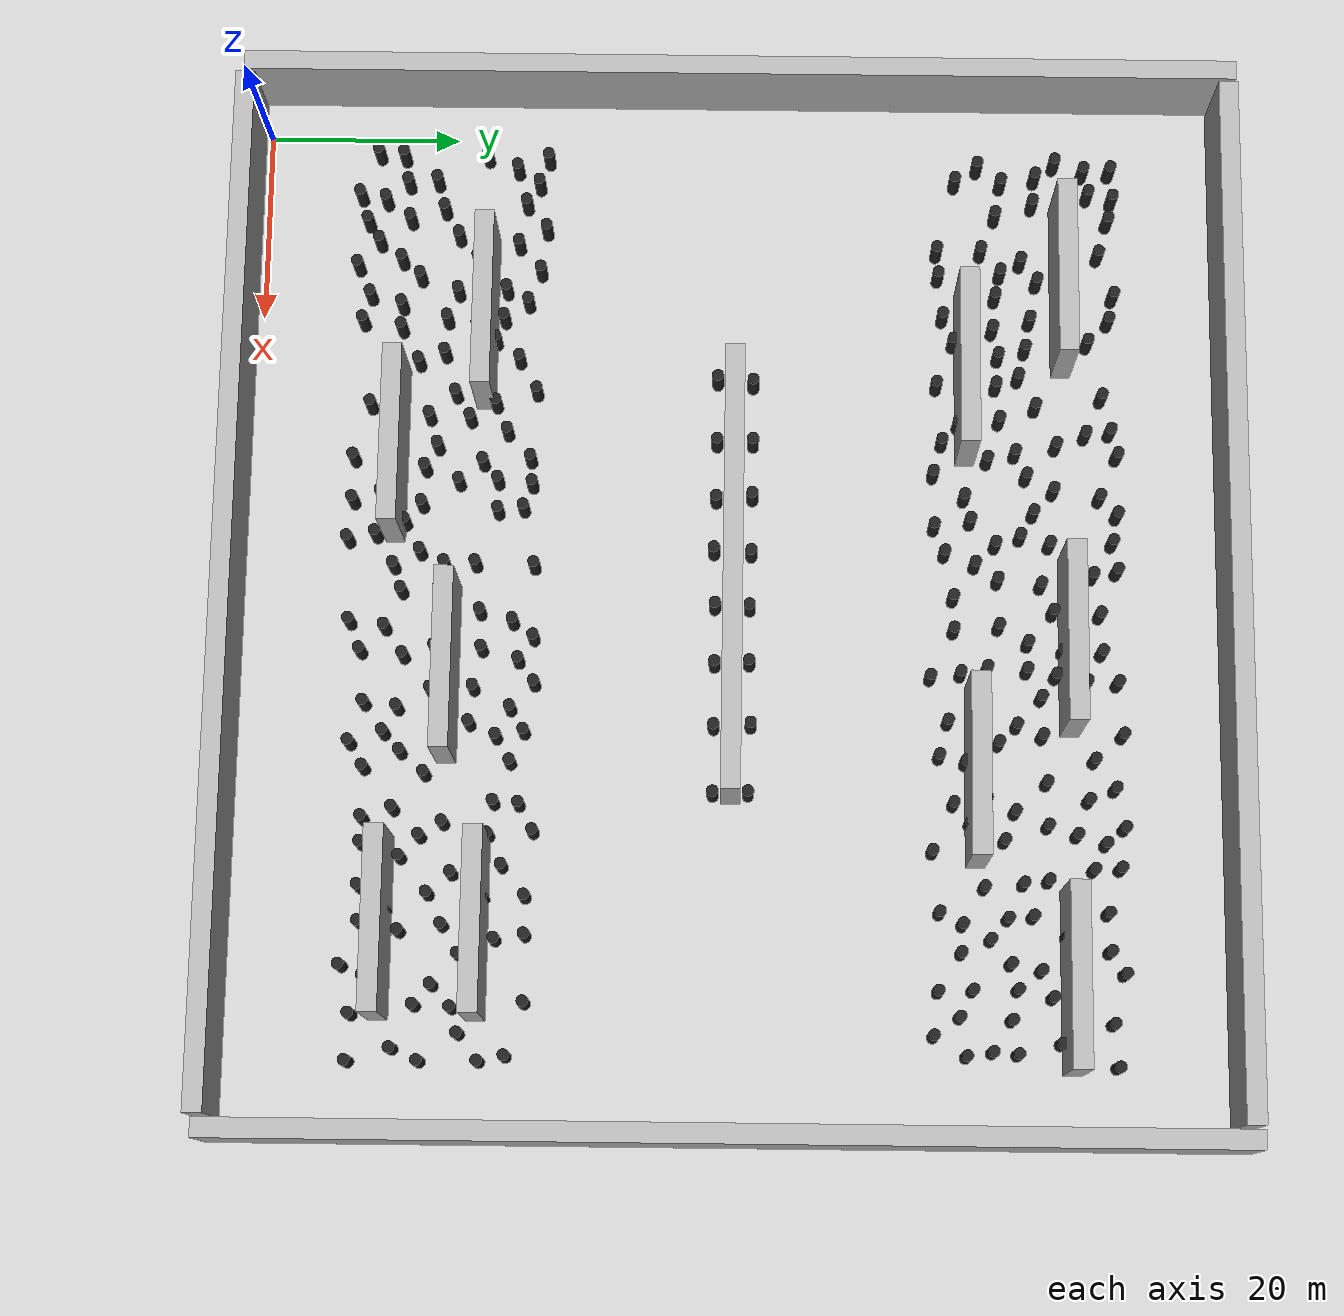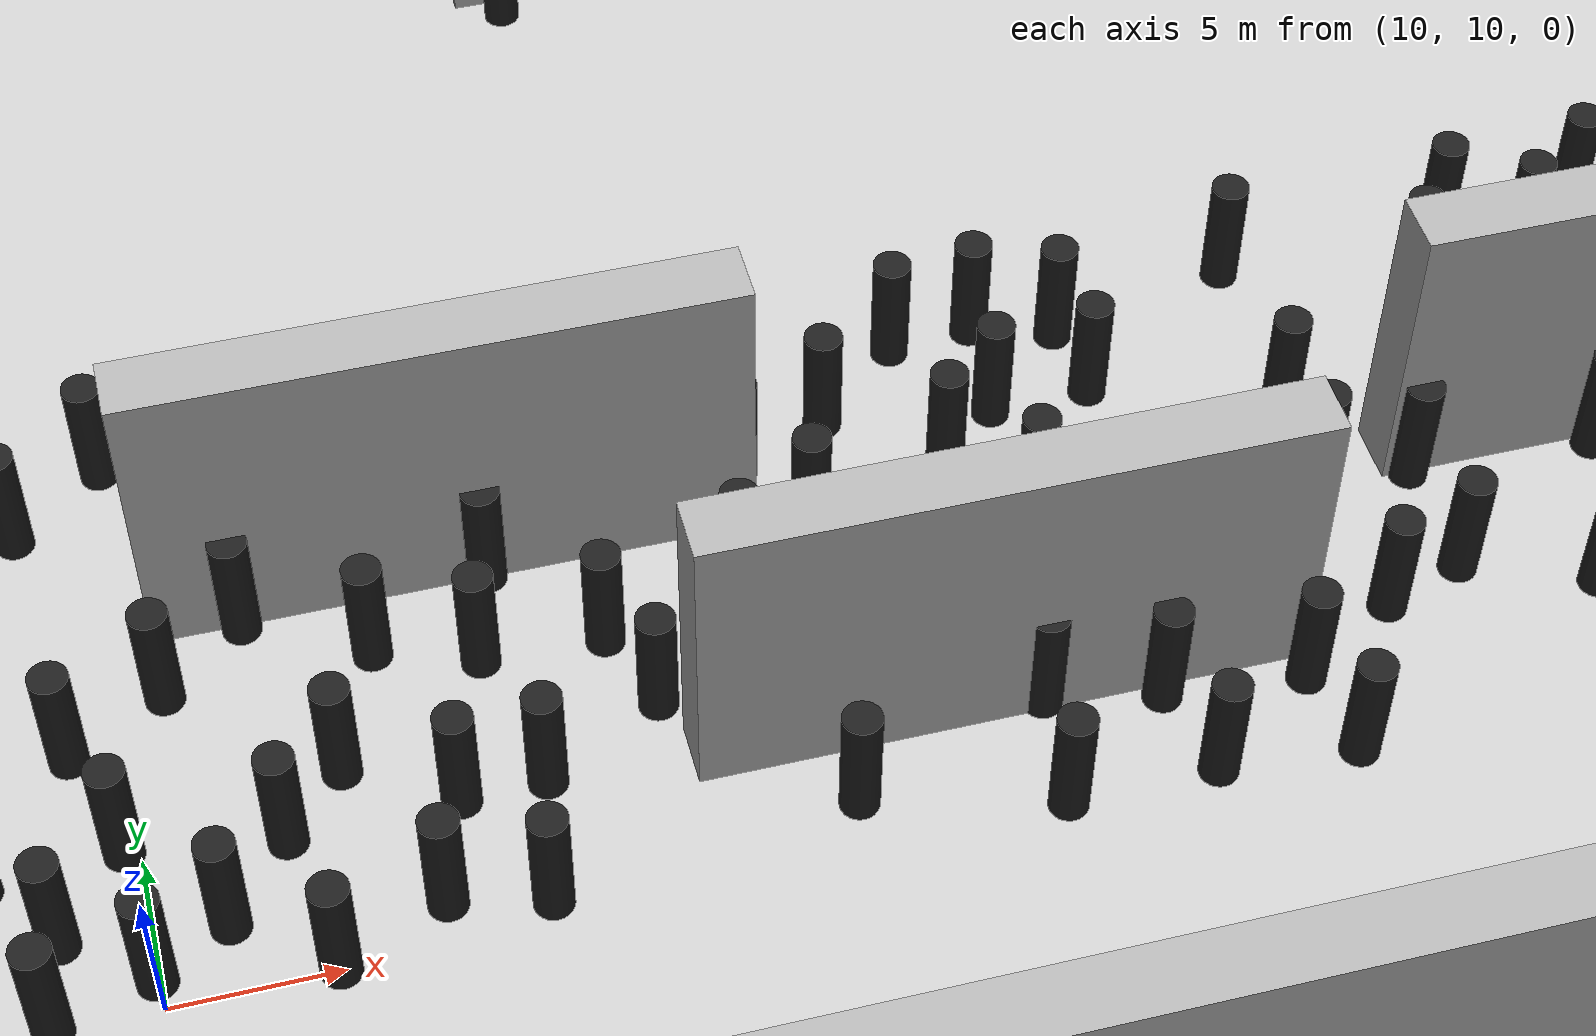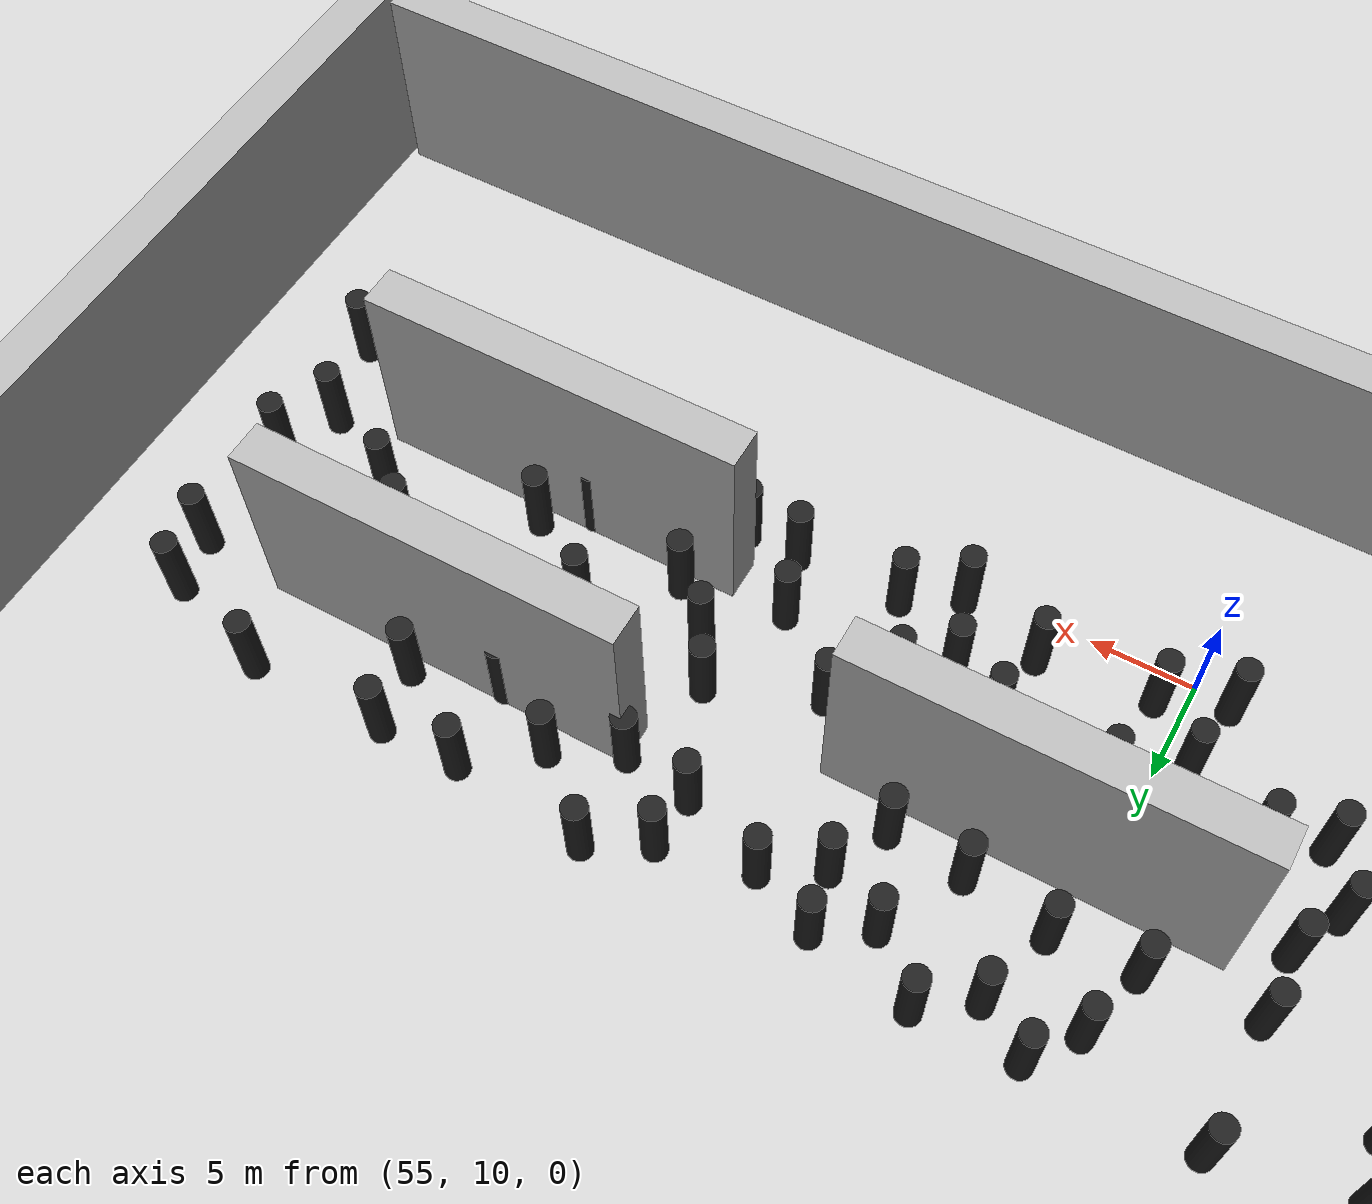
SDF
<sdf version="1.7">
 <world name="default">
  <light name="sun" type="directional">
   <cast_shadows>0</cast_shadows>
   <pose>0 0 10 0 -0 0</pose>
   <diffuse>0.8 0.8 0.8 1</diffuse>
   <specular>0.2 0.2 0.2 1</specular>
   <attenuation>
    <range>1000</range>
    <constant>0.9</constant>
    <linear>0.01</linear>
    <quadratic>0.001</quadratic>
   </attenuation>
   <direction>-0.5 0.1 -0.9</direction>
   <spot><inner_angle>0</inner_angle><outer_angle>0</outer_angle><falloff>0</falloff></spot>
  </light>
  <model name="ground_plane">
   <pose>20 20 0 0 -0 0</pose>
   <static>1</static>
   <link name="link">
    <collision name="collision">
     <geometry><plane><normal>0 0 1</normal><size>200 200</size></plane></geometry>
     <surface><friction><ode><mu>100</mu><mu2>50</mu2></ode></friction></surface>
    </collision>
    <visual name="visual">
     <cast_shadows>0</cast_shadows>
     <geometry><plane><normal>0 0 1</normal><size>200 200</size></plane></geometry>
     <material>
      <script><uri>file://media/materials/scripts/gazebo.material</uri><name>Gazebo/Grey</name></script>
     </material>
    </visual>
   </link>
  </model>
  <physics name="default_physics" default="0" type="ode">
   <max_step_size>0.001</max_step_size>
   <real_time_factor>1</real_time_factor>
   <real_time_update_rate>1000</real_time_update_rate>
  </physics>
  <scene><ambient>0.4 0.4 0.4 1</ambient><background>0.7 0.7 0.7 1</background><shadows>0</shadows></scene>
  <spherical_coordinates>
   <surface_model>EARTH_WGS84</surface_model>
   <latitude_deg>0</latitude_deg>
   <longitude_deg>0</longitude_deg>
   <elevation>0</elevation>
   <heading_deg>0</heading_deg>
  </spherical_coordinates>
  <model name="pillar_bottom_area_0">
   <static>1</static>
   <pose>47.0649 20.12 0 0 -0 0</pose>
   <link name="link">
    <pose>0 0 2 0 -0 0</pose>
    <inertial>
     <mass>1</mass>
     <inertia><ixx>0.083</ixx><ixy>0</ixy><ixz>0</ixz><iyy>0.083</iyy><iyz>0</iyz><izz>0.083</izz></inertia>
    </inertial>
    <collision name="collision">
     <geometry><cylinder><radius>0.6</radius><length>4</length></cylinder></geometry>
    </collision>
    <visual name="visual">
     <geometry><cylinder><radius>0.6</radius><length>4</length></cylinder></geometry>
     <material>
      <script><uri>file://media/materials/scripts/gazebo.material</uri><name>Gazebo/Black</name></script>
     </material>
    </visual>
   </link>
  </model>
  <model name="pillar_bottom_area_1">
   <static>1</static>
   <pose>84.1416 12.7099 0 0 -0 0</pose>
   <link name="link">
    <pose>0 0 2 0 -0 0</pose>
    <inertial>
     <mass>1</mass>
     <inertia><ixx>0.083</ixx><ixy>0</ixy><ixz>0</ixz><iyy>0.083</iyy><iyz>0</iyz><izz>0.083</izz></inertia>
    </inertial>
    <collision name="collision">
     <geometry><cylinder><radius>0.6</radius><length>4</length></cylinder></geometry>
    </collision>
    <visual name="visual">
     <geometry><cylinder><radius>0.6</radius><length>4</length></cylinder></geometry>
     <material>
      <script><uri>file://media/materials/scripts/gazebo.material</uri><name>Gazebo/Black</name></script>
     </material>
    </visual>
   </link>
  </model>
  <model name="pillar_bottom_area_2">
   <static>1</static>
   <pose>72.5903 15.6556 0 0 -0 0</pose>
   <link name="link">
    <pose>0 0 2 0 -0 0</pose>
    <inertial>
     <mass>1</mass>
     <inertia><ixx>0.083</ixx><ixy>0</ixy><ixz>0</ixz><iyy>0.083</iyy><iyz>0</iyz><izz>0.083</izz></inertia>
    </inertial>
    <collision name="collision">
     <geometry><cylinder><radius>0.6</radius><length>4</length></cylinder></geometry>
    </collision>
    <visual name="visual">
     <geometry><cylinder><radius>0.6</radius><length>4</length></cylinder></geometry>
     <material>
      <script><uri>file://media/materials/scripts/gazebo.material</uri><name>Gazebo/Black</name></script>
     </material>
    </visual>
   </link>
  </model>
  <model name="pillar_bottom_area_3">
   <static>1</static>
   <pose>5.53631 15.0345 0 0 -0 0</pose>
   <link name="link">
    <pose>0 0 2 0 -0 0</pose>
    <inertial>
     <mass>1</mass>
     <inertia><ixx>0.083</ixx><ixy>0</ixy><ixz>0</ixz><iyy>0.083</iyy><iyz>0</iyz><izz>0.083</izz></inertia>
    </inertial>
    <collision name="collision">
     <geometry><cylinder><radius>0.6</radius><length>4</length></cylinder></geometry>
    </collision>
    <visual name="visual">
     <geometry><cylinder><radius>0.6</radius><length>4</length></cylinder></geometry>
     <material>
      <script><uri>file://media/materials/scripts/gazebo.material</uri><name>Gazebo/Black</name></script>
     </material>
    </visual>
   </link>
  </model>
  <model name="pillar_bottom_area_4">
   <static>1</static>
   <pose>57.1494 27.9983 0 0 -0 0</pose>
   <link name="link">
    <pose>0 0 2 0 -0 0</pose>
    <inertial>
     <mass>1</mass>
     <inertia><ixx>0.083</ixx><ixy>0</ixy><ixz>0</ixz><iyy>0.083</iyy><iyz>0</iyz><izz>0.083</izz></inertia>
    </inertial>
    <collision name="collision">
     <geometry><cylinder><radius>0.6</radius><length>4</length></cylinder></geometry>
    </collision>
    <visual name="visual">
     <geometry><cylinder><radius>0.6</radius><length>4</length></cylinder></geometry>
     <material>
      <script><uri>file://media/materials/scripts/gazebo.material</uri><name>Gazebo/Black</name></script>
     </material>
    </visual>
   </link>
  </model>
  <model name="pillar_bottom_area_5">
   <static>1</static>
   <pose>67.7017 27.4225 0 0 -0 0</pose>
   <link name="link">
    <pose>0 0 2 0 -0 0</pose>
    <inertial>
     <mass>1</mass>
     <inertia><ixx>0.083</ixx><ixy>0</ixy><ixz>0</ixz><iyy>0.083</iyy><iyz>0</iyz><izz>0.083</izz></inertia>
    </inertial>
    <collision name="collision">
     <geometry><cylinder><radius>0.6</radius><length>4</length></cylinder></geometry>
    </collision>
    <visual name="visual">
     <geometry><cylinder><radius>0.6</radius><length>4</length></cylinder></geometry>
     <material>
      <script><uri>file://media/materials/scripts/gazebo.material</uri><name>Gazebo/Black</name></script>
     </material>
    </visual>
   </link>
  </model>
  <model name="pillar_bottom_area_6">
   <static>1</static>
   <pose>76.1727 12.587 0 0 -0 0</pose>
   <link name="link">
    <pose>0 0 2 0 -0 0</pose>
    <inertial>
     <mass>1</mass>
     <inertia><ixx>0.083</ixx><ixy>0</ixy><ixz>0</ixz><iyy>0.083</iyy><iyz>0</iyz><izz>0.083</izz></inertia>
    </inertial>
    <collision name="collision">
     <geometry><cylinder><radius>0.6</radius><length>4</length></cylinder></geometry>
    </collision>
    <visual name="visual">
     <geometry><cylinder><radius>0.6</radius><length>4</length></cylinder></geometry>
     <material>
      <script><uri>file://media/materials/scripts/gazebo.material</uri><name>Gazebo/Black</name></script>
     </material>
    </visual>
   </link>
  </model>
  <model name="pillar_bottom_area_7">
   <static>1</static>
   <pose>12.1079 12.192 0 0 -0 0</pose>
   <link name="link">
    <pose>0 0 2 0 -0 0</pose>
    <inertial>
     <mass>1</mass>
     <inertia><ixx>0.083</ixx><ixy>0</ixy><ixz>0</ixz><iyy>0.083</iyy><iyz>0</iyz><izz>0.083</izz></inertia>
    </inertial>
    <collision name="collision">
     <geometry><cylinder><radius>0.6</radius><length>4</length></cylinder></geometry>
    </collision>
    <visual name="visual">
     <geometry><cylinder><radius>0.6</radius><length>4</length></cylinder></geometry>
     <material>
      <script><uri>file://media/materials/scripts/gazebo.material</uri><name>Gazebo/Black</name></script>
     </material>
    </visual>
   </link>
  </model>
  <model name="pillar_bottom_area_8">
   <static>1</static>
   <pose>59.5444 29.6801 0 0 -0 0</pose>
   <link name="link">
    <pose>0 0 2 0 -0 0</pose>
    <inertial>
     <mass>1</mass>
     <inertia><ixx>0.083</ixx><ixy>0</ixy><ixz>0</ixz><iyy>0.083</iyy><iyz>0</iyz><izz>0.083</izz></inertia>
    </inertial>
    <collision name="collision">
     <geometry><cylinder><radius>0.6</radius><length>4</length></cylinder></geometry>
    </collision>
    <visual name="visual">
     <geometry><cylinder><radius>0.6</radius><length>4</length></cylinder></geometry>
     <material>
      <script><uri>file://media/materials/scripts/gazebo.material</uri><name>Gazebo/Black</name></script>
     </material>
    </visual>
   </link>
  </model>
  <model name="pillar_bottom_area_9">
   <static>1</static>
   <pose>7.45141 12.7149 0 0 -0 0</pose>
   <link name="link">
    <pose>0 0 2 0 -0 0</pose>
    <inertial>
     <mass>1</mass>
     <inertia><ixx>0.083</ixx><ixy>0</ixy><ixz>0</ixz><iyy>0.083</iyy><iyz>0</iyz><izz>0.083</izz></inertia>
    </inertial>
    <collision name="collision">
     <geometry><cylinder><radius>0.6</radius><length>4</length></cylinder></geometry>
    </collision>
    <visual name="visual">
     <geometry><cylinder><radius>0.6</radius><length>4</length></cylinder></geometry>
     <material>
      <script><uri>file://media/materials/scripts/gazebo.material</uri><name>Gazebo/Black</name></script>
     </material>
    </visual>
   </link>
  </model>
  <model name="pillar_bottom_area_10">
   <static>1</static>
   <pose>13.9722 22.6188 0 0 -0 0</pose>
   <link name="link">
    <pose>0 0 2 0 -0 0</pose>
    <inertial>
     <mass>1</mass>
     <inertia><ixx>0.083</ixx><ixy>0</ixy><ixz>0</ixz><iyy>0.083</iyy><iyz>0</iyz><izz>0.083</izz></inertia>
    </inertial>
    <collision name="collision">
     <geometry><cylinder><radius>0.6</radius><length>4</length></cylinder></geometry>
    </collision>
    <visual name="visual">
     <geometry><cylinder><radius>0.6</radius><length>4</length></cylinder></geometry>
     <material>
      <script><uri>file://media/materials/scripts/gazebo.material</uri><name>Gazebo/Black</name></script>
     </material>
    </visual>
   </link>
  </model>
  <model name="pillar_bottom_area_11">
   <static>1</static>
   <pose>53.8203 14.1874 0 0 -0 0</pose>
   <link name="link">
    <pose>0 0 2 0 -0 0</pose>
    <inertial>
     <mass>1</mass>
     <inertia><ixx>0.083</ixx><ixy>0</ixy><ixz>0</ixz><iyy>0.083</iyy><iyz>0</iyz><izz>0.083</izz></inertia>
    </inertial>
    <collision name="collision">
     <geometry><cylinder><radius>0.6</radius><length>4</length></cylinder></geometry>
    </collision>
    <visual name="visual">
     <geometry><cylinder><radius>0.6</radius><length>4</length></cylinder></geometry>
     <material>
      <script><uri>file://media/materials/scripts/gazebo.material</uri><name>Gazebo/Black</name></script>
     </material>
    </visual>
   </link>
  </model>
  <model name="pillar_bottom_area_12">
   <static>1</static>
   <pose>62.1408 27.3001 0 0 -0 0</pose>
   <link name="link">
    <pose>0 0 2 0 -0 0</pose>
    <inertial>
     <mass>1</mass>
     <inertia><ixx>0.083</ixx><ixy>0</ixy><ixz>0</ixz><iyy>0.083</iyy><iyz>0</iyz><izz>0.083</izz></inertia>
    </inertial>
    <collision name="collision">
     <geometry><cylinder><radius>0.6</radius><length>4</length></cylinder></geometry>
    </collision>
    <visual name="visual">
     <geometry><cylinder><radius>0.6</radius><length>4</length></cylinder></geometry>
     <material>
      <script><uri>file://media/materials/scripts/gazebo.material</uri><name>Gazebo/Black</name></script>
     </material>
    </visual>
   </link>
  </model>
  <model name="pillar_bottom_area_13">
   <static>1</static>
   <pose>65.0875 25.9205 0 0 -0 0</pose>
   <link name="link">
    <pose>0 0 2 0 -0 0</pose>
    <inertial>
     <mass>1</mass>
     <inertia><ixx>0.083</ixx><ixy>0</ixy><ixz>0</ixz><iyy>0.083</iyy><iyz>0</iyz><izz>0.083</izz></inertia>
    </inertial>
    <collision name="collision">
     <geometry><cylinder><radius>0.6</radius><length>4</length></cylinder></geometry>
    </collision>
    <visual name="visual">
     <geometry><cylinder><radius>0.6</radius><length>4</length></cylinder></geometry>
     <material>
      <script><uri>file://media/materials/scripts/gazebo.material</uri><name>Gazebo/Black</name></script>
     </material>
    </visual>
   </link>
  </model>
  <model name="pillar_bottom_area_14">
   <static>1</static>
   <pose>41.0472 28.1275 0 0 -0 0</pose>
   <link name="link">
    <pose>0 0 2 0 -0 0</pose>
    <inertial>
     <mass>1</mass>
     <inertia><ixx>0.083</ixx><ixy>0</ixy><ixz>0</ixz><iyy>0.083</iyy><iyz>0</iyz><izz>0.083</izz></inertia>
    </inertial>
    <collision name="collision">
     <geometry><cylinder><radius>0.6</radius><length>4</length></cylinder></geometry>
    </collision>
    <visual name="visual">
     <geometry><cylinder><radius>0.6</radius><length>4</length></cylinder></geometry>
     <material>
      <script><uri>file://media/materials/scripts/gazebo.material</uri><name>Gazebo/Black</name></script>
     </material>
    </visual>
   </link>
  </model>
  <model name="pillar_bottom_area_15">
   <static>1</static>
   <pose>56.7745 16.1801 0 0 -0 0</pose>
   <link name="link">
    <pose>0 0 2 0 -0 0</pose>
    <inertial>
     <mass>1</mass>
     <inertia><ixx>0.083</ixx><ixy>0</ixy><ixz>0</ixz><iyy>0.083</iyy><iyz>0</iyz><izz>0.083</izz></inertia>
    </inertial>
    <collision name="collision">
     <geometry><cylinder><radius>0.6</radius><length>4</length></cylinder></geometry>
    </collision>
    <visual name="visual">
     <geometry><cylinder><radius>0.6</radius><length>4</length></cylinder></geometry>
     <material>
      <script><uri>file://media/materials/scripts/gazebo.material</uri><name>Gazebo/Black</name></script>
     </material>
    </visual>
   </link>
  </model>
  <model name="pillar_bottom_area_16">
   <static>1</static>
   <pose>60.0538 23.4727 0 0 -0 0</pose>
   <link name="link">
    <pose>0 0 2 0 -0 0</pose>
    <inertial>
     <mass>1</mass>
     <inertia><ixx>0.083</ixx><ixy>0</ixy><ixz>0</ixz><iyy>0.083</iyy><iyz>0</iyz><izz>0.083</izz></inertia>
    </inertial>
    <collision name="collision">
     <geometry><cylinder><radius>0.6</radius><length>4</length></cylinder></geometry>
    </collision>
    <visual name="visual">
     <geometry><cylinder><radius>0.6</radius><length>4</length></cylinder></geometry>
     <material>
      <script><uri>file://media/materials/scripts/gazebo.material</uri><name>Gazebo/Black</name></script>
     </material>
    </visual>
   </link>
  </model>
  <model name="pillar_bottom_area_17">
   <static>1</static>
   <pose>36.8303 17.8064 0 0 -0 0</pose>
   <link name="link">
    <pose>0 0 2 0 -0 0</pose>
    <inertial>
     <mass>1</mass>
     <inertia><ixx>0.083</ixx><ixy>0</ixy><ixz>0</ixz><iyy>0.083</iyy><iyz>0</iyz><izz>0.083</izz></inertia>
    </inertial>
    <collision name="collision">
     <geometry><cylinder><radius>0.6</radius><length>4</length></cylinder></geometry>
    </collision>
    <visual name="visual">
     <geometry><cylinder><radius>0.6</radius><length>4</length></cylinder></geometry>
     <material>
      <script><uri>file://media/materials/scripts/gazebo.material</uri><name>Gazebo/Black</name></script>
     </material>
    </visual>
   </link>
  </model>
  <model name="pillar_bottom_area_18">
   <static>1</static>
   <pose>97.912 19.0956 0 0 -0 0</pose>
   <link name="link">
    <pose>0 0 2 0 -0 0</pose>
    <inertial>
     <mass>1</mass>
     <inertia><ixx>0.083</ixx><ixy>0</ixy><ixz>0</ixz><iyy>0.083</iyy><iyz>0</iyz><izz>0.083</izz></inertia>
    </inertial>
    <collision name="collision">
     <geometry><cylinder><radius>0.6</radius><length>4</length></cylinder></geometry>
    </collision>
    <visual name="visual">
     <geometry><cylinder><radius>0.6</radius><length>4</length></cylinder></geometry>
     <material>
      <script><uri>file://media/materials/scripts/gazebo.material</uri><name>Gazebo/Black</name></script>
     </material>
    </visual>
   </link>
  </model>
  <model name="pillar_bottom_area_19">
   <static>1</static>
   <pose>74.7778 29.9178 0 0 -0 0</pose>
   <link name="link">
    <pose>0 0 2 0 -0 0</pose>
    <inertial>
     <mass>1</mass>
     <inertia><ixx>0.083</ixx><ixy>0</ixy><ixz>0</ixz><iyy>0.083</iyy><iyz>0</iyz><izz>0.083</izz></inertia>
    </inertial>
    <collision name="collision">
     <geometry><cylinder><radius>0.6</radius><length>4</length></cylinder></geometry>
    </collision>
    <visual name="visual">
     <geometry><cylinder><radius>0.6</radius><length>4</length></cylinder></geometry>
     <material>
      <script><uri>file://media/materials/scripts/gazebo.material</uri><name>Gazebo/Black</name></script>
     </material>
    </visual>
   </link>
  </model>
  <model name="pillar_bottom_area_20">
   <static>1</static>
   <pose>32.8553 26.2557 0 0 -0 0</pose>
   <link name="link">
    <pose>0 0 2 0 -0 0</pose>
    <inertial>
     <mass>1</mass>
     <inertia><ixx>0.083</ixx><ixy>0</ixy><ixz>0</ixz><iyy>0.083</iyy><iyz>0</iyz><izz>0.083</izz></inertia>
    </inertial>
    <collision name="collision">
     <geometry><cylinder><radius>0.6</radius><length>4</length></cylinder></geometry>
    </collision>
    <visual name="visual">
     <geometry><cylinder><radius>0.6</radius><length>4</length></cylinder></geometry>
     <material>
      <script><uri>file://media/materials/scripts/gazebo.material</uri><name>Gazebo/Black</name></script>
     </material>
    </visual>
   </link>
  </model>
  <model name="pillar_bottom_area_21">
   <static>1</static>
   <pose>14.8298 10.0086 0 0 -0 0</pose>
   <link name="link">
    <pose>0 0 2 0 -0 0</pose>
    <inertial>
     <mass>1</mass>
     <inertia><ixx>0.083</ixx><ixy>0</ixy><ixz>0</ixz><iyy>0.083</iyy><iyz>0</iyz><izz>0.083</izz></inertia>
    </inertial>
    <collision name="collision">
     <geometry><cylinder><radius>0.6</radius><length>4</length></cylinder></geometry>
    </collision>
    <visual name="visual">
     <geometry><cylinder><radius>0.6</radius><length>4</length></cylinder></geometry>
     <material>
      <script><uri>file://media/materials/scripts/gazebo.material</uri><name>Gazebo/Black</name></script>
     </material>
    </visual>
   </link>
  </model>
  <model name="pillar_bottom_area_22">
   <static>1</static>
   <pose>54.7502 29.4957 0 0 -0 0</pose>
   <link name="link">
    <pose>0 0 2 0 -0 0</pose>
    <inertial>
     <mass>1</mass>
     <inertia><ixx>0.083</ixx><ixy>0</ixy><ixz>0</ixz><iyy>0.083</iyy><iyz>0</iyz><izz>0.083</izz></inertia>
    </inertial>
    <collision name="collision">
     <geometry><cylinder><radius>0.6</radius><length>4</length></cylinder></geometry>
    </collision>
    <visual name="visual">
     <geometry><cylinder><radius>0.6</radius><length>4</length></cylinder></geometry>
     <material>
      <script><uri>file://media/materials/scripts/gazebo.material</uri><name>Gazebo/Black</name></script>
     </material>
    </visual>
   </link>
  </model>
  <model name="pillar_bottom_area_23">
   <static>1</static>
   <pose>3.854 26.5912 0 0 -0 0</pose>
   <link name="link">
    <pose>0 0 2 0 -0 0</pose>
    <inertial>
     <mass>1</mass>
     <inertia><ixx>0.083</ixx><ixy>0</ixy><ixz>0</ixz><iyy>0.083</iyy><iyz>0</iyz><izz>0.083</izz></inertia>
    </inertial>
    <collision name="collision">
     <geometry><cylinder><radius>0.6</radius><length>4</length></cylinder></geometry>
    </collision>
    <visual name="visual">
     <geometry><cylinder><radius>0.6</radius><length>4</length></cylinder></geometry>
     <material>
      <script><uri>file://media/materials/scripts/gazebo.material</uri><name>Gazebo/Black</name></script>
     </material>
    </visual>
   </link>
  </model>
  <model name="pillar_bottom_area_24">
   <static>1</static>
   <pose>42.6407 15.8855 0 0 -0 0</pose>
   <link name="link">
    <pose>0 0 2 0 -0 0</pose>
    <inertial>
     <mass>1</mass>
     <inertia><ixx>0.083</ixx><ixy>0</ixy><ixz>0</ixz><iyy>0.083</iyy><iyz>0</iyz><izz>0.083</izz></inertia>
    </inertial>
    <collision name="collision">
     <geometry><cylinder><radius>0.6</radius><length>4</length></cylinder></geometry>
    </collision>
    <visual name="visual">
     <geometry><cylinder><radius>0.6</radius><length>4</length></cylinder></geometry>
     <material>
      <script><uri>file://media/materials/scripts/gazebo.material</uri><name>Gazebo/Black</name></script>
     </material>
    </visual>
   </link>
  </model>
  <model name="pillar_bottom_area_25">
   <static>1</static>
   <pose>74.004 20.7848 0 0 -0 0</pose>
   <link name="link">
    <pose>0 0 2 0 -0 0</pose>
    <inertial>
     <mass>1</mass>
     <inertia><ixx>0.083</ixx><ixy>0</ixy><ixz>0</ixz><iyy>0.083</iyy><iyz>0</iyz><izz>0.083</izz></inertia>
    </inertial>
    <collision name="collision">
     <geometry><cylinder><radius>0.6</radius><length>4</length></cylinder></geometry>
    </collision>
    <visual name="visual">
     <geometry><cylinder><radius>0.6</radius><length>4</length></cylinder></geometry>
     <material>
      <script><uri>file://media/materials/scripts/gazebo.material</uri><name>Gazebo/Black</name></script>
     </material>
    </visual>
   </link>
  </model>
  <model name="pillar_bottom_area_26">
   <static>1</static>
   <pose>12.2931 26.9373 0 0 -0 0</pose>
   <link name="link">
    <pose>0 0 2 0 -0 0</pose>
    <inertial>
     <mass>1</mass>
     <inertia><ixx>0.083</ixx><ixy>0</ixy><ixz>0</ixz><iyy>0.083</iyy><iyz>0</iyz><izz>0.083</izz></inertia>
    </inertial>
    <collision name="collision">
     <geometry><cylinder><radius>0.6</radius><length>4</length></cylinder></geometry>
    </collision>
    <visual name="visual">
     <geometry><cylinder><radius>0.6</radius><length>4</length></cylinder></geometry>
     <material>
      <script><uri>file://media/materials/scripts/gazebo.material</uri><name>Gazebo/Black</name></script>
     </material>
    </visual>
   </link>
  </model>
  <model name="pillar_bottom_area_27">
   <static>1</static>
   <pose>49.9434 15.7807 0 0 -0 0</pose>
   <link name="link">
    <pose>0 0 2 0 -0 0</pose>
    <inertial>
     <mass>1</mass>
     <inertia><ixx>0.083</ixx><ixy>0</ixy><ixz>0</ixz><iyy>0.083</iyy><iyz>0</iyz><izz>0.083</izz></inertia>
    </inertial>
    <collision name="collision">
     <geometry><cylinder><radius>0.6</radius><length>4</length></cylinder></geometry>
    </collision>
    <visual name="visual">
     <geometry><cylinder><radius>0.6</radius><length>4</length></cylinder></geometry>
     <material>
      <script><uri>file://media/materials/scripts/gazebo.material</uri><name>Gazebo/Black</name></script>
     </material>
    </visual>
   </link>
  </model>
  <model name="pillar_bottom_area_28">
   <static>1</static>
   <pose>61.7428 12.3351 0 0 -0 0</pose>
   <link name="link">
    <pose>0 0 2 0 -0 0</pose>
    <inertial>
     <mass>1</mass>
     <inertia><ixx>0.083</ixx><ixy>0</ixy><ixz>0</ixz><iyy>0.083</iyy><iyz>0</iyz><izz>0.083</izz></inertia>
    </inertial>
    <collision name="collision">
     <geometry><cylinder><radius>0.6</radius><length>4</length></cylinder></geometry>
    </collision>
    <visual name="visual">
     <geometry><cylinder><radius>0.6</radius><length>4</length></cylinder></geometry>
     <material>
      <script><uri>file://media/materials/scripts/gazebo.material</uri><name>Gazebo/Black</name></script>
     </material>
    </visual>
   </link>
  </model>
  <model name="pillar_bottom_area_30">
   <static>1</static>
   <pose>80.5026 12.5165 0 0 -0 0</pose>
   <link name="link">
    <pose>0 0 2 0 -0 0</pose>
    <inertial>
     <mass>1</mass>
     <inertia><ixx>0.083</ixx><ixy>0</ixy><ixz>0</ixz><iyy>0.083</iyy><iyz>0</iyz><izz>0.083</izz></inertia>
    </inertial>
    <collision name="collision">
     <geometry><cylinder><radius>0.6</radius><length>4</length></cylinder></geometry>
    </collision>
    <visual name="visual">
     <geometry><cylinder><radius>0.6</radius><length>4</length></cylinder></geometry>
     <material>
      <script><uri>file://media/materials/scripts/gazebo.material</uri><name>Gazebo/Black</name></script>
     </material>
    </visual>
   </link>
  </model>
  <model name="pillar_bottom_area_31">
   <static>1</static>
   <pose>31.2459 18.0879 0 0 -0 0</pose>
   <link name="link">
    <pose>0 0 2 0 -0 0</pose>
    <inertial>
     <mass>1</mass>
     <inertia><ixx>0.083</ixx><ixy>0</ixy><ixz>0</ixz><iyy>0.083</iyy><iyz>0</iyz><izz>0.083</izz></inertia>
    </inertial>
    <collision name="collision">
     <geometry><cylinder><radius>0.6</radius><length>4</length></cylinder></geometry>
    </collision>
    <visual name="visual">
     <geometry><cylinder><radius>0.6</radius><length>4</length></cylinder></geometry>
     <material>
      <script><uri>file://media/materials/scripts/gazebo.material</uri><name>Gazebo/Black</name></script>
     </material>
    </visual>
   </link>
  </model>
  <model name="pillar_bottom_area_33">
   <static>1</static>
   <pose>36.1515 23.7987 0 0 -0 0</pose>
   <link name="link">
    <pose>0 0 2 0 -0 0</pose>
    <inertial>
     <mass>1</mass>
     <inertia><ixx>0.083</ixx><ixy>0</ixy><ixz>0</ixz><iyy>0.083</iyy><iyz>0</iyz><izz>0.083</izz></inertia>
    </inertial>
    <collision name="collision">
     <geometry><cylinder><radius>0.6</radius><length>4</length></cylinder></geometry>
    </collision>
    <visual name="visual">
     <geometry><cylinder><radius>0.6</radius><length>4</length></cylinder></geometry>
     <material>
      <script><uri>file://media/materials/scripts/gazebo.material</uri><name>Gazebo/Black</name></script>
     </material>
    </visual>
   </link>
  </model>
  <model name="pillar_bottom_area_34">
   <static>1</static>
   <pose>9.89757 10.8948 0 0 -0 0</pose>
   <link name="link">
    <pose>0 0 2 0 -0 0</pose>
    <inertial>
     <mass>1</mass>
     <inertia><ixx>0.083</ixx><ixy>0</ixy><ixz>0</ixz><iyy>0.083</iyy><iyz>0</iyz><izz>0.083</izz></inertia>
    </inertial>
    <collision name="collision">
     <geometry><cylinder><radius>0.6</radius><length>4</length></cylinder></geometry>
    </collision>
    <visual name="visual">
     <geometry><cylinder><radius>0.6</radius><length>4</length></cylinder></geometry>
     <material>
      <script><uri>file://media/materials/scripts/gazebo.material</uri><name>Gazebo/Black</name></script>
     </material>
    </visual>
   </link>
  </model>
  <model name="pillar_bottom_area_36">
   <static>1</static>
   <pose>28.8002 20.7438 0 0 -0 0</pose>
   <link name="link">
    <pose>0 0 2 0 -0 0</pose>
    <inertial>
     <mass>1</mass>
     <inertia><ixx>0.083</ixx><ixy>0</ixy><ixz>0</ixz><iyy>0.083</iyy><iyz>0</iyz><izz>0.083</izz></inertia>
    </inertial>
    <collision name="collision">
     <geometry><cylinder><radius>0.6</radius><length>4</length></cylinder></geometry>
    </collision>
    <visual name="visual">
     <geometry><cylinder><radius>0.6</radius><length>4</length></cylinder></geometry>
     <material>
      <script><uri>file://media/materials/scripts/gazebo.material</uri><name>Gazebo/Black</name></script>
     </material>
    </visual>
   </link>
  </model>
  <model name="pillar_bottom_area_37">
   <static>1</static>
   <pose>78.3142 26.8641 0 0 -0 0</pose>
   <link name="link">
    <pose>0 0 2 0 -0 0</pose>
    <inertial>
     <mass>1</mass>
     <inertia><ixx>0.083</ixx><ixy>0</ixy><ixz>0</ixz><iyy>0.083</iyy><iyz>0</iyz><izz>0.083</izz></inertia>
    </inertial>
    <collision name="collision">
     <geometry><cylinder><radius>0.6</radius><length>4</length></cylinder></geometry>
    </collision>
    <visual name="visual">
     <geometry><cylinder><radius>0.6</radius><length>4</length></cylinder></geometry>
     <material>
      <script><uri>file://media/materials/scripts/gazebo.material</uri><name>Gazebo/Black</name></script>
     </material>
    </visual>
   </link>
  </model>
  <model name="pillar_bottom_area_38">
   <static>1</static>
   <pose>24.9449 27.302 0 0 -0 0</pose>
   <link name="link">
    <pose>0 0 2 0 -0 0</pose>
    <inertial>
     <mass>1</mass>
     <inertia><ixx>0.083</ixx><ixy>0</ixy><ixz>0</ixz><iyy>0.083</iyy><iyz>0</iyz><izz>0.083</izz></inertia>
    </inertial>
    <collision name="collision">
     <geometry><cylinder><radius>0.6</radius><length>4</length></cylinder></geometry>
    </collision>
    <visual name="visual">
     <geometry><cylinder><radius>0.6</radius><length>4</length></cylinder></geometry>
     <material>
      <script><uri>file://media/materials/scripts/gazebo.material</uri><name>Gazebo/Black</name></script>
     </material>
    </visual>
   </link>
  </model>
  <model name="pillar_bottom_area_39">
   <static>1</static>
   <pose>90.3237 20.1662 0 0 -0 0</pose>
   <link name="link">
    <pose>0 0 2 0 -0 0</pose>
    <inertial>
     <mass>1</mass>
     <inertia><ixx>0.083</ixx><ixy>0</ixy><ixz>0</ixz><iyy>0.083</iyy><iyz>0</iyz><izz>0.083</izz></inertia>
    </inertial>
    <collision name="collision">
     <geometry><cylinder><radius>0.6</radius><length>4</length></cylinder></geometry>
    </collision>
    <visual name="visual">
     <geometry><cylinder><radius>0.6</radius><length>4</length></cylinder></geometry>
     <material>
      <script><uri>file://media/materials/scripts/gazebo.material</uri><name>Gazebo/Black</name></script>
     </material>
    </visual>
   </link>
  </model>
  <model name="pillar_bottom_area_40">
   <static>1</static>
   <pose>92.0125 29.4296 0 0 -0 0</pose>
   <link name="link">
    <pose>0 0 2 0 -0 0</pose>
    <inertial>
     <mass>1</mass>
     <inertia><ixx>0.083</ixx><ixy>0</ixy><ixz>0</ixz><iyy>0.083</iyy><iyz>0</iyz><izz>0.083</izz></inertia>
    </inertial>
    <collision name="collision">
     <geometry><cylinder><radius>0.6</radius><length>4</length></cylinder></geometry>
    </collision>
    <visual name="visual">
     <geometry><cylinder><radius>0.6</radius><length>4</length></cylinder></geometry>
     <material>
      <script><uri>file://media/materials/scripts/gazebo.material</uri><name>Gazebo/Black</name></script>
     </material>
    </visual>
   </link>
  </model>
  <model name="pillar_bottom_area_41">
   <static>1</static>
   <pose>55.9895 24.2098 0 0 -0 0</pose>
   <link name="link">
    <pose>0 0 2 0 -0 0</pose>
    <inertial>
     <mass>1</mass>
     <inertia><ixx>0.083</ixx><ixy>0</ixy><ixz>0</ixz><iyy>0.083</iyy><iyz>0</iyz><izz>0.083</izz></inertia>
    </inertial>
    <collision name="collision">
     <geometry><cylinder><radius>0.6</radius><length>4</length></cylinder></geometry>
    </collision>
    <visual name="visual">
     <geometry><cylinder><radius>0.6</radius><length>4</length></cylinder></geometry>
     <material>
      <script><uri>file://media/materials/scripts/gazebo.material</uri><name>Gazebo/Black</name></script>
     </material>
    </visual>
   </link>
  </model>
  <model name="pillar_bottom_area_42">
   <static>1</static>
   <pose>75.1718 25.3765 0 0 -0 0</pose>
   <link name="link">
    <pose>0 0 2 0 -0 0</pose>
    <inertial>
     <mass>1</mass>
     <inertia><ixx>0.083</ixx><ixy>0</ixy><ixz>0</ixz><iyy>0.083</iyy><iyz>0</iyz><izz>0.083</izz></inertia>
    </inertial>
    <collision name="collision">
     <geometry><cylinder><radius>0.6</radius><length>4</length></cylinder></geometry>
    </collision>
    <visual name="visual">
     <geometry><cylinder><radius>0.6</radius><length>4</length></cylinder></geometry>
     <material>
      <script><uri>file://media/materials/scripts/gazebo.material</uri><name>Gazebo/Black</name></script>
     </material>
    </visual>
   </link>
  </model>
  <model name="pillar_bottom_area_43">
   <static>1</static>
   <pose>41.3491 25.4908 0 0 -0 0</pose>
   <link name="link">
    <pose>0 0 2 0 -0 0</pose>
    <inertial>
     <mass>1</mass>
     <inertia><ixx>0.083</ixx><ixy>0</ixy><ixz>0</ixz><iyy>0.083</iyy><iyz>0</iyz><izz>0.083</izz></inertia>
    </inertial>
    <collision name="collision">
     <geometry><cylinder><radius>0.6</radius><length>4</length></cylinder></geometry>
    </collision>
    <visual name="visual">
     <geometry><cylinder><radius>0.6</radius><length>4</length></cylinder></geometry>
     <material>
      <script><uri>file://media/materials/scripts/gazebo.material</uri><name>Gazebo/Black</name></script>
     </material>
    </visual>
   </link>
  </model>
  <model name="pillar_bottom_area_45">
   <static>1</static>
   <pose>15.9666 16.6266 0 0 -0 0</pose>
   <link name="link">
    <pose>0 0 2 0 -0 0</pose>
    <inertial>
     <mass>1</mass>
     <inertia><ixx>0.083</ixx><ixy>0</ixy><ixz>0</ixz><iyy>0.083</iyy><iyz>0</iyz><izz>0.083</izz></inertia>
    </inertial>
    <collision name="collision">
     <geometry><cylinder><radius>0.6</radius><length>4</length></cylinder></geometry>
    </collision>
    <visual name="visual">
     <geometry><cylinder><radius>0.6</radius><length>4</length></cylinder></geometry>
     <material>
      <script><uri>file://media/materials/scripts/gazebo.material</uri><name>Gazebo/Black</name></script>
     </material>
    </visual>
   </link>
  </model>
  <model name="pillar_bottom_area_50">
   <static>1</static>
   <pose>64.7699 14.4294 0 0 -0 0</pose>
   <link name="link">
    <pose>0 0 2 0 -0 0</pose>
    <inertial>
     <mass>1</mass>
     <inertia><ixx>0.083</ixx><ixy>0</ixy><ixz>0</ixz><iyy>0.083</iyy><iyz>0</iyz><izz>0.083</izz></inertia>
    </inertial>
    <collision name="collision">
     <geometry><cylinder><radius>0.6</radius><length>4</length></cylinder></geometry>
    </collision>
    <visual name="visual">
     <geometry><cylinder><radius>0.6</radius><length>4</length></cylinder></geometry>
     <material>
      <script><uri>file://media/materials/scripts/gazebo.material</uri><name>Gazebo/Black</name></script>
     </material>
    </visual>
   </link>
  </model>
  <model name="pillar_bottom_area_51">
   <static>1</static>
   <pose>89.5612 13.3866 0 0 -0 0</pose>
   <link name="link">
    <pose>0 0 2 0 -0 0</pose>
    <inertial>
     <mass>1</mass>
     <inertia><ixx>0.083</ixx><ixy>0</ixy><ixz>0</ixz><iyy>0.083</iyy><iyz>0</iyz><izz>0.083</izz></inertia>
    </inertial>
    <collision name="collision">
     <geometry><cylinder><radius>0.6</radius><length>4</length></cylinder></geometry>
    </collision>
    <visual name="visual">
     <geometry><cylinder><radius>0.6</radius><length>4</length></cylinder></geometry>
     <material>
      <script><uri>file://media/materials/scripts/gazebo.material</uri><name>Gazebo/Black</name></script>
     </material>
    </visual>
   </link>
  </model>
  <model name="pillar_bottom_area_53">
   <static>1</static>
   <pose>5.26437 18.1103 0 0 -0 0</pose>
   <link name="link">
    <pose>0 0 2 0 -0 0</pose>
    <inertial>
     <mass>1</mass>
     <inertia><ixx>0.083</ixx><ixy>0</ixy><ixz>0</ixz><iyy>0.083</iyy><iyz>0</iyz><izz>0.083</izz></inertia>
    </inertial>
    <collision name="collision">
     <geometry><cylinder><radius>0.6</radius><length>4</length></cylinder></geometry>
    </collision>
    <visual name="visual">
     <geometry><cylinder><radius>0.6</radius><length>4</length></cylinder></geometry>
     <material>
      <script><uri>file://media/materials/scripts/gazebo.material</uri><name>Gazebo/Black</name></script>
     </material>
    </visual>
   </link>
  </model>
  <model name="pillar_bottom_area_54">
   <static>1</static>
   <pose>96.6712 16.3282 0 0 -0 0</pose>
   <link name="link">
    <pose>0 0 2 0 -0 0</pose>
    <inertial>
     <mass>1</mass>
     <inertia><ixx>0.083</ixx><ixy>0</ixy><ixz>0</ixz><iyy>0.083</iyy><iyz>0</iyz><izz>0.083</izz></inertia>
    </inertial>
    <collision name="collision">
     <geometry><cylinder><radius>0.6</radius><length>4</length></cylinder></geometry>
    </collision>
    <visual name="visual">
     <geometry><cylinder><radius>0.6</radius><length>4</length></cylinder></geometry>
     <material>
      <script><uri>file://media/materials/scripts/gazebo.material</uri><name>Gazebo/Black</name></script>
     </material>
    </visual>
   </link>
  </model>
  <model name="pillar_bottom_area_58">
   <static>1</static>
   <pose>28.4703 29.1955 0 0 -0 0</pose>
   <link name="link">
    <pose>0 0 2 0 -0 0</pose>
    <inertial>
     <mass>1</mass>
     <inertia><ixx>0.083</ixx><ixy>0</ixy><ixz>0</ixz><iyy>0.083</iyy><iyz>0</iyz><izz>0.083</izz></inertia>
    </inertial>
    <collision name="collision">
     <geometry><cylinder><radius>0.6</radius><length>4</length></cylinder></geometry>
    </collision>
    <visual name="visual">
     <geometry><cylinder><radius>0.6</radius><length>4</length></cylinder></geometry>
     <material>
      <script><uri>file://media/materials/scripts/gazebo.material</uri><name>Gazebo/Black</name></script>
     </material>
    </visual>
   </link>
  </model>
  <model name="pillar_bottom_area_59">
   <static>1</static>
   <pose>66.7441 16.2163 0 0 -0 0</pose>
   <link name="link">
    <pose>0 0 2 0 -0 0</pose>
    <inertial>
     <mass>1</mass>
     <inertia><ixx>0.083</ixx><ixy>0</ixy><ixz>0</ixz><iyy>0.083</iyy><iyz>0</iyz><izz>0.083</izz></inertia>
    </inertial>
    <collision name="collision">
     <geometry><cylinder><radius>0.6</radius><length>4</length></cylinder></geometry>
    </collision>
    <visual name="visual">
     <geometry><cylinder><radius>0.6</radius><length>4</length></cylinder></geometry>
     <material>
      <script><uri>file://media/materials/scripts/gazebo.material</uri><name>Gazebo/Black</name></script>
     </material>
    </visual>
   </link>
  </model>
  <model name="pillar_bottom_area_62">
   <static>1</static>
   <pose>34.4594 19.0427 0 0 -0 0</pose>
   <link name="link">
    <pose>0 0 2 0 -0 0</pose>
    <inertial>
     <mass>1</mass>
     <inertia><ixx>0.083</ixx><ixy>0</ixy><ixz>0</ixz><iyy>0.083</iyy><iyz>0</iyz><izz>0.083</izz></inertia>
    </inertial>
    <collision name="collision">
     <geometry><cylinder><radius>0.6</radius><length>4</length></cylinder></geometry>
    </collision>
    <visual name="visual">
     <geometry><cylinder><radius>0.6</radius><length>4</length></cylinder></geometry>
     <material>
      <script><uri>file://media/materials/scripts/gazebo.material</uri><name>Gazebo/Black</name></script>
     </material>
    </visual>
   </link>
  </model>
  <model name="pillar_bottom_area_63">
   <static>1</static>
   <pose>64.5591 28.748 0 0 -0 0</pose>
   <link name="link">
    <pose>0 0 2 0 -0 0</pose>
    <inertial>
     <mass>1</mass>
     <inertia><ixx>0.083</ixx><ixy>0</ixy><ixz>0</ixz><iyy>0.083</iyy><iyz>0</iyz><izz>0.083</izz></inertia>
    </inertial>
    <collision name="collision">
     <geometry><cylinder><radius>0.6</radius><length>4</length></cylinder></geometry>
    </collision>
    <visual name="visual">
     <geometry><cylinder><radius>0.6</radius><length>4</length></cylinder></geometry>
     <material>
      <script><uri>file://media/materials/scripts/gazebo.material</uri><name>Gazebo/Black</name></script>
     </material>
    </visual>
   </link>
  </model>
  <model name="pillar_bottom_area_64">
   <static>1</static>
   <pose>81.581 25.0597 0 0 -0 0</pose>
   <link name="link">
    <pose>0 0 2 0 -0 0</pose>
    <inertial>
     <mass>1</mass>
     <inertia><ixx>0.083</ixx><ixy>0</ixy><ixz>0</ixz><iyy>0.083</iyy><iyz>0</iyz><izz>0.083</izz></inertia>
    </inertial>
    <collision name="collision">
     <geometry><cylinder><radius>0.6</radius><length>4</length></cylinder></geometry>
    </collision>
    <visual name="visual">
     <geometry><cylinder><radius>0.6</radius><length>4</length></cylinder></geometry>
     <material>
      <script><uri>file://media/materials/scripts/gazebo.material</uri><name>Gazebo/Black</name></script>
     </material>
    </visual>
   </link>
  </model>
  <model name="pillar_bottom_area_65">
   <static>1</static>
   <pose>68.987 18.7455 0 0 -0 0</pose>
   <link name="link">
    <pose>0 0 2 0 -0 0</pose>
    <inertial>
     <mass>1</mass>
     <inertia><ixx>0.083</ixx><ixy>0</ixy><ixz>0</ixz><iyy>0.083</iyy><iyz>0</iyz><izz>0.083</izz></inertia>
    </inertial>
    <collision name="collision">
     <geometry><cylinder><radius>0.6</radius><length>4</length></cylinder></geometry>
    </collision>
    <visual name="visual">
     <geometry><cylinder><radius>0.6</radius><length>4</length></cylinder></geometry>
     <material>
      <script><uri>file://media/materials/scripts/gazebo.material</uri><name>Gazebo/Black</name></script>
     </material>
    </visual>
   </link>
  </model>
  <model name="pillar_bottom_area_68">
   <static>1</static>
   <pose>40.3801 10.4171 0 0 -0 0</pose>
   <link name="link">
    <pose>0 0 2 0 -0 0</pose>
    <inertial>
     <mass>1</mass>
     <inertia><ixx>0.083</ixx><ixy>0</ixy><ixz>0</ixz><iyy>0.083</iyy><iyz>0</iyz><izz>0.083</izz></inertia>
    </inertial>
    <collision name="collision">
     <geometry><cylinder><radius>0.6</radius><length>4</length></cylinder></geometry>
    </collision>
    <visual name="visual">
     <geometry><cylinder><radius>0.6</radius><length>4</length></cylinder></geometry>
     <material>
      <script><uri>file://media/materials/scripts/gazebo.material</uri><name>Gazebo/Black</name></script>
     </material>
    </visual>
   </link>
  </model>
  <model name="pillar_bottom_area_69">
   <static>1</static>
   <pose>24.3535 19.4692 0 0 -0 0</pose>
   <link name="link">
    <pose>0 0 2 0 -0 0</pose>
    <inertial>
     <mass>1</mass>
     <inertia><ixx>0.083</ixx><ixy>0</ixy><ixz>0</ixz><iyy>0.083</iyy><iyz>0</iyz><izz>0.083</izz></inertia>
    </inertial>
    <collision name="collision">
     <geometry><cylinder><radius>0.6</radius><length>4</length></cylinder></geometry>
    </collision>
    <visual name="visual">
     <geometry><cylinder><radius>0.6</radius><length>4</length></cylinder></geometry>
     <material>
      <script><uri>file://media/materials/scripts/gazebo.material</uri><name>Gazebo/Black</name></script>
     </material>
    </visual>
   </link>
  </model>
  <model name="pillar_bottom_area_70">
   <static>1</static>
   <pose>79.127 21.8158 0 0 -0 0</pose>
   <link name="link">
    <pose>0 0 2 0 -0 0</pose>
    <inertial>
     <mass>1</mass>
     <inertia><ixx>0.083</ixx><ixy>0</ixy><ixz>0</ixz><iyy>0.083</iyy><iyz>0</iyz><izz>0.083</izz></inertia>
    </inertial>
    <collision name="collision">
     <geometry><cylinder><radius>0.6</radius><length>4</length></cylinder></geometry>
    </collision>
    <visual name="visual">
     <geometry><cylinder><radius>0.6</radius><length>4</length></cylinder></geometry>
     <material>
      <script><uri>file://media/materials/scripts/gazebo.material</uri><name>Gazebo/Black</name></script>
     </material>
    </visual>
   </link>
  </model>
  <model name="pillar_bottom_area_71">
   <static>1</static>
   <pose>40.7239 17.6027 0 0 -0 0</pose>
   <link name="link">
    <pose>0 0 2 0 -0 0</pose>
    <inertial>
     <mass>1</mass>
     <inertia><ixx>0.083</ixx><ixy>0</ixy><ixz>0</ixz><iyy>0.083</iyy><iyz>0</iyz><izz>0.083</izz></inertia>
    </inertial>
    <collision name="collision">
     <geometry><cylinder><radius>0.6</radius><length>4</length></cylinder></geometry>
    </collision>
    <visual name="visual">
     <geometry><cylinder><radius>0.6</radius><length>4</length></cylinder></geometry>
     <material>
      <script><uri>file://media/materials/scripts/gazebo.material</uri><name>Gazebo/Black</name></script>
     </material>
    </visual>
   </link>
  </model>
  <model name="pillar_bottom_area_72">
   <static>1</static>
   <pose>2.23521 11.8092 0 0 -0 0</pose>
   <link name="link">
    <pose>0 0 2 0 -0 0</pose>
    <inertial>
     <mass>1</mass>
     <inertia><ixx>0.083</ixx><ixy>0</ixy><ixz>0</ixz><iyy>0.083</iyy><iyz>0</iyz><izz>0.083</izz></inertia>
    </inertial>
    <collision name="collision">
     <geometry><cylinder><radius>0.6</radius><length>4</length></cylinder></geometry>
    </collision>
    <visual name="visual">
     <geometry><cylinder><radius>0.6</radius><length>4</length></cylinder></geometry>
     <material>
      <script><uri>file://media/materials/scripts/gazebo.material</uri><name>Gazebo/Black</name></script>
     </material>
    </visual>
   </link>
  </model>
  <model name="pillar_bottom_area_73">
   <static>1</static>
   <pose>43.9921 12.9212 0 0 -0 0</pose>
   <link name="link">
    <pose>0 0 2 0 -0 0</pose>
    <inertial>
     <mass>1</mass>
     <inertia><ixx>0.083</ixx><ixy>0</ixy><ixz>0</ixz><iyy>0.083</iyy><iyz>0</iyz><izz>0.083</izz></inertia>
    </inertial>
    <collision name="collision">
     <geometry><cylinder><radius>0.6</radius><length>4</length></cylinder></geometry>
    </collision>
    <visual name="visual">
     <geometry><cylinder><radius>0.6</radius><length>4</length></cylinder></geometry>
     <material>
      <script><uri>file://media/materials/scripts/gazebo.material</uri><name>Gazebo/Black</name></script>
     </material>
    </visual>
   </link>
  </model>
  <model name="pillar_bottom_area_75">
   <static>1</static>
   <pose>17.5697 20.6576 0 0 -0 0</pose>
   <link name="link">
    <pose>0 0 2 0 -0 0</pose>
    <inertial>
     <mass>1</mass>
     <inertia><ixx>0.083</ixx><ixy>0</ixy><ixz>0</ixz><iyy>0.083</iyy><iyz>0</iyz><izz>0.083</izz></inertia>
    </inertial>
    <collision name="collision">
     <geometry><cylinder><radius>0.6</radius><length>4</length></cylinder></geometry>
    </collision>
    <visual name="visual">
     <geometry><cylinder><radius>0.6</radius><length>4</length></cylinder></geometry>
     <material>
      <script><uri>file://media/materials/scripts/gazebo.material</uri><name>Gazebo/Black</name></script>
     </material>
    </visual>
   </link>
  </model>
  <model name="pillar_bottom_area_80">
   <static>1</static>
   <pose>47.0308 23.3363 0 0 -0 0</pose>
   <link name="link">
    <pose>0 0 2 0 -0 0</pose>
    <inertial>
     <mass>1</mass>
     <inertia><ixx>0.083</ixx><ixy>0</ixy><ixz>0</ixz><iyy>0.083</iyy><iyz>0</iyz><izz>0.083</izz></inertia>
    </inertial>
    <collision name="collision">
     <geometry><cylinder><radius>0.6</radius><length>4</length></cylinder></geometry>
    </collision>
    <visual name="visual">
     <geometry><cylinder><radius>0.6</radius><length>4</length></cylinder></geometry>
     <material>
      <script><uri>file://media/materials/scripts/gazebo.material</uri><name>Gazebo/Black</name></script>
     </material>
    </visual>
   </link>
  </model>
  <model name="pillar_bottom_area_84">
   <static>1</static>
   <pose>81.1895 19.457 0 0 -0 0</pose>
   <link name="link">
    <pose>0 0 2 0 -0 0</pose>
    <inertial>
     <mass>1</mass>
     <inertia><ixx>0.083</ixx><ixy>0</ixy><ixz>0</ixz><iyy>0.083</iyy><iyz>0</iyz><izz>0.083</izz></inertia>
    </inertial>
    <collision name="collision">
     <geometry><cylinder><radius>0.6</radius><length>4</length></cylinder></geometry>
    </collision>
    <visual name="visual">
     <geometry><cylinder><radius>0.6</radius><length>4</length></cylinder></geometry>
     <material>
      <script><uri>file://media/materials/scripts/gazebo.material</uri><name>Gazebo/Black</name></script>
     </material>
    </visual>
   </link>
  </model>
  <model name="pillar_bottom_area_86">
   <static>1</static>
   <pose>97.9682 11.9436 0 0 -0 0</pose>
   <link name="link">
    <pose>0 0 2 0 -0 0</pose>
    <inertial>
     <mass>1</mass>
     <inertia><ixx>0.083</ixx><ixy>0</ixy><ixz>0</ixz><iyy>0.083</iyy><iyz>0</iyz><izz>0.083</izz></inertia>
    </inertial>
    <collision name="collision">
     <geometry><cylinder><radius>0.6</radius><length>4</length></cylinder></geometry>
    </collision>
    <visual name="visual">
     <geometry><cylinder><radius>0.6</radius><length>4</length></cylinder></geometry>
     <material>
      <script><uri>file://media/materials/scripts/gazebo.material</uri><name>Gazebo/Black</name></script>
     </material>
    </visual>
   </link>
  </model>
  <model name="pillar_bottom_area_87">
   <static>1</static>
   <pose>32.4622 15.0808 0 0 -0 0</pose>
   <link name="link">
    <pose>0 0 2 0 -0 0</pose>
    <inertial>
     <mass>1</mass>
     <inertia><ixx>0.083</ixx><ixy>0</ixy><ixz>0</ixz><iyy>0.083</iyy><iyz>0</iyz><izz>0.083</izz></inertia>
    </inertial>
    <collision name="collision">
     <geometry><cylinder><radius>0.6</radius><length>4</length></cylinder></geometry>
    </collision>
    <visual name="visual">
     <geometry><cylinder><radius>0.6</radius><length>4</length></cylinder></geometry>
     <material>
      <script><uri>file://media/materials/scripts/gazebo.material</uri><name>Gazebo/Black</name></script>
     </material>
    </visual>
   </link>
  </model>
  <model name="pillar_bottom_area_88">
   <static>1</static>
   <pose>21.6308 14.827 0 0 -0 0</pose>
   <link name="link">
    <pose>0 0 2 0 -0 0</pose>
    <inertial>
     <mass>1</mass>
     <inertia><ixx>0.083</ixx><ixy>0</ixy><ixz>0</ixz><iyy>0.083</iyy><iyz>0</iyz><izz>0.083</izz></inertia>
    </inertial>
    <collision name="collision">
     <geometry><cylinder><radius>0.6</radius><length>4</length></cylinder></geometry>
    </collision>
    <visual name="visual">
     <geometry><cylinder><radius>0.6</radius><length>4</length></cylinder></geometry>
     <material>
      <script><uri>file://media/materials/scripts/gazebo.material</uri><name>Gazebo/Black</name></script>
     </material>
    </visual>
   </link>
  </model>
  <model name="pillar_bottom_area_89">
   <static>1</static>
   <pose>49.9066 19.6763 0 0 -0 0</pose>
   <link name="link">
    <pose>0 0 2 0 -0 0</pose>
    <inertial>
     <mass>1</mass>
     <inertia><ixx>0.083</ixx><ixy>0</ixy><ixz>0</ixz><iyy>0.083</iyy><iyz>0</iyz><izz>0.083</izz></inertia>
    </inertial>
    <collision name="collision">
     <geometry><cylinder><radius>0.6</radius><length>4</length></cylinder></geometry>
    </collision>
    <visual name="visual">
     <geometry><cylinder><radius>0.6</radius><length>4</length></cylinder></geometry>
     <material>
      <script><uri>file://media/materials/scripts/gazebo.material</uri><name>Gazebo/Black</name></script>
     </material>
    </visual>
   </link>
  </model>
  <model name="pillar_bottom_area_90">
   <static>1</static>
   <pose>35.8317 10.3628 0 0 -0 0</pose>
   <link name="link">
    <pose>0 0 2 0 -0 0</pose>
    <inertial>
     <mass>1</mass>
     <inertia><ixx>0.083</ixx><ixy>0</ixy><ixz>0</ixz><iyy>0.083</iyy><iyz>0</iyz><izz>0.083</izz></inertia>
    </inertial>
    <collision name="collision">
     <geometry><cylinder><radius>0.6</radius><length>4</length></cylinder></geometry>
    </collision>
    <visual name="visual">
     <geometry><cylinder><radius>0.6</radius><length>4</length></cylinder></geometry>
     <material>
      <script><uri>file://media/materials/scripts/gazebo.material</uri><name>Gazebo/Black</name></script>
     </material>
    </visual>
   </link>
  </model>
  <model name="pillar_bottom_area_92">
   <static>1</static>
   <pose>65.1708 20.3562 0 0 -0 0</pose>
   <link name="link">
    <pose>0 0 2 0 -0 0</pose>
    <inertial>
     <mass>1</mass>
     <inertia><ixx>0.083</ixx><ixy>0</ixy><ixz>0</ixz><iyy>0.083</iyy><iyz>0</iyz><izz>0.083</izz></inertia>
    </inertial>
    <collision name="collision">
     <geometry><cylinder><radius>0.6</radius><length>4</length></cylinder></geometry>
    </collision>
    <visual name="visual">
     <geometry><cylinder><radius>0.6</radius><length>4</length></cylinder></geometry>
     <material>
      <script><uri>file://media/materials/scripts/gazebo.material</uri><name>Gazebo/Black</name></script>
     </material>
    </visual>
   </link>
  </model>
  <model name="pillar_bottom_area_94">
   <static>1</static>
   <pose>10.6033 29.8061 0 0 -0 0</pose>
   <link name="link">
    <pose>0 0 2 0 -0 0</pose>
    <inertial>
     <mass>1</mass>
     <inertia><ixx>0.083</ixx><ixy>0</ixy><ixz>0</ixz><iyy>0.083</iyy><iyz>0</iyz><izz>0.083</izz></inertia>
    </inertial>
    <collision name="collision">
     <geometry><cylinder><radius>0.6</radius><length>4</length></cylinder></geometry>
    </collision>
    <visual name="visual">
     <geometry><cylinder><radius>0.6</radius><length>4</length></cylinder></geometry>
     <material>
      <script><uri>file://media/materials/scripts/gazebo.material</uri><name>Gazebo/Black</name></script>
     </material>
    </visual>
   </link>
  </model>
  <model name="pillar_bottom_area_95">
   <static>1</static>
   <pose>2.48112 14.4852 0 0 -0 0</pose>
   <link name="link">
    <pose>0 0 2 0 -0 0</pose>
    <inertial>
     <mass>1</mass>
     <inertia><ixx>0.083</ixx><ixy>0</ixy><ixz>0</ixz><iyy>0.083</iyy><iyz>0</iyz><izz>0.083</izz></inertia>
    </inertial>
    <collision name="collision">
     <geometry><cylinder><radius>0.6</radius><length>4</length></cylinder></geometry>
    </collision>
    <visual name="visual">
     <geometry><cylinder><radius>0.6</radius><length>4</length></cylinder></geometry>
     <material>
      <script><uri>file://media/materials/scripts/gazebo.material</uri><name>Gazebo/Black</name></script>
     </material>
    </visual>
   </link>
  </model>
  <model name="pillar_bottom_area_96">
   <static>1</static>
   <pose>56.3076 11.7569 0 0 -0 0</pose>
   <link name="link">
    <pose>0 0 2 0 -0 0</pose>
    <inertial>
     <mass>1</mass>
     <inertia><ixx>0.083</ixx><ixy>0</ixy><ixz>0</ixz><iyy>0.083</iyy><iyz>0</iyz><izz>0.083</izz></inertia>
    </inertial>
    <collision name="collision">
     <geometry><cylinder><radius>0.6</radius><length>4</length></cylinder></geometry>
    </collision>
    <visual name="visual">
     <geometry><cylinder><radius>0.6</radius><length>4</length></cylinder></geometry>
     <material>
      <script><uri>file://media/materials/scripts/gazebo.material</uri><name>Gazebo/Black</name></script>
     </material>
    </visual>
   </link>
  </model>
  <model name="pillar_bottom_area_97">
   <static>1</static>
   <pose>84.9856 16.6913 0 0 -0 0</pose>
   <link name="link">
    <pose>0 0 2 0 -0 0</pose>
    <inertial>
     <mass>1</mass>
     <inertia><ixx>0.083</ixx><ixy>0</ixy><ixz>0</ixz><iyy>0.083</iyy><iyz>0</iyz><izz>0.083</izz></inertia>
    </inertial>
    <collision name="collision">
     <geometry><cylinder><radius>0.6</radius><length>4</length></cylinder></geometry>
    </collision>
    <visual name="visual">
     <geometry><cylinder><radius>0.6</radius><length>4</length></cylinder></geometry>
     <material>
      <script><uri>file://media/materials/scripts/gazebo.material</uri><name>Gazebo/Black</name></script>
     </material>
    </visual>
   </link>
  </model>
  <model name="pillar_bottom_area_100">
   <static>1</static>
   <pose>47.3141 14.8752 0 0 -0 0</pose>
   <link name="link">
    <pose>0 0 2 0 -0 0</pose>
    <inertial>
     <mass>1</mass>
     <inertia><ixx>0.083</ixx><ixy>0</ixy><ixz>0</ixz><iyy>0.083</iyy><iyz>0</iyz><izz>0.083</izz></inertia>
    </inertial>
    <collision name="collision">
     <geometry><cylinder><radius>0.6</radius><length>4</length></cylinder></geometry>
    </collision>
    <visual name="visual">
     <geometry><cylinder><radius>0.6</radius><length>4</length></cylinder></geometry>
     <material>
      <script><uri>file://media/materials/scripts/gazebo.material</uri><name>Gazebo/Black</name></script>
     </material>
    </visual>
   </link>
  </model>
  <model name="pillar_bottom_area_102">
   <static>1</static>
   <pose>26.8252 14.6273 0 0 -0 0</pose>
   <link name="link">
    <pose>0 0 2 0 -0 0</pose>
    <inertial>
     <mass>1</mass>
     <inertia><ixx>0.083</ixx><ixy>0</ixy><ixz>0</ixz><iyy>0.083</iyy><iyz>0</iyz><izz>0.083</izz></inertia>
    </inertial>
    <collision name="collision">
     <geometry><cylinder><radius>0.6</radius><length>4</length></cylinder></geometry>
    </collision>
    <visual name="visual">
     <geometry><cylinder><radius>0.6</radius><length>4</length></cylinder></geometry>
     <material>
      <script><uri>file://media/materials/scripts/gazebo.material</uri><name>Gazebo/Black</name></script>
     </material>
    </visual>
   </link>
  </model>
  <model name="pillar_bottom_area_105">
   <static>1</static>
   <pose>36.2206 14.0331 0 0 -0 0</pose>
   <link name="link">
    <pose>0 0 2 0 -0 0</pose>
    <inertial>
     <mass>1</mass>
     <inertia><ixx>0.083</ixx><ixy>0</ixy><ixz>0</ixz><iyy>0.083</iyy><iyz>0</iyz><izz>0.083</izz></inertia>
    </inertial>
    <collision name="collision">
     <geometry><cylinder><radius>0.6</radius><length>4</length></cylinder></geometry>
    </collision>
    <visual name="visual">
     <geometry><cylinder><radius>0.6</radius><length>4</length></cylinder></geometry>
     <material>
      <script><uri>file://media/materials/scripts/gazebo.material</uri><name>Gazebo/Black</name></script>
     </material>
    </visual>
   </link>
  </model>
  <model name="pillar_bottom_area_107">
   <static>1</static>
   <pose>87.2519 22.756 0 0 -0 0</pose>
   <link name="link">
    <pose>0 0 2 0 -0 0</pose>
    <inertial>
     <mass>1</mass>
     <inertia><ixx>0.083</ixx><ixy>0</ixy><ixz>0</ixz><iyy>0.083</iyy><iyz>0</iyz><izz>0.083</izz></inertia>
    </inertial>
    <collision name="collision">
     <geometry><cylinder><radius>0.6</radius><length>4</length></cylinder></geometry>
    </collision>
    <visual name="visual">
     <geometry><cylinder><radius>0.6</radius><length>4</length></cylinder></geometry>
     <material>
      <script><uri>file://media/materials/scripts/gazebo.material</uri><name>Gazebo/Black</name></script>
     </material>
    </visual>
   </link>
  </model>
  <model name="pillar_bottom_area_110">
   <static>1</static>
   <pose>8.42267 18.9681 0 0 -0 0</pose>
   <link name="link">
    <pose>0 0 2 0 -0 0</pose>
    <inertial>
     <mass>1</mass>
     <inertia><ixx>0.083</ixx><ixy>0</ixy><ixz>0</ixz><iyy>0.083</iyy><iyz>0</iyz><izz>0.083</izz></inertia>
    </inertial>
    <collision name="collision">
     <geometry><cylinder><radius>0.6</radius><length>4</length></cylinder></geometry>
    </collision>
    <visual name="visual">
     <geometry><cylinder><radius>0.6</radius><length>4</length></cylinder></geometry>
     <material>
      <script><uri>file://media/materials/scripts/gazebo.material</uri><name>Gazebo/Black</name></script>
     </material>
    </visual>
   </link>
  </model>
  <model name="pillar_bottom_area_111">
   <static>1</static>
   <pose>82.8768 15.2179 0 0 -0 0</pose>
   <link name="link">
    <pose>0 0 2 0 -0 0</pose>
    <inertial>
     <mass>1</mass>
     <inertia><ixx>0.083</ixx><ixy>0</ixy><ixz>0</ixz><iyy>0.083</iyy><iyz>0</iyz><izz>0.083</izz></inertia>
    </inertial>
    <collision name="collision">
     <geometry><cylinder><radius>0.6</radius><length>4</length></cylinder></geometry>
    </collision>
    <visual name="visual">
     <geometry><cylinder><radius>0.6</radius><length>4</length></cylinder></geometry>
     <material>
      <script><uri>file://media/materials/scripts/gazebo.material</uri><name>Gazebo/Black</name></script>
     </material>
    </visual>
   </link>
  </model>
  <model name="pillar_bottom_area_113">
   <static>1</static>
   <pose>52.0945 23.9391 0 0 -0 0</pose>
   <link name="link">
    <pose>0 0 2 0 -0 0</pose>
    <inertial>
     <mass>1</mass>
     <inertia><ixx>0.083</ixx><ixy>0</ixy><ixz>0</ixz><iyy>0.083</iyy><iyz>0</iyz><izz>0.083</izz></inertia>
    </inertial>
    <collision name="collision">
     <geometry><cylinder><radius>0.6</radius><length>4</length></cylinder></geometry>
    </collision>
    <visual name="visual">
     <geometry><cylinder><radius>0.6</radius><length>4</length></cylinder></geometry>
     <material>
      <script><uri>file://media/materials/scripts/gazebo.material</uri><name>Gazebo/Black</name></script>
     </material>
    </visual>
   </link>
  </model>
  <model name="pillar_bottom_area_115">
   <static>1</static>
   <pose>18.7174 28.0793 0 0 -0 0</pose>
   <link name="link">
    <pose>0 0 2 0 -0 0</pose>
    <inertial>
     <mass>1</mass>
     <inertia><ixx>0.083</ixx><ixy>0</ixy><ixz>0</ixz><iyy>0.083</iyy><iyz>0</iyz><izz>0.083</izz></inertia>
    </inertial>
    <collision name="collision">
     <geometry><cylinder><radius>0.6</radius><length>4</length></cylinder></geometry>
    </collision>
    <visual name="visual">
     <geometry><cylinder><radius>0.6</radius><length>4</length></cylinder></geometry>
     <material>
      <script><uri>file://media/materials/scripts/gazebo.material</uri><name>Gazebo/Black</name></script>
     </material>
    </visual>
   </link>
  </model>
  <model name="pillar_bottom_area_121">
   <static>1</static>
   <pose>38.479 28.9676 0 0 -0 0</pose>
   <link name="link">
    <pose>0 0 2 0 -0 0</pose>
    <inertial>
     <mass>1</mass>
     <inertia><ixx>0.083</ixx><ixy>0</ixy><ixz>0</ixz><iyy>0.083</iyy><iyz>0</iyz><izz>0.083</izz></inertia>
    </inertial>
    <collision name="collision">
     <geometry><cylinder><radius>0.6</radius><length>4</length></cylinder></geometry>
    </collision>
    <visual name="visual">
     <geometry><cylinder><radius>0.6</radius><length>4</length></cylinder></geometry>
     <material>
      <script><uri>file://media/materials/scripts/gazebo.material</uri><name>Gazebo/Black</name></script>
     </material>
    </visual>
   </link>
  </model>
  <model name="pillar_bottom_area_125">
   <static>1</static>
   <pose>73.5763 12.5924 0 0 -0 0</pose>
   <link name="link">
    <pose>0 0 2 0 -0 0</pose>
    <inertial>
     <mass>1</mass>
     <inertia><ixx>0.083</ixx><ixy>0</ixy><ixz>0</ixz><iyy>0.083</iyy><iyz>0</iyz><izz>0.083</izz></inertia>
    </inertial>
    <collision name="collision">
     <geometry><cylinder><radius>0.6</radius><length>4</length></cylinder></geometry>
    </collision>
    <visual name="visual">
     <geometry><cylinder><radius>0.6</radius><length>4</length></cylinder></geometry>
     <material>
      <script><uri>file://media/materials/scripts/gazebo.material</uri><name>Gazebo/Black</name></script>
     </material>
    </visual>
   </link>
  </model>
  <model name="pillar_bottom_area_126">
   <static>1</static>
   <pose>95.1441 22.9487 0 0 -0 0</pose>
   <link name="link">
    <pose>0 0 2 0 -0 0</pose>
    <inertial>
     <mass>1</mass>
     <inertia><ixx>0.083</ixx><ixy>0</ixy><ixz>0</ixz><iyy>0.083</iyy><iyz>0</iyz><izz>0.083</izz></inertia>
    </inertial>
    <collision name="collision">
     <geometry><cylinder><radius>0.6</radius><length>4</length></cylinder></geometry>
    </collision>
    <visual name="visual">
     <geometry><cylinder><radius>0.6</radius><length>4</length></cylinder></geometry>
     <material>
      <script><uri>file://media/materials/scripts/gazebo.material</uri><name>Gazebo/Black</name></script>
     </material>
    </visual>
   </link>
  </model>
  <model name="pillar_bottom_area_128">
   <static>1</static>
   <pose>20.9316 10.7543 0 0 -0 0</pose>
   <link name="link">
    <pose>0 0 2 0 -0 0</pose>
    <inertial>
     <mass>1</mass>
     <inertia><ixx>0.083</ixx><ixy>0</ixy><ixz>0</ixz><iyy>0.083</iyy><iyz>0</iyz><izz>0.083</izz></inertia>
    </inertial>
    <collision name="collision">
     <geometry><cylinder><radius>0.6</radius><length>4</length></cylinder></geometry>
    </collision>
    <visual name="visual">
     <geometry><cylinder><radius>0.6</radius><length>4</length></cylinder></geometry>
     <material>
      <script><uri>file://media/materials/scripts/gazebo.material</uri><name>Gazebo/Black</name></script>
     </material>
    </visual>
   </link>
  </model>
  <model name="pillar_bottom_area_132">
   <static>1</static>
   <pose>71.8502 25.8543 0 0 -0 0</pose>
   <link name="link">
    <pose>0 0 2 0 -0 0</pose>
    <inertial>
     <mass>1</mass>
     <inertia><ixx>0.083</ixx><ixy>0</ixy><ixz>0</ixz><iyy>0.083</iyy><iyz>0</iyz><izz>0.083</izz></inertia>
    </inertial>
    <collision name="collision">
     <geometry><cylinder><radius>0.6</radius><length>4</length></cylinder></geometry>
    </collision>
    <visual name="visual">
     <geometry><cylinder><radius>0.6</radius><length>4</length></cylinder></geometry>
     <material>
      <script><uri>file://media/materials/scripts/gazebo.material</uri><name>Gazebo/Black</name></script>
     </material>
    </visual>
   </link>
  </model>
  <model name="pillar_bottom_area_146">
   <static>1</static>
   <pose>68.4016 12.518 0 0 -0 0</pose>
   <link name="link">
    <pose>0 0 2 0 -0 0</pose>
    <inertial>
     <mass>1</mass>
     <inertia><ixx>0.083</ixx><ixy>0</ixy><ixz>0</ixz><iyy>0.083</iyy><iyz>0</iyz><izz>0.083</izz></inertia>
    </inertial>
    <collision name="collision">
     <geometry><cylinder><radius>0.6</radius><length>4</length></cylinder></geometry>
    </collision>
    <visual name="visual">
     <geometry><cylinder><radius>0.6</radius><length>4</length></cylinder></geometry>
     <material>
      <script><uri>file://media/materials/scripts/gazebo.material</uri><name>Gazebo/Black</name></script>
     </material>
    </visual>
   </link>
  </model>
  <model name="pillar_bottom_area_147">
   <static>1</static>
   <pose>6.96849 10.0197 0 0 -0 0</pose>
   <link name="link">
    <pose>0 0 2 0 -0 0</pose>
    <inertial>
     <mass>1</mass>
     <inertia><ixx>0.083</ixx><ixy>0</ixy><ixz>0</ixz><iyy>0.083</iyy><iyz>0</iyz><izz>0.083</izz></inertia>
    </inertial>
    <collision name="collision">
     <geometry><cylinder><radius>0.6</radius><length>4</length></cylinder></geometry>
    </collision>
    <visual name="visual">
     <geometry><cylinder><radius>0.6</radius><length>4</length></cylinder></geometry>
     <material>
      <script><uri>file://media/materials/scripts/gazebo.material</uri><name>Gazebo/Black</name></script>
     </material>
    </visual>
   </link>
  </model>
  <model name="pillar_bottom_area_148">
   <static>1</static>
   <pose>22.9192 24.7777 0 0 -0 0</pose>
   <link name="link">
    <pose>0 0 2 0 -0 0</pose>
    <inertial>
     <mass>1</mass>
     <inertia><ixx>0.083</ixx><ixy>0</ixy><ixz>0</ixz><iyy>0.083</iyy><iyz>0</iyz><izz>0.083</izz></inertia>
    </inertial>
    <collision name="collision">
     <geometry><cylinder><radius>0.6</radius><length>4</length></cylinder></geometry>
    </collision>
    <visual name="visual">
     <geometry><cylinder><radius>0.6</radius><length>4</length></cylinder></geometry>
     <material>
      <script><uri>file://media/materials/scripts/gazebo.material</uri><name>Gazebo/Black</name></script>
     </material>
    </visual>
   </link>
  </model>
  <model name="pillar_bottom_area_149">
   <static>1</static>
   <pose>85.2576 29.3545 0 0 -0 0</pose>
   <link name="link">
    <pose>0 0 2 0 -0 0</pose>
    <inertial>
     <mass>1</mass>
     <inertia><ixx>0.083</ixx><ixy>0</ixy><ixz>0</ixz><iyy>0.083</iyy><iyz>0</iyz><izz>0.083</izz></inertia>
    </inertial>
    <collision name="collision">
     <geometry><cylinder><radius>0.6</radius><length>4</length></cylinder></geometry>
    </collision>
    <visual name="visual">
     <geometry><cylinder><radius>0.6</radius><length>4</length></cylinder></geometry>
     <material>
      <script><uri>file://media/materials/scripts/gazebo.material</uri><name>Gazebo/Black</name></script>
     </material>
    </visual>
   </link>
  </model>
  <model name="pillar_bottom_area_152">
   <static>1</static>
   <pose>85.7271 26.3491 0 0 -0 0</pose>
   <link name="link">
    <pose>0 0 2 0 -0 0</pose>
    <inertial>
     <mass>1</mass>
     <inertia><ixx>0.083</ixx><ixy>0</ixy><ixz>0</ixz><iyy>0.083</iyy><iyz>0</iyz><izz>0.083</izz></inertia>
    </inertial>
    <collision name="collision">
     <geometry><cylinder><radius>0.6</radius><length>4</length></cylinder></geometry>
    </collision>
    <visual name="visual">
     <geometry><cylinder><radius>0.6</radius><length>4</length></cylinder></geometry>
     <material>
      <script><uri>file://media/materials/scripts/gazebo.material</uri><name>Gazebo/Black</name></script>
     </material>
    </visual>
   </link>
  </model>
  <model name="pillar_bottom_area_153">
   <static>1</static>
   <pose>29.8186 24.9785 0 0 -0 0</pose>
   <link name="link">
    <pose>0 0 2 0 -0 0</pose>
    <inertial>
     <mass>1</mass>
     <inertia><ixx>0.083</ixx><ixy>0</ixy><ixz>0</ixz><iyy>0.083</iyy><iyz>0</iyz><izz>0.083</izz></inertia>
    </inertial>
    <collision name="collision">
     <geometry><cylinder><radius>0.6</radius><length>4</length></cylinder></geometry>
    </collision>
    <visual name="visual">
     <geometry><cylinder><radius>0.6</radius><length>4</length></cylinder></geometry>
     <material>
      <script><uri>file://media/materials/scripts/gazebo.material</uri><name>Gazebo/Black</name></script>
     </material>
    </visual>
   </link>
  </model>
  <model name="pillar_bottom_area_155">
   <static>1</static>
   <pose>44.556 10.0633 0 0 -0 0</pose>
   <link name="link">
    <pose>0 0 2 0 -0 0</pose>
    <inertial>
     <mass>1</mass>
     <inertia><ixx>0.083</ixx><ixy>0</ixy><ixz>0</ixz><iyy>0.083</iyy><iyz>0</iyz><izz>0.083</izz></inertia>
    </inertial>
    <collision name="collision">
     <geometry><cylinder><radius>0.6</radius><length>4</length></cylinder></geometry>
    </collision>
    <visual name="visual">
     <geometry><cylinder><radius>0.6</radius><length>4</length></cylinder></geometry>
     <material>
      <script><uri>file://media/materials/scripts/gazebo.material</uri><name>Gazebo/Black</name></script>
     </material>
    </visual>
   </link>
  </model>
  <model name="pillar_bottom_area_156">
   <static>1</static>
   <pose>72.0142 28.4259 0 0 -0 0</pose>
   <link name="link">
    <pose>0 0 2 0 -0 0</pose>
    <inertial>
     <mass>1</mass>
     <inertia><ixx>0.083</ixx><ixy>0</ixy><ixz>0</ixz><iyy>0.083</iyy><iyz>0</iyz><izz>0.083</izz></inertia>
    </inertial>
    <collision name="collision">
     <geometry><cylinder><radius>0.6</radius><length>4</length></cylinder></geometry>
    </collision>
    <visual name="visual">
     <geometry><cylinder><radius>0.6</radius><length>4</length></cylinder></geometry>
     <material>
      <script><uri>file://media/materials/scripts/gazebo.material</uri><name>Gazebo/Black</name></script>
     </material>
    </visual>
   </link>
  </model>
  <model name="pillar_bottom_area_157">
   <static>1</static>
   <pose>84.3378 21.0152 0 0 -0 0</pose>
   <link name="link">
    <pose>0 0 2 0 -0 0</pose>
    <inertial>
     <mass>1</mass>
     <inertia><ixx>0.083</ixx><ixy>0</ixy><ixz>0</ixz><iyy>0.083</iyy><iyz>0</iyz><izz>0.083</izz></inertia>
    </inertial>
    <collision name="collision">
     <geometry><cylinder><radius>0.6</radius><length>4</length></cylinder></geometry>
    </collision>
    <visual name="visual">
     <geometry><cylinder><radius>0.6</radius><length>4</length></cylinder></geometry>
     <material>
      <script><uri>file://media/materials/scripts/gazebo.material</uri><name>Gazebo/Black</name></script>
     </material>
    </visual>
   </link>
  </model>
  <model name="pillar_bottom_area_164">
   <static>1</static>
   <pose>60.307 19.1304 0 0 -0 0</pose>
   <link name="link">
    <pose>0 0 2 0 -0 0</pose>
    <inertial>
     <mass>1</mass>
     <inertia><ixx>0.083</ixx><ixy>0</ixy><ixz>0</ixz><iyy>0.083</iyy><iyz>0</iyz><izz>0.083</izz></inertia>
    </inertial>
    <collision name="collision">
     <geometry><cylinder><radius>0.6</radius><length>4</length></cylinder></geometry>
    </collision>
    <visual name="visual">
     <geometry><cylinder><radius>0.6</radius><length>4</length></cylinder></geometry>
     <material>
      <script><uri>file://media/materials/scripts/gazebo.material</uri><name>Gazebo/Black</name></script>
     </material>
    </visual>
   </link>
  </model>
  <model name="pillar_bottom_area_175">
   <static>1</static>
   <pose>92.2687 24.9213 0 0 -0 0</pose>
   <link name="link">
    <pose>0 0 2 0 -0 0</pose>
    <inertial>
     <mass>1</mass>
     <inertia><ixx>0.083</ixx><ixy>0</ixy><ixz>0</ixz><iyy>0.083</iyy><iyz>0</iyz><izz>0.083</izz></inertia>
    </inertial>
    <collision name="collision">
     <geometry><cylinder><radius>0.6</radius><length>4</length></cylinder></geometry>
    </collision>
    <visual name="visual">
     <geometry><cylinder><radius>0.6</radius><length>4</length></cylinder></geometry>
     <material>
      <script><uri>file://media/materials/scripts/gazebo.material</uri><name>Gazebo/Black</name></script>
     </material>
    </visual>
   </link>
  </model>
  <model name="pillar_bottom_area_177">
   <static>1</static>
   <pose>55.8902 19.4094 0 0 -0 0</pose>
   <link name="link">
    <pose>0 0 2 0 -0 0</pose>
    <inertial>
     <mass>1</mass>
     <inertia><ixx>0.083</ixx><ixy>0</ixy><ixz>0</ixz><iyy>0.083</iyy><iyz>0</iyz><izz>0.083</izz></inertia>
    </inertial>
    <collision name="collision">
     <geometry><cylinder><radius>0.6</radius><length>4</length></cylinder></geometry>
    </collision>
    <visual name="visual">
     <geometry><cylinder><radius>0.6</radius><length>4</length></cylinder></geometry>
     <material>
      <script><uri>file://media/materials/scripts/gazebo.material</uri><name>Gazebo/Black</name></script>
     </material>
    </visual>
   </link>
  </model>
  <model name="pillar_bottom_area_178">
   <static>1</static>
   <pose>97.321 27.7005 0 0 -0 0</pose>
   <link name="link">
    <pose>0 0 2 0 -0 0</pose>
    <inertial>
     <mass>1</mass>
     <inertia><ixx>0.083</ixx><ixy>0</ixy><ixz>0</ixz><iyy>0.083</iyy><iyz>0</iyz><izz>0.083</izz></inertia>
    </inertial>
    <collision name="collision">
     <geometry><cylinder><radius>0.6</radius><length>4</length></cylinder></geometry>
    </collision>
    <visual name="visual">
     <geometry><cylinder><radius>0.6</radius><length>4</length></cylinder></geometry>
     <material>
      <script><uri>file://media/materials/scripts/gazebo.material</uri><name>Gazebo/Black</name></script>
     </material>
    </visual>
   </link>
  </model>
  <model name="pillar_bottom_area_179">
   <static>1</static>
   <pose>2.65629 29.849 0 0 -0 0</pose>
   <link name="link">
    <pose>0 0 2 0 -0 0</pose>
    <inertial>
     <mass>1</mass>
     <inertia><ixx>0.083</ixx><ixy>0</ixy><ixz>0</ixz><iyy>0.083</iyy><iyz>0</iyz><izz>0.083</izz></inertia>
    </inertial>
    <collision name="collision">
     <geometry><cylinder><radius>0.6</radius><length>4</length></cylinder></geometry>
    </collision>
    <visual name="visual">
     <geometry><cylinder><radius>0.6</radius><length>4</length></cylinder></geometry>
     <material>
      <script><uri>file://media/materials/scripts/gazebo.material</uri><name>Gazebo/Black</name></script>
     </material>
    </visual>
   </link>
  </model>
  <model name="pillar_bottom_area_181">
   <static>1</static>
   <pose>77.5152 16.5386 0 0 -0 0</pose>
   <link name="link">
    <pose>0 0 2 0 -0 0</pose>
    <inertial>
     <mass>1</mass>
     <inertia><ixx>0.083</ixx><ixy>0</ixy><ixz>0</ixz><iyy>0.083</iyy><iyz>0</iyz><izz>0.083</izz></inertia>
    </inertial>
    <collision name="collision">
     <geometry><cylinder><radius>0.6</radius><length>4</length></cylinder></geometry>
    </collision>
    <visual name="visual">
     <geometry><cylinder><radius>0.6</radius><length>4</length></cylinder></geometry>
     <material>
      <script><uri>file://media/materials/scripts/gazebo.material</uri><name>Gazebo/Black</name></script>
     </material>
    </visual>
   </link>
  </model>
  <model name="pillar_bottom_area_183">
   <static>1</static>
   <pose>38.1234 25.4026 0 0 -0 0</pose>
   <link name="link">
    <pose>0 0 2 0 -0 0</pose>
    <inertial>
     <mass>1</mass>
     <inertia><ixx>0.083</ixx><ixy>0</ixy><ixz>0</ixz><iyy>0.083</iyy><iyz>0</iyz><izz>0.083</izz></inertia>
    </inertial>
    <collision name="collision">
     <geometry><cylinder><radius>0.6</radius><length>4</length></cylinder></geometry>
    </collision>
    <visual name="visual">
     <geometry><cylinder><radius>0.6</radius><length>4</length></cylinder></geometry>
     <material>
      <script><uri>file://media/materials/scripts/gazebo.material</uri><name>Gazebo/Black</name></script>
     </material>
    </visual>
   </link>
  </model>
  <model name="pillar_bottom_area_186">
   <static>1</static>
   <pose>92.5764 22.1784 0 0 -0 0</pose>
   <link name="link">
    <pose>0 0 2 0 -0 0</pose>
    <inertial>
     <mass>1</mass>
     <inertia><ixx>0.083</ixx><ixy>0</ixy><ixz>0</ixz><iyy>0.083</iyy><iyz>0</iyz><izz>0.083</izz></inertia>
    </inertial>
    <collision name="collision">
     <geometry><cylinder><radius>0.6</radius><length>4</length></cylinder></geometry>
    </collision>
    <visual name="visual">
     <geometry><cylinder><radius>0.6</radius><length>4</length></cylinder></geometry>
     <material>
      <script><uri>file://media/materials/scripts/gazebo.material</uri><name>Gazebo/Black</name></script>
     </material>
    </visual>
   </link>
  </model>
  <model name="pillar_bottom_area_192">
   <static>1</static>
   <pose>47.1785 29.3952 0 0 -0 0</pose>
   <link name="link">
    <pose>0 0 2 0 -0 0</pose>
    <inertial>
     <mass>1</mass>
     <inertia><ixx>0.083</ixx><ixy>0</ixy><ixz>0</ixz><iyy>0.083</iyy><iyz>0</iyz><izz>0.083</izz></inertia>
    </inertial>
    <collision name="collision">
     <geometry><cylinder><radius>0.6</radius><length>4</length></cylinder></geometry>
    </collision>
    <visual name="visual">
     <geometry><cylinder><radius>0.6</radius><length>4</length></cylinder></geometry>
     <material>
      <script><uri>file://media/materials/scripts/gazebo.material</uri><name>Gazebo/Black</name></script>
     </material>
    </visual>
   </link>
  </model>
  <model name="pillar_bottom_area_196">
   <static>1</static>
   <pose>17.3124 25.7435 0 0 -0 0</pose>
   <link name="link">
    <pose>0 0 2 0 -0 0</pose>
    <inertial>
     <mass>1</mass>
     <inertia><ixx>0.083</ixx><ixy>0</ixy><ixz>0</ixz><iyy>0.083</iyy><iyz>0</iyz><izz>0.083</izz></inertia>
    </inertial>
    <collision name="collision">
     <geometry><cylinder><radius>0.6</radius><length>4</length></cylinder></geometry>
    </collision>
    <visual name="visual">
     <geometry><cylinder><radius>0.6</radius><length>4</length></cylinder></geometry>
     <material>
      <script><uri>file://media/materials/scripts/gazebo.material</uri><name>Gazebo/Black</name></script>
     </material>
    </visual>
   </link>
  </model>
  <model name="pillar_bottom_area_198">
   <static>1</static>
   <pose>65.8427 10.9995 0 0 -0 0</pose>
   <link name="link">
    <pose>0 0 2 0 -0 0</pose>
    <inertial>
     <mass>1</mass>
     <inertia><ixx>0.083</ixx><ixy>0</ixy><ixz>0</ixz><iyy>0.083</iyy><iyz>0</iyz><izz>0.083</izz></inertia>
    </inertial>
    <collision name="collision">
     <geometry><cylinder><radius>0.6</radius><length>4</length></cylinder></geometry>
    </collision>
    <visual name="visual">
     <geometry><cylinder><radius>0.6</radius><length>4</length></cylinder></geometry>
     <material>
      <script><uri>file://media/materials/scripts/gazebo.material</uri><name>Gazebo/Black</name></script>
     </material>
    </visual>
   </link>
  </model>
  <model name="pillar_bottom_area_202">
   <static>1</static>
   <pose>45.8046 17.576 0 0 -0 0</pose>
   <link name="link">
    <pose>0 0 2 0 -0 0</pose>
    <inertial>
     <mass>1</mass>
     <inertia><ixx>0.083</ixx><ixy>0</ixy><ixz>0</ixz><iyy>0.083</iyy><iyz>0</iyz><izz>0.083</izz></inertia>
    </inertial>
    <collision name="collision">
     <geometry><cylinder><radius>0.6</radius><length>4</length></cylinder></geometry>
    </collision>
    <visual name="visual">
     <geometry><cylinder><radius>0.6</radius><length>4</length></cylinder></geometry>
     <material>
      <script><uri>file://media/materials/scripts/gazebo.material</uri><name>Gazebo/Black</name></script>
     </material>
    </visual>
   </link>
  </model>
  <model name="pillar_bottom_area_207">
   <static>1</static>
   <pose>7.76475 27.6449 0 0 -0 0</pose>
   <link name="link">
    <pose>0 0 2 0 -0 0</pose>
    <inertial>
     <mass>1</mass>
     <inertia><ixx>0.083</ixx><ixy>0</ixy><ixz>0</ixz><iyy>0.083</iyy><iyz>0</iyz><izz>0.083</izz></inertia>
    </inertial>
    <collision name="collision">
     <geometry><cylinder><radius>0.6</radius><length>4</length></cylinder></geometry>
    </collision>
    <visual name="visual">
     <geometry><cylinder><radius>0.6</radius><length>4</length></cylinder></geometry>
     <material>
      <script><uri>file://media/materials/scripts/gazebo.material</uri><name>Gazebo/Black</name></script>
     </material>
    </visual>
   </link>
  </model>
  <model name="pillar_bottom_area_211">
   <static>1</static>
   <pose>15.2232 29.3131 0 0 -0 0</pose>
   <link name="link">
    <pose>0 0 2 0 -0 0</pose>
    <inertial>
     <mass>1</mass>
     <inertia><ixx>0.083</ixx><ixy>0</ixy><ixz>0</ixz><iyy>0.083</iyy><iyz>0</iyz><izz>0.083</izz></inertia>
    </inertial>
    <collision name="collision">
     <geometry><cylinder><radius>0.6</radius><length>4</length></cylinder></geometry>
    </collision>
    <visual name="visual">
     <geometry><cylinder><radius>0.6</radius><length>4</length></cylinder></geometry>
     <material>
      <script><uri>file://media/materials/scripts/gazebo.material</uri><name>Gazebo/Black</name></script>
     </material>
    </visual>
   </link>
  </model>
  <model name="pillar_bottom_area_213">
   <static>1</static>
   <pose>92.3789 18.4534 0 0 -0 0</pose>
   <link name="link">
    <pose>0 0 2 0 -0 0</pose>
    <inertial>
     <mass>1</mass>
     <inertia><ixx>0.083</ixx><ixy>0</ixy><ixz>0</ixz><iyy>0.083</iyy><iyz>0</iyz><izz>0.083</izz></inertia>
    </inertial>
    <collision name="collision">
     <geometry><cylinder><radius>0.6</radius><length>4</length></cylinder></geometry>
    </collision>
    <visual name="visual">
     <geometry><cylinder><radius>0.6</radius><length>4</length></cylinder></geometry>
     <material>
      <script><uri>file://media/materials/scripts/gazebo.material</uri><name>Gazebo/Black</name></script>
     </material>
    </visual>
   </link>
  </model>
  <model name="pillar_bottom_area_218">
   <static>1</static>
   <pose>9.55078 15.362 0 0 -0 0</pose>
   <link name="link">
    <pose>0 0 2 0 -0 0</pose>
    <inertial>
     <mass>1</mass>
     <inertia><ixx>0.083</ixx><ixy>0</ixy><ixz>0</ixz><iyy>0.083</iyy><iyz>0</iyz><izz>0.083</izz></inertia>
    </inertial>
    <collision name="collision">
     <geometry><cylinder><radius>0.6</radius><length>4</length></cylinder></geometry>
    </collision>
    <visual name="visual">
     <geometry><cylinder><radius>0.6</radius><length>4</length></cylinder></geometry>
     <material>
      <script><uri>file://media/materials/scripts/gazebo.material</uri><name>Gazebo/Black</name></script>
     </material>
    </visual>
   </link>
  </model>
  <model name="pillar_bottom_area_224">
   <static>1</static>
   <pose>20.4902 25.5845 0 0 -0 0</pose>
   <link name="link">
    <pose>0 0 2 0 -0 0</pose>
    <inertial>
     <mass>1</mass>
     <inertia><ixx>0.083</ixx><ixy>0</ixy><ixz>0</ixz><iyy>0.083</iyy><iyz>0</iyz><izz>0.083</izz></inertia>
    </inertial>
    <collision name="collision">
     <geometry><cylinder><radius>0.6</radius><length>4</length></cylinder></geometry>
    </collision>
    <visual name="visual">
     <geometry><cylinder><radius>0.6</radius><length>4</length></cylinder></geometry>
     <material>
      <script><uri>file://media/materials/scripts/gazebo.material</uri><name>Gazebo/Black</name></script>
     </material>
    </visual>
   </link>
  </model>
  <model name="pillar_bottom_area_233">
   <static>1</static>
   <pose>63.738 23.1462 0 0 -0 0</pose>
   <link name="link">
    <pose>0 0 2 0 -0 0</pose>
    <inertial>
     <mass>1</mass>
     <inertia><ixx>0.083</ixx><ixy>0</ixy><ixz>0</ixz><iyy>0.083</iyy><iyz>0</iyz><izz>0.083</izz></inertia>
    </inertial>
    <collision name="collision">
     <geometry><cylinder><radius>0.6</radius><length>4</length></cylinder></geometry>
    </collision>
    <visual name="visual">
     <geometry><cylinder><radius>0.6</radius><length>4</length></cylinder></geometry>
     <material>
      <script><uri>file://media/materials/scripts/gazebo.material</uri><name>Gazebo/Black</name></script>
     </material>
    </visual>
   </link>
  </model>
  <model name="pillar_bottom_area_257">
   <static>1</static>
   <pose>38.3071 21.3641 0 0 -0 0</pose>
   <link name="link">
    <pose>0 0 2 0 -0 0</pose>
    <inertial>
     <mass>1</mass>
     <inertia><ixx>0.083</ixx><ixy>0</ixy><ixz>0</ixz><iyy>0.083</iyy><iyz>0</iyz><izz>0.083</izz></inertia>
    </inertial>
    <collision name="collision">
     <geometry><cylinder><radius>0.6</radius><length>4</length></cylinder></geometry>
    </collision>
    <visual name="visual">
     <geometry><cylinder><radius>0.6</radius><length>4</length></cylinder></geometry>
     <material>
      <script><uri>file://media/materials/scripts/gazebo.material</uri><name>Gazebo/Black</name></script>
     </material>
    </visual>
   </link>
  </model>
  <model name="pillar_bottom_area_261">
   <static>1</static>
   <pose>25.3391 16.7704 0 0 -0 0</pose>
   <link name="link">
    <pose>0 0 2 0 -0 0</pose>
    <inertial>
     <mass>1</mass>
     <inertia><ixx>0.083</ixx><ixy>0</ixy><ixz>0</ixz><iyy>0.083</iyy><iyz>0</iyz><izz>0.083</izz></inertia>
    </inertial>
    <collision name="collision">
     <geometry><cylinder><radius>0.6</radius><length>4</length></cylinder></geometry>
    </collision>
    <visual name="visual">
     <geometry><cylinder><radius>0.6</radius><length>4</length></cylinder></geometry>
     <material>
      <script><uri>file://media/materials/scripts/gazebo.material</uri><name>Gazebo/Black</name></script>
     </material>
    </visual>
   </link>
  </model>
  <model name="pillar_bottom_area_268">
   <static>1</static>
   <pose>21.4477 22.7489 0 0 -0 0</pose>
   <link name="link">
    <pose>0 0 2 0 -0 0</pose>
    <inertial>
     <mass>1</mass>
     <inertia><ixx>0.083</ixx><ixy>0</ixy><ixz>0</ixz><iyy>0.083</iyy><iyz>0</iyz><izz>0.083</izz></inertia>
    </inertial>
    <collision name="collision">
     <geometry><cylinder><radius>0.6</radius><length>4</length></cylinder></geometry>
    </collision>
    <visual name="visual">
     <geometry><cylinder><radius>0.6</radius><length>4</length></cylinder></geometry>
     <material>
      <script><uri>file://media/materials/scripts/gazebo.material</uri><name>Gazebo/Black</name></script>
     </material>
    </visual>
   </link>
  </model>
  <model name="pillar_bottom_area_269">
   <static>1</static>
   <pose>11.4034 20.5643 0 0 -0 0</pose>
   <link name="link">
    <pose>0 0 2 0 -0 0</pose>
    <inertial>
     <mass>1</mass>
     <inertia><ixx>0.083</ixx><ixy>0</ixy><ixz>0</ixz><iyy>0.083</iyy><iyz>0</iyz><izz>0.083</izz></inertia>
    </inertial>
    <collision name="collision">
     <geometry><cylinder><radius>0.6</radius><length>4</length></cylinder></geometry>
    </collision>
    <visual name="visual">
     <geometry><cylinder><radius>0.6</radius><length>4</length></cylinder></geometry>
     <material>
      <script><uri>file://media/materials/scripts/gazebo.material</uri><name>Gazebo/Black</name></script>
     </material>
    </visual>
   </link>
  </model>
  <model name="pillar_bottom_area_272">
   <static>1</static>
   <pose>93.3242 12.1231 0 0 -0 0</pose>
   <link name="link">
    <pose>0 0 2 0 -0 0</pose>
    <inertial>
     <mass>1</mass>
     <inertia><ixx>0.083</ixx><ixy>0</ixy><ixz>0</ixz><iyy>0.083</iyy><iyz>0</iyz><izz>0.083</izz></inertia>
    </inertial>
    <collision name="collision">
     <geometry><cylinder><radius>0.6</radius><length>4</length></cylinder></geometry>
    </collision>
    <visual name="visual">
     <geometry><cylinder><radius>0.6</radius><length>4</length></cylinder></geometry>
     <material>
      <script><uri>file://media/materials/scripts/gazebo.material</uri><name>Gazebo/Black</name></script>
     </material>
    </visual>
   </link>
  </model>
  <model name="pillar_bottom_area_277">
   <static>1</static>
   <pose>30.0757 11.8976 0 0 -0 0</pose>
   <link name="link">
    <pose>0 0 2 0 -0 0</pose>
    <inertial>
     <mass>1</mass>
     <inertia><ixx>0.083</ixx><ixy>0</ixy><ixz>0</ixz><iyy>0.083</iyy><iyz>0</iyz><izz>0.083</izz></inertia>
    </inertial>
    <collision name="collision">
     <geometry><cylinder><radius>0.6</radius><length>4</length></cylinder></geometry>
    </collision>
    <visual name="visual">
     <geometry><cylinder><radius>0.6</radius><length>4</length></cylinder></geometry>
     <material>
      <script><uri>file://media/materials/scripts/gazebo.material</uri><name>Gazebo/Black</name></script>
     </material>
    </visual>
   </link>
  </model>
  <model name="pillar_bottom_area_279">
   <static>1</static>
   <pose>5.54581 28.9329 0 0 -0 0</pose>
   <link name="link">
    <pose>0 0 2 0 -0 0</pose>
    <inertial>
     <mass>1</mass>
     <inertia><ixx>0.083</ixx><ixy>0</ixy><ixz>0</ixz><iyy>0.083</iyy><iyz>0</iyz><izz>0.083</izz></inertia>
    </inertial>
    <collision name="collision">
     <geometry><cylinder><radius>0.6</radius><length>4</length></cylinder></geometry>
    </collision>
    <visual name="visual">
     <geometry><cylinder><radius>0.6</radius><length>4</length></cylinder></geometry>
     <material>
      <script><uri>file://media/materials/scripts/gazebo.material</uri><name>Gazebo/Black</name></script>
     </material>
    </visual>
   </link>
  </model>
  <model name="pillar_bottom_area_282">
   <static>1</static>
   <pose>39.6729 13.3446 0 0 -0 0</pose>
   <link name="link">
    <pose>0 0 2 0 -0 0</pose>
    <inertial>
     <mass>1</mass>
     <inertia><ixx>0.083</ixx><ixy>0</ixy><ixz>0</ixz><iyy>0.083</iyy><iyz>0</iyz><izz>0.083</izz></inertia>
    </inertial>
    <collision name="collision">
     <geometry><cylinder><radius>0.6</radius><length>4</length></cylinder></geometry>
    </collision>
    <visual name="visual">
     <geometry><cylinder><radius>0.6</radius><length>4</length></cylinder></geometry>
     <material>
      <script><uri>file://media/materials/scripts/gazebo.material</uri><name>Gazebo/Black</name></script>
     </material>
    </visual>
   </link>
  </model>
  <model name="pillar_bottom_area_284">
   <static>1</static>
   <pose>89.6177 24.2766 0 0 -0 0</pose>
   <link name="link">
    <pose>0 0 2 0 -0 0</pose>
    <inertial>
     <mass>1</mass>
     <inertia><ixx>0.083</ixx><ixy>0</ixy><ixz>0</ixz><iyy>0.083</iyy><iyz>0</iyz><izz>0.083</izz></inertia>
    </inertial>
    <collision name="collision">
     <geometry><cylinder><radius>0.6</radius><length>4</length></cylinder></geometry>
    </collision>
    <visual name="visual">
     <geometry><cylinder><radius>0.6</radius><length>4</length></cylinder></geometry>
     <material>
      <script><uri>file://media/materials/scripts/gazebo.material</uri><name>Gazebo/Black</name></script>
     </material>
    </visual>
   </link>
  </model>
  <model name="pillar_bottom_area_293">
   <static>1</static>
   <pose>35.7548 28.7304 0 0 -0 0</pose>
   <link name="link">
    <pose>0 0 2 0 -0 0</pose>
    <inertial>
     <mass>1</mass>
     <inertia><ixx>0.083</ixx><ixy>0</ixy><ixz>0</ixz><iyy>0.083</iyy><iyz>0</iyz><izz>0.083</izz></inertia>
    </inertial>
    <collision name="collision">
     <geometry><cylinder><radius>0.6</radius><length>4</length></cylinder></geometry>
    </collision>
    <visual name="visual">
     <geometry><cylinder><radius>0.6</radius><length>4</length></cylinder></geometry>
     <material>
      <script><uri>file://media/materials/scripts/gazebo.material</uri><name>Gazebo/Black</name></script>
     </material>
    </visual>
   </link>
  </model>
  <model name="pillar_bottom_area_295">
   <static>1</static>
   <pose>2.42832 23.3418 0 0 -0 0</pose>
   <link name="link">
    <pose>0 0 2 0 -0 0</pose>
    <inertial>
     <mass>1</mass>
     <inertia><ixx>0.083</ixx><ixy>0</ixy><ixz>0</ixz><iyy>0.083</iyy><iyz>0</iyz><izz>0.083</izz></inertia>
    </inertial>
    <collision name="collision">
     <geometry><cylinder><radius>0.6</radius><length>4</length></cylinder></geometry>
    </collision>
    <visual name="visual">
     <geometry><cylinder><radius>0.6</radius><length>4</length></cylinder></geometry>
     <material>
      <script><uri>file://media/materials/scripts/gazebo.material</uri><name>Gazebo/Black</name></script>
     </material>
    </visual>
   </link>
  </model>
  <model name="pillar_bottom_area_301">
   <static>1</static>
   <pose>14.0938 14.621 0 0 -0 0</pose>
   <link name="link">
    <pose>0 0 2 0 -0 0</pose>
    <inertial>
     <mass>1</mass>
     <inertia><ixx>0.083</ixx><ixy>0</ixy><ixz>0</ixz><iyy>0.083</iyy><iyz>0</iyz><izz>0.083</izz></inertia>
    </inertial>
    <collision name="collision">
     <geometry><cylinder><radius>0.6</radius><length>4</length></cylinder></geometry>
    </collision>
    <visual name="visual">
     <geometry><cylinder><radius>0.6</radius><length>4</length></cylinder></geometry>
     <material>
      <script><uri>file://media/materials/scripts/gazebo.material</uri><name>Gazebo/Black</name></script>
     </material>
    </visual>
   </link>
  </model>
  <model name="pillar_bottom_area_306">
   <static>1</static>
   <pose>97.8723 25.0349 0 0 -0 0</pose>
   <link name="link">
    <pose>0 0 2 0 -0 0</pose>
    <inertial>
     <mass>1</mass>
     <inertia><ixx>0.083</ixx><ixy>0</ixy><ixz>0</ixz><iyy>0.083</iyy><iyz>0</iyz><izz>0.083</izz></inertia>
    </inertial>
    <collision name="collision">
     <geometry><cylinder><radius>0.6</radius><length>4</length></cylinder></geometry>
    </collision>
    <visual name="visual">
     <geometry><cylinder><radius>0.6</radius><length>4</length></cylinder></geometry>
     <material>
      <script><uri>file://media/materials/scripts/gazebo.material</uri><name>Gazebo/Black</name></script>
     </material>
    </visual>
   </link>
  </model>
  <model name="pillar_bottom_area_327">
   <static>1</static>
   <pose>62.1915 15.761 0 0 -0 0</pose>
   <link name="link">
    <pose>0 0 2 0 -0 0</pose>
    <inertial>
     <mass>1</mass>
     <inertia><ixx>0.083</ixx><ixy>0</ixy><ixz>0</ixz><iyy>0.083</iyy><iyz>0</iyz><izz>0.083</izz></inertia>
    </inertial>
    <collision name="collision">
     <geometry><cylinder><radius>0.6</radius><length>4</length></cylinder></geometry>
    </collision>
    <visual name="visual">
     <geometry><cylinder><radius>0.6</radius><length>4</length></cylinder></geometry>
     <material>
      <script><uri>file://media/materials/scripts/gazebo.material</uri><name>Gazebo/Black</name></script>
     </material>
    </visual>
   </link>
  </model>
  <model name="pillar_bottom_area_332">
   <static>1</static>
   <pose>88.4848 10.9661 0 0 -0 0</pose>
   <link name="link">
    <pose>0 0 2 0 -0 0</pose>
    <inertial>
     <mass>1</mass>
     <inertia><ixx>0.083</ixx><ixy>0</ixy><ixz>0</ixz><iyy>0.083</iyy><iyz>0</iyz><izz>0.083</izz></inertia>
    </inertial>
    <collision name="collision">
     <geometry><cylinder><radius>0.6</radius><length>4</length></cylinder></geometry>
    </collision>
    <visual name="visual">
     <geometry><cylinder><radius>0.6</radius><length>4</length></cylinder></geometry>
     <material>
      <script><uri>file://media/materials/scripts/gazebo.material</uri><name>Gazebo/Black</name></script>
     </material>
    </visual>
   </link>
  </model>
  <model name="pillar_bottom_area_335">
   <static>1</static>
   <pose>20.6207 19.6022 0 0 -0 0</pose>
   <link name="link">
    <pose>0 0 2 0 -0 0</pose>
    <inertial>
     <mass>1</mass>
     <inertia><ixx>0.083</ixx><ixy>0</ixy><ixz>0</ixz><iyy>0.083</iyy><iyz>0</iyz><izz>0.083</izz></inertia>
    </inertial>
    <collision name="collision">
     <geometry><cylinder><radius>0.6</radius><length>4</length></cylinder></geometry>
    </collision>
    <visual name="visual">
     <geometry><cylinder><radius>0.6</radius><length>4</length></cylinder></geometry>
     <material>
      <script><uri>file://media/materials/scripts/gazebo.material</uri><name>Gazebo/Black</name></script>
     </material>
    </visual>
   </link>
  </model>
  <model name="pillar_bottom_area_341">
   <static>1</static>
   <pose>18.07 11.4331 0 0 -0 0</pose>
   <link name="link">
    <pose>0 0 2 0 -0 0</pose>
    <inertial>
     <mass>1</mass>
     <inertia><ixx>0.083</ixx><ixy>0</ixy><ixz>0</ixz><iyy>0.083</iyy><iyz>0</iyz><izz>0.083</izz></inertia>
    </inertial>
    <collision name="collision">
     <geometry><cylinder><radius>0.6</radius><length>4</length></cylinder></geometry>
    </collision>
    <visual name="visual">
     <geometry><cylinder><radius>0.6</radius><length>4</length></cylinder></geometry>
     <material>
      <script><uri>file://media/materials/scripts/gazebo.material</uri><name>Gazebo/Black</name></script>
     </material>
    </visual>
   </link>
  </model>
  <model name="pillar_bottom_area_342">
   <static>1</static>
   <pose>75.3695 18.4708 0 0 -0 0</pose>
   <link name="link">
    <pose>0 0 2 0 -0 0</pose>
    <inertial>
     <mass>1</mass>
     <inertia><ixx>0.083</ixx><ixy>0</ixy><ixz>0</ixz><iyy>0.083</iyy><iyz>0</iyz><izz>0.083</izz></inertia>
    </inertial>
    <collision name="collision">
     <geometry><cylinder><radius>0.6</radius><length>4</length></cylinder></geometry>
    </collision>
    <visual name="visual">
     <geometry><cylinder><radius>0.6</radius><length>4</length></cylinder></geometry>
     <material>
      <script><uri>file://media/materials/scripts/gazebo.material</uri><name>Gazebo/Black</name></script>
     </material>
    </visual>
   </link>
  </model>
  <model name="pillar_bottom_area_366">
   <static>1</static>
   <pose>81.3766 29.2702 0 0 -0 0</pose>
   <link name="link">
    <pose>0 0 2 0 -0 0</pose>
    <inertial>
     <mass>1</mass>
     <inertia><ixx>0.083</ixx><ixy>0</ixy><ixz>0</ixz><iyy>0.083</iyy><iyz>0</iyz><izz>0.083</izz></inertia>
    </inertial>
    <collision name="collision">
     <geometry><cylinder><radius>0.6</radius><length>4</length></cylinder></geometry>
    </collision>
    <visual name="visual">
     <geometry><cylinder><radius>0.6</radius><length>4</length></cylinder></geometry>
     <material>
      <script><uri>file://media/materials/scripts/gazebo.material</uri><name>Gazebo/Black</name></script>
     </material>
    </visual>
   </link>
  </model>
  <model name="pillar_bottom_area_369">
   <static>1</static>
   <pose>19.1054 14.7683 0 0 -0 0</pose>
   <link name="link">
    <pose>0 0 2 0 -0 0</pose>
    <inertial>
     <mass>1</mass>
     <inertia><ixx>0.083</ixx><ixy>0</ixy><ixz>0</ixz><iyy>0.083</iyy><iyz>0</iyz><izz>0.083</izz></inertia>
    </inertial>
    <collision name="collision">
     <geometry><cylinder><radius>0.6</radius><length>4</length></cylinder></geometry>
    </collision>
    <visual name="visual">
     <geometry><cylinder><radius>0.6</radius><length>4</length></cylinder></geometry>
     <material>
      <script><uri>file://media/materials/scripts/gazebo.material</uri><name>Gazebo/Black</name></script>
     </material>
    </visual>
   </link>
  </model>
  <model name="pillar_bottom_area_388">
   <static>1</static>
   <pose>31.4367 22.333 0 0 -0 0</pose>
   <link name="link">
    <pose>0 0 2 0 -0 0</pose>
    <inertial>
     <mass>1</mass>
     <inertia><ixx>0.083</ixx><ixy>0</ixy><ixz>0</ixz><iyy>0.083</iyy><iyz>0</iyz><izz>0.083</izz></inertia>
    </inertial>
    <collision name="collision">
     <geometry><cylinder><radius>0.6</radius><length>4</length></cylinder></geometry>
    </collision>
    <visual name="visual">
     <geometry><cylinder><radius>0.6</radius><length>4</length></cylinder></geometry>
     <material>
      <script><uri>file://media/materials/scripts/gazebo.material</uri><name>Gazebo/Black</name></script>
     </material>
    </visual>
   </link>
  </model>
  <model name="pillar_bottom_area_393">
   <static>1</static>
   <pose>53.0768 27.3304 0 0 -0 0</pose>
   <link name="link">
    <pose>0 0 2 0 -0 0</pose>
    <inertial>
     <mass>1</mass>
     <inertia><ixx>0.083</ixx><ixy>0</ixy><ixz>0</ixz><iyy>0.083</iyy><iyz>0</iyz><izz>0.083</izz></inertia>
    </inertial>
    <collision name="collision">
     <geometry><cylinder><radius>0.6</radius><length>4</length></cylinder></geometry>
    </collision>
    <visual name="visual">
     <geometry><cylinder><radius>0.6</radius><length>4</length></cylinder></geometry>
     <material>
      <script><uri>file://media/materials/scripts/gazebo.material</uri><name>Gazebo/Black</name></script>
     </material>
    </visual>
   </link>
  </model>
  <model name="pillar_bottom_area_395">
   <static>1</static>
   <pose>53.2435 10.5426 0 0 -0 0</pose>
   <link name="link">
    <pose>0 0 2 0 -0 0</pose>
    <inertial>
     <mass>1</mass>
     <inertia><ixx>0.083</ixx><ixy>0</ixy><ixz>0</ixz><iyy>0.083</iyy><iyz>0</iyz><izz>0.083</izz></inertia>
    </inertial>
    <collision name="collision">
     <geometry><cylinder><radius>0.6</radius><length>4</length></cylinder></geometry>
    </collision>
    <visual name="visual">
     <geometry><cylinder><radius>0.6</radius><length>4</length></cylinder></geometry>
     <material>
      <script><uri>file://media/materials/scripts/gazebo.material</uri><name>Gazebo/Black</name></script>
     </material>
    </visual>
   </link>
  </model>
  <model name="pillar_top_area_0">
   <static>1</static>
   <pose>65.27 77.0897 0 0 -0 0</pose>
   <link name="link">
    <pose>0 0 2 0 -0 0</pose>
    <inertial>
     <mass>1</mass>
     <inertia><ixx>0.083</ixx><ixy>0</ixy><ixz>0</ixz><iyy>0.083</iyy><iyz>0</iyz><izz>0.083</izz></inertia>
    </inertial>
    <collision name="collision">
     <geometry><cylinder><radius>0.6</radius><length>4</length></cylinder></geometry>
    </collision>
    <visual name="visual">
     <geometry><cylinder><radius>0.6</radius><length>4</length></cylinder></geometry>
     <material>
      <script><uri>file://media/materials/scripts/gazebo.material</uri><name>Gazebo/Black</name></script>
     </material>
    </visual>
   </link>
  </model>
  <model name="pillar_top_area_1">
   <static>1</static>
   <pose>62.9289 75.0617 0 0 -0 0</pose>
   <link name="link">
    <pose>0 0 2 0 -0 0</pose>
    <inertial>
     <mass>1</mass>
     <inertia><ixx>0.083</ixx><ixy>0</ixy><ixz>0</ixz><iyy>0.083</iyy><iyz>0</iyz><izz>0.083</izz></inertia>
    </inertial>
    <collision name="collision">
     <geometry><cylinder><radius>0.6</radius><length>4</length></cylinder></geometry>
    </collision>
    <visual name="visual">
     <geometry><cylinder><radius>0.6</radius><length>4</length></cylinder></geometry>
     <material>
      <script><uri>file://media/materials/scripts/gazebo.material</uri><name>Gazebo/Black</name></script>
     </material>
    </visual>
   </link>
  </model>
  <model name="pillar_top_area_2">
   <static>1</static>
   <pose>31.0968 77.4059 0 0 -0 0</pose>
   <link name="link">
    <pose>0 0 2 0 -0 0</pose>
    <inertial>
     <mass>1</mass>
     <inertia><ixx>0.083</ixx><ixy>0</ixy><ixz>0</ixz><iyy>0.083</iyy><iyz>0</iyz><izz>0.083</izz></inertia>
    </inertial>
    <collision name="collision">
     <geometry><cylinder><radius>0.6</radius><length>4</length></cylinder></geometry>
    </collision>
    <visual name="visual">
     <geometry><cylinder><radius>0.6</radius><length>4</length></cylinder></geometry>
     <material>
      <script><uri>file://media/materials/scripts/gazebo.material</uri><name>Gazebo/Black</name></script>
     </material>
    </visual>
   </link>
  </model>
  <model name="pillar_top_area_3">
   <static>1</static>
   <pose>90.3147 74.2898 0 0 -0 0</pose>
   <link name="link">
    <pose>0 0 2 0 -0 0</pose>
    <inertial>
     <mass>1</mass>
     <inertia><ixx>0.083</ixx><ixy>0</ixy><ixz>0</ixz><iyy>0.083</iyy><iyz>0</iyz><izz>0.083</izz></inertia>
    </inertial>
    <collision name="collision">
     <geometry><cylinder><radius>0.6</radius><length>4</length></cylinder></geometry>
    </collision>
    <visual name="visual">
     <geometry><cylinder><radius>0.6</radius><length>4</length></cylinder></geometry>
     <material>
      <script><uri>file://media/materials/scripts/gazebo.material</uri><name>Gazebo/Black</name></script>
     </material>
    </visual>
   </link>
  </model>
  <model name="pillar_top_area_4">
   <static>1</static>
   <pose>58.2136 82.9709 0 0 -0 0</pose>
   <link name="link">
    <pose>0 0 2 0 -0 0</pose>
    <inertial>
     <mass>1</mass>
     <inertia><ixx>0.083</ixx><ixy>0</ixy><ixz>0</ixz><iyy>0.083</iyy><iyz>0</iyz><izz>0.083</izz></inertia>
    </inertial>
    <collision name="collision">
     <geometry><cylinder><radius>0.6</radius><length>4</length></cylinder></geometry>
    </collision>
    <visual name="visual">
     <geometry><cylinder><radius>0.6</radius><length>4</length></cylinder></geometry>
     <material>
      <script><uri>file://media/materials/scripts/gazebo.material</uri><name>Gazebo/Black</name></script>
     </material>
    </visual>
   </link>
  </model>
  <model name="pillar_top_area_5">
   <static>1</static>
   <pose>83.1219 77.8962 0 0 -0 0</pose>
   <link name="link">
    <pose>0 0 2 0 -0 0</pose>
    <inertial>
     <mass>1</mass>
     <inertia><ixx>0.083</ixx><ixy>0</ixy><ixz>0</ixz><iyy>0.083</iyy><iyz>0</iyz><izz>0.083</izz></inertia>
    </inertial>
    <collision name="collision">
     <geometry><cylinder><radius>0.6</radius><length>4</length></cylinder></geometry>
    </collision>
    <visual name="visual">
     <geometry><cylinder><radius>0.6</radius><length>4</length></cylinder></geometry>
     <material>
      <script><uri>file://media/materials/scripts/gazebo.material</uri><name>Gazebo/Black</name></script>
     </material>
    </visual>
   </link>
  </model>
  <model name="pillar_top_area_7">
   <static>1</static>
   <pose>54.8479 80.1541 0 0 -0 0</pose>
   <link name="link">
    <pose>0 0 2 0 -0 0</pose>
    <inertial>
     <mass>1</mass>
     <inertia><ixx>0.083</ixx><ixy>0</ixy><ixz>0</ixz><iyy>0.083</iyy><iyz>0</iyz><izz>0.083</izz></inertia>
    </inertial>
    <collision name="collision">
     <geometry><cylinder><radius>0.6</radius><length>4</length></cylinder></geometry>
    </collision>
    <visual name="visual">
     <geometry><cylinder><radius>0.6</radius><length>4</length></cylinder></geometry>
     <material>
      <script><uri>file://media/materials/scripts/gazebo.material</uri><name>Gazebo/Black</name></script>
     </material>
    </visual>
   </link>
  </model>
  <model name="pillar_top_area_8">
   <static>1</static>
   <pose>92.9955 72.983 0 0 -0 0</pose>
   <link name="link">
    <pose>0 0 2 0 -0 0</pose>
    <inertial>
     <mass>1</mass>
     <inertia><ixx>0.083</ixx><ixy>0</ixy><ixz>0</ixz><iyy>0.083</iyy><iyz>0</iyz><izz>0.083</izz></inertia>
    </inertial>
    <collision name="collision">
     <geometry><cylinder><radius>0.6</radius><length>4</length></cylinder></geometry>
    </collision>
    <visual name="visual">
     <geometry><cylinder><radius>0.6</radius><length>4</length></cylinder></geometry>
     <material>
      <script><uri>file://media/materials/scripts/gazebo.material</uri><name>Gazebo/Black</name></script>
     </material>
    </visual>
   </link>
  </model>
  <model name="pillar_top_area_9">
   <static>1</static>
   <pose>4.24913 81.3534 0 0 -0 0</pose>
   <link name="link">
    <pose>0 0 2 0 -0 0</pose>
    <inertial>
     <mass>1</mass>
     <inertia><ixx>0.083</ixx><ixy>0</ixy><ixz>0</ixz><iyy>0.083</iyy><iyz>0</iyz><izz>0.083</izz></inertia>
    </inertial>
    <collision name="collision">
     <geometry><cylinder><radius>0.6</radius><length>4</length></cylinder></geometry>
    </collision>
    <visual name="visual">
     <geometry><cylinder><radius>0.6</radius><length>4</length></cylinder></geometry>
     <material>
      <script><uri>file://media/materials/scripts/gazebo.material</uri><name>Gazebo/Black</name></script>
     </material>
    </visual>
   </link>
  </model>
  <model name="pillar_top_area_10">
   <static>1</static>
   <pose>82.592 70.9768 0 0 -0 0</pose>
   <link name="link">
    <pose>0 0 2 0 -0 0</pose>
    <inertial>
     <mass>1</mass>
     <inertia><ixx>0.083</ixx><ixy>0</ixy><ixz>0</ixz><iyy>0.083</iyy><iyz>0</iyz><izz>0.083</izz></inertia>
    </inertial>
    <collision name="collision">
     <geometry><cylinder><radius>0.6</radius><length>4</length></cylinder></geometry>
    </collision>
    <visual name="visual">
     <geometry><cylinder><radius>0.6</radius><length>4</length></cylinder></geometry>
     <material>
      <script><uri>file://media/materials/scripts/gazebo.material</uri><name>Gazebo/Black</name></script>
     </material>
    </visual>
   </link>
  </model>
  <model name="pillar_top_area_13">
   <static>1</static>
   <pose>34.863 89.6063 0 0 -0 0</pose>
   <link name="link">
    <pose>0 0 2 0 -0 0</pose>
    <inertial>
     <mass>1</mass>
     <inertia><ixx>0.083</ixx><ixy>0</ixy><ixz>0</ixz><iyy>0.083</iyy><iyz>0</iyz><izz>0.083</izz></inertia>
    </inertial>
    <collision name="collision">
     <geometry><cylinder><radius>0.6</radius><length>4</length></cylinder></geometry>
    </collision>
    <visual name="visual">
     <geometry><cylinder><radius>0.6</radius><length>4</length></cylinder></geometry>
     <material>
      <script><uri>file://media/materials/scripts/gazebo.material</uri><name>Gazebo/Black</name></script>
     </material>
    </visual>
   </link>
  </model>
  <model name="pillar_top_area_14">
   <static>1</static>
   <pose>17.2846 85.0993 0 0 -0 0</pose>
   <link name="link">
    <pose>0 0 2 0 -0 0</pose>
    <inertial>
     <mass>1</mass>
     <inertia><ixx>0.083</ixx><ixy>0</ixy><ixz>0</ixz><iyy>0.083</iyy><iyz>0</iyz><izz>0.083</izz></inertia>
    </inertial>
    <collision name="collision">
     <geometry><cylinder><radius>0.6</radius><length>4</length></cylinder></geometry>
    </collision>
    <visual name="visual">
     <geometry><cylinder><radius>0.6</radius><length>4</length></cylinder></geometry>
     <material>
      <script><uri>file://media/materials/scripts/gazebo.material</uri><name>Gazebo/Black</name></script>
     </material>
    </visual>
   </link>
  </model>
  <model name="pillar_top_area_15">
   <static>1</static>
   <pose>74.624 84.9376 0 0 -0 0</pose>
   <link name="link">
    <pose>0 0 2 0 -0 0</pose>
    <inertial>
     <mass>1</mass>
     <inertia><ixx>0.083</ixx><ixy>0</ixy><ixz>0</ixz><iyy>0.083</iyy><iyz>0</iyz><izz>0.083</izz></inertia>
    </inertial>
    <collision name="collision">
     <geometry><cylinder><radius>0.6</radius><length>4</length></cylinder></geometry>
    </collision>
    <visual name="visual">
     <geometry><cylinder><radius>0.6</radius><length>4</length></cylinder></geometry>
     <material>
      <script><uri>file://media/materials/scripts/gazebo.material</uri><name>Gazebo/Black</name></script>
     </material>
    </visual>
   </link>
  </model>
  <model name="pillar_top_area_16">
   <static>1</static>
   <pose>88.5589 89.563 0 0 -0 0</pose>
   <link name="link">
    <pose>0 0 2 0 -0 0</pose>
    <inertial>
     <mass>1</mass>
     <inertia><ixx>0.083</ixx><ixy>0</ixy><ixz>0</ixz><iyy>0.083</iyy><iyz>0</iyz><izz>0.083</izz></inertia>
    </inertial>
    <collision name="collision">
     <geometry><cylinder><radius>0.6</radius><length>4</length></cylinder></geometry>
    </collision>
    <visual name="visual">
     <geometry><cylinder><radius>0.6</radius><length>4</length></cylinder></geometry>
     <material>
      <script><uri>file://media/materials/scripts/gazebo.material</uri><name>Gazebo/Black</name></script>
     </material>
    </visual>
   </link>
  </model>
  <model name="pillar_top_area_18">
   <static>1</static>
   <pose>9.11879 89.0053 0 0 -0 0</pose>
   <link name="link">
    <pose>0 0 2 0 -0 0</pose>
    <inertial>
     <mass>1</mass>
     <inertia><ixx>0.083</ixx><ixy>0</ixy><ixz>0</ixz><iyy>0.083</iyy><iyz>0</iyz><izz>0.083</izz></inertia>
    </inertial>
    <collision name="collision">
     <geometry><cylinder><radius>0.6</radius><length>4</length></cylinder></geometry>
    </collision>
    <visual name="visual">
     <geometry><cylinder><radius>0.6</radius><length>4</length></cylinder></geometry>
     <material>
      <script><uri>file://media/materials/scripts/gazebo.material</uri><name>Gazebo/Black</name></script>
     </material>
    </visual>
   </link>
  </model>
  <model name="pillar_top_area_19">
   <static>1</static>
   <pose>72.2869 78.6912 0 0 -0 0</pose>
   <link name="link">
    <pose>0 0 2 0 -0 0</pose>
    <inertial>
     <mass>1</mass>
     <inertia><ixx>0.083</ixx><ixy>0</ixy><ixz>0</ixz><iyy>0.083</iyy><iyz>0</iyz><izz>0.083</izz></inertia>
    </inertial>
    <collision name="collision">
     <geometry><cylinder><radius>0.6</radius><length>4</length></cylinder></geometry>
    </collision>
    <visual name="visual">
     <geometry><cylinder><radius>0.6</radius><length>4</length></cylinder></geometry>
     <material>
      <script><uri>file://media/materials/scripts/gazebo.material</uri><name>Gazebo/Black</name></script>
     </material>
    </visual>
   </link>
  </model>
  <model name="pillar_top_area_20">
   <static>1</static>
   <pose>4.94085 77.7269 0 0 -0 0</pose>
   <link name="link">
    <pose>0 0 2 0 -0 0</pose>
    <inertial>
     <mass>1</mass>
     <inertia><ixx>0.083</ixx><ixy>0</ixy><ixz>0</ixz><iyy>0.083</iyy><iyz>0</iyz><izz>0.083</izz></inertia>
    </inertial>
    <collision name="collision">
     <geometry><cylinder><radius>0.6</radius><length>4</length></cylinder></geometry>
    </collision>
    <visual name="visual">
     <geometry><cylinder><radius>0.6</radius><length>4</length></cylinder></geometry>
     <material>
      <script><uri>file://media/materials/scripts/gazebo.material</uri><name>Gazebo/Black</name></script>
     </material>
    </visual>
   </link>
  </model>
  <model name="pillar_top_area_22">
   <static>1</static>
   <pose>58.8828 86.1294 0 0 -0 0</pose>
   <link name="link">
    <pose>0 0 2 0 -0 0</pose>
    <inertial>
     <mass>1</mass>
     <inertia><ixx>0.083</ixx><ixy>0</ixy><ixz>0</ixz><iyy>0.083</iyy><iyz>0</iyz><izz>0.083</izz></inertia>
    </inertial>
    <collision name="collision">
     <geometry><cylinder><radius>0.6</radius><length>4</length></cylinder></geometry>
    </collision>
    <visual name="visual">
     <geometry><cylinder><radius>0.6</radius><length>4</length></cylinder></geometry>
     <material>
      <script><uri>file://media/materials/scripts/gazebo.material</uri><name>Gazebo/Black</name></script>
     </material>
    </visual>
   </link>
  </model>
  <model name="pillar_top_area_23">
   <static>1</static>
   <pose>51.7859 87.6018 0 0 -0 0</pose>
   <link name="link">
    <pose>0 0 2 0 -0 0</pose>
    <inertial>
     <mass>1</mass>
     <inertia><ixx>0.083</ixx><ixy>0</ixy><ixz>0</ixz><iyy>0.083</iyy><iyz>0</iyz><izz>0.083</izz></inertia>
    </inertial>
    <collision name="collision">
     <geometry><cylinder><radius>0.6</radius><length>4</length></cylinder></geometry>
    </collision>
    <visual name="visual">
     <geometry><cylinder><radius>0.6</radius><length>4</length></cylinder></geometry>
     <material>
      <script><uri>file://media/materials/scripts/gazebo.material</uri><name>Gazebo/Black</name></script>
     </material>
    </visual>
   </link>
  </model>
  <model name="pillar_top_area_24">
   <static>1</static>
   <pose>58.9276 89.331 0 0 -0 0</pose>
   <link name="link">
    <pose>0 0 2 0 -0 0</pose>
    <inertial>
     <mass>1</mass>
     <inertia><ixx>0.083</ixx><ixy>0</ixy><ixz>0</ixz><iyy>0.083</iyy><iyz>0</iyz><izz>0.083</izz></inertia>
    </inertial>
    <collision name="collision">
     <geometry><cylinder><radius>0.6</radius><length>4</length></cylinder></geometry>
    </collision>
    <visual name="visual">
     <geometry><cylinder><radius>0.6</radius><length>4</length></cylinder></geometry>
     <material>
      <script><uri>file://media/materials/scripts/gazebo.material</uri><name>Gazebo/Black</name></script>
     </material>
    </visual>
   </link>
  </model>
  <model name="pillar_top_area_25">
   <static>1</static>
   <pose>22.5964 86.6954 0 0 -0 0</pose>
   <link name="link">
    <pose>0 0 2 0 -0 0</pose>
    <inertial>
     <mass>1</mass>
     <inertia><ixx>0.083</ixx><ixy>0</ixy><ixz>0</ixz><iyy>0.083</iyy><iyz>0</iyz><izz>0.083</izz></inertia>
    </inertial>
    <collision name="collision">
     <geometry><cylinder><radius>0.6</radius><length>4</length></cylinder></geometry>
    </collision>
    <visual name="visual">
     <geometry><cylinder><radius>0.6</radius><length>4</length></cylinder></geometry>
     <material>
      <script><uri>file://media/materials/scripts/gazebo.material</uri><name>Gazebo/Black</name></script>
     </material>
    </visual>
   </link>
  </model>
  <model name="pillar_top_area_26">
   <static>1</static>
   <pose>37.1575 80.1393 0 0 -0 0</pose>
   <link name="link">
    <pose>0 0 2 0 -0 0</pose>
    <inertial>
     <mass>1</mass>
     <inertia><ixx>0.083</ixx><ixy>0</ixy><ixz>0</ixz><iyy>0.083</iyy><iyz>0</iyz><izz>0.083</izz></inertia>
    </inertial>
    <collision name="collision">
     <geometry><cylinder><radius>0.6</radius><length>4</length></cylinder></geometry>
    </collision>
    <visual name="visual">
     <geometry><cylinder><radius>0.6</radius><length>4</length></cylinder></geometry>
     <material>
      <script><uri>file://media/materials/scripts/gazebo.material</uri><name>Gazebo/Black</name></script>
     </material>
    </visual>
   </link>
  </model>
  <model name="pillar_top_area_27">
   <static>1</static>
   <pose>8.60218 77.1014 0 0 -0 0</pose>
   <link name="link">
    <pose>0 0 2 0 -0 0</pose>
    <inertial>
     <mass>1</mass>
     <inertia><ixx>0.083</ixx><ixy>0</ixy><ixz>0</ixz><iyy>0.083</iyy><iyz>0</iyz><izz>0.083</izz></inertia>
    </inertial>
    <collision name="collision">
     <geometry><cylinder><radius>0.6</radius><length>4</length></cylinder></geometry>
    </collision>
    <visual name="visual">
     <geometry><cylinder><radius>0.6</radius><length>4</length></cylinder></geometry>
     <material>
      <script><uri>file://media/materials/scripts/gazebo.material</uri><name>Gazebo/Black</name></script>
     </material>
    </visual>
   </link>
  </model>
  <model name="pillar_top_area_28">
   <static>1</static>
   <pose>9.5639 84.456 0 0 -0 0</pose>
   <link name="link">
    <pose>0 0 2 0 -0 0</pose>
    <inertial>
     <mass>1</mass>
     <inertia><ixx>0.083</ixx><ixy>0</ixy><ixz>0</ixz><iyy>0.083</iyy><iyz>0</iyz><izz>0.083</izz></inertia>
    </inertial>
    <collision name="collision">
     <geometry><cylinder><radius>0.6</radius><length>4</length></cylinder></geometry>
    </collision>
    <visual name="visual">
     <geometry><cylinder><radius>0.6</radius><length>4</length></cylinder></geometry>
     <material>
      <script><uri>file://media/materials/scripts/gazebo.material</uri><name>Gazebo/Black</name></script>
     </material>
    </visual>
   </link>
  </model>
  <model name="pillar_top_area_29">
   <static>1</static>
   <pose>78.1244 86.5801 0 0 -0 0</pose>
   <link name="link">
    <pose>0 0 2 0 -0 0</pose>
    <inertial>
     <mass>1</mass>
     <inertia><ixx>0.083</ixx><ixy>0</ixy><ixz>0</ixz><iyy>0.083</iyy><iyz>0</iyz><izz>0.083</izz></inertia>
    </inertial>
    <collision name="collision">
     <geometry><cylinder><radius>0.6</radius><length>4</length></cylinder></geometry>
    </collision>
    <visual name="visual">
     <geometry><cylinder><radius>0.6</radius><length>4</length></cylinder></geometry>
     <material>
      <script><uri>file://media/materials/scripts/gazebo.material</uri><name>Gazebo/Black</name></script>
     </material>
    </visual>
   </link>
  </model>
  <model name="pillar_top_area_31">
   <static>1</static>
   <pose>41.952 74.3247 0 0 -0 0</pose>
   <link name="link">
    <pose>0 0 2 0 -0 0</pose>
    <inertial>
     <mass>1</mass>
     <inertia><ixx>0.083</ixx><ixy>0</ixy><ixz>0</ixz><iyy>0.083</iyy><iyz>0</iyz><izz>0.083</izz></inertia>
    </inertial>
    <collision name="collision">
     <geometry><cylinder><radius>0.6</radius><length>4</length></cylinder></geometry>
    </collision>
    <visual name="visual">
     <geometry><cylinder><radius>0.6</radius><length>4</length></cylinder></geometry>
     <material>
      <script><uri>file://media/materials/scripts/gazebo.material</uri><name>Gazebo/Black</name></script>
     </material>
    </visual>
   </link>
  </model>
  <model name="pillar_top_area_33">
   <static>1</static>
   <pose>82.5088 87.9812 0 0 -0 0</pose>
   <link name="link">
    <pose>0 0 2 0 -0 0</pose>
    <inertial>
     <mass>1</mass>
     <inertia><ixx>0.083</ixx><ixy>0</ixy><ixz>0</ixz><iyy>0.083</iyy><iyz>0</iyz><izz>0.083</izz></inertia>
    </inertial>
    <collision name="collision">
     <geometry><cylinder><radius>0.6</radius><length>4</length></cylinder></geometry>
    </collision>
    <visual name="visual">
     <geometry><cylinder><radius>0.6</radius><length>4</length></cylinder></geometry>
     <material>
      <script><uri>file://media/materials/scripts/gazebo.material</uri><name>Gazebo/Black</name></script>
     </material>
    </visual>
   </link>
  </model>
  <model name="pillar_top_area_34">
   <static>1</static>
   <pose>63.4216 78.9184 0 0 -0 0</pose>
   <link name="link">
    <pose>0 0 2 0 -0 0</pose>
    <inertial>
     <mass>1</mass>
     <inertia><ixx>0.083</ixx><ixy>0</ixy><ixz>0</ixz><iyy>0.083</iyy><iyz>0</iyz><izz>0.083</izz></inertia>
    </inertial>
    <collision name="collision">
     <geometry><cylinder><radius>0.6</radius><length>4</length></cylinder></geometry>
    </collision>
    <visual name="visual">
     <geometry><cylinder><radius>0.6</radius><length>4</length></cylinder></geometry>
     <material>
      <script><uri>file://media/materials/scripts/gazebo.material</uri><name>Gazebo/Black</name></script>
     </material>
    </visual>
   </link>
  </model>
  <model name="pillar_top_area_35">
   <static>1</static>
   <pose>27.2907 74.453 0 0 -0 0</pose>
   <link name="link">
    <pose>0 0 2 0 -0 0</pose>
    <inertial>
     <mass>1</mass>
     <inertia><ixx>0.083</ixx><ixy>0</ixy><ixz>0</ixz><iyy>0.083</iyy><iyz>0</iyz><izz>0.083</izz></inertia>
    </inertial>
    <collision name="collision">
     <geometry><cylinder><radius>0.6</radius><length>4</length></cylinder></geometry>
    </collision>
    <visual name="visual">
     <geometry><cylinder><radius>0.6</radius><length>4</length></cylinder></geometry>
     <material>
      <script><uri>file://media/materials/scripts/gazebo.material</uri><name>Gazebo/Black</name></script>
     </material>
    </visual>
   </link>
  </model>
  <model name="pillar_top_area_36">
   <static>1</static>
   <pose>69.8698 88.8655 0 0 -0 0</pose>
   <link name="link">
    <pose>0 0 2 0 -0 0</pose>
    <inertial>
     <mass>1</mass>
     <inertia><ixx>0.083</ixx><ixy>0</ixy><ixz>0</ixz><iyy>0.083</iyy><iyz>0</iyz><izz>0.083</izz></inertia>
    </inertial>
    <collision name="collision">
     <geometry><cylinder><radius>0.6</radius><length>4</length></cylinder></geometry>
    </collision>
    <visual name="visual">
     <geometry><cylinder><radius>0.6</radius><length>4</length></cylinder></geometry>
     <material>
      <script><uri>file://media/materials/scripts/gazebo.material</uri><name>Gazebo/Black</name></script>
     </material>
    </visual>
   </link>
  </model>
  <model name="pillar_top_area_37">
   <static>1</static>
   <pose>27.3645 70.8591 0 0 -0 0</pose>
   <link name="link">
    <pose>0 0 2 0 -0 0</pose>
    <inertial>
     <mass>1</mass>
     <inertia><ixx>0.083</ixx><ixy>0</ixy><ixz>0</ixz><iyy>0.083</iyy><iyz>0</iyz><izz>0.083</izz></inertia>
    </inertial>
    <collision name="collision">
     <geometry><cylinder><radius>0.6</radius><length>4</length></cylinder></geometry>
    </collision>
    <visual name="visual">
     <geometry><cylinder><radius>0.6</radius><length>4</length></cylinder></geometry>
     <material>
      <script><uri>file://media/materials/scripts/gazebo.material</uri><name>Gazebo/Black</name></script>
     </material>
    </visual>
   </link>
  </model>
  <model name="pillar_top_area_38">
   <static>1</static>
   <pose>38.6603 82.9487 0 0 -0 0</pose>
   <link name="link">
    <pose>0 0 2 0 -0 0</pose>
    <inertial>
     <mass>1</mass>
     <inertia><ixx>0.083</ixx><ixy>0</ixy><ixz>0</ixz><iyy>0.083</iyy><iyz>0</iyz><izz>0.083</izz></inertia>
    </inertial>
    <collision name="collision">
     <geometry><cylinder><radius>0.6</radius><length>4</length></cylinder></geometry>
    </collision>
    <visual name="visual">
     <geometry><cylinder><radius>0.6</radius><length>4</length></cylinder></geometry>
     <material>
      <script><uri>file://media/materials/scripts/gazebo.material</uri><name>Gazebo/Black</name></script>
     </material>
    </visual>
   </link>
  </model>
  <model name="pillar_top_area_39">
   <static>1</static>
   <pose>15.9395 81.4476 0 0 -0 0</pose>
   <link name="link">
    <pose>0 0 2 0 -0 0</pose>
    <inertial>
     <mass>1</mass>
     <inertia><ixx>0.083</ixx><ixy>0</ixy><ixz>0</ixz><iyy>0.083</iyy><iyz>0</iyz><izz>0.083</izz></inertia>
    </inertial>
    <collision name="collision">
     <geometry><cylinder><radius>0.6</radius><length>4</length></cylinder></geometry>
    </collision>
    <visual name="visual">
     <geometry><cylinder><radius>0.6</radius><length>4</length></cylinder></geometry>
     <material>
      <script><uri>file://media/materials/scripts/gazebo.material</uri><name>Gazebo/Black</name></script>
     </material>
    </visual>
   </link>
  </model>
  <model name="pillar_top_area_41">
   <static>1</static>
   <pose>71.0641 86.1713 0 0 -0 0</pose>
   <link name="link">
    <pose>0 0 2 0 -0 0</pose>
    <inertial>
     <mass>1</mass>
     <inertia><ixx>0.083</ixx><ixy>0</ixy><ixz>0</ixz><iyy>0.083</iyy><iyz>0</iyz><izz>0.083</izz></inertia>
    </inertial>
    <collision name="collision">
     <geometry><cylinder><radius>0.6</radius><length>4</length></cylinder></geometry>
    </collision>
    <visual name="visual">
     <geometry><cylinder><radius>0.6</radius><length>4</length></cylinder></geometry>
     <material>
      <script><uri>file://media/materials/scripts/gazebo.material</uri><name>Gazebo/Black</name></script>
     </material>
    </visual>
   </link>
  </model>
  <model name="pillar_top_area_42">
   <static>1</static>
   <pose>79.2469 82.0038 0 0 -0 0</pose>
   <link name="link">
    <pose>0 0 2 0 -0 0</pose>
    <inertial>
     <mass>1</mass>
     <inertia><ixx>0.083</ixx><ixy>0</ixy><ixz>0</ixz><iyy>0.083</iyy><iyz>0</iyz><izz>0.083</izz></inertia>
    </inertial>
    <collision name="collision">
     <geometry><cylinder><radius>0.6</radius><length>4</length></cylinder></geometry>
    </collision>
    <visual name="visual">
     <geometry><cylinder><radius>0.6</radius><length>4</length></cylinder></geometry>
     <material>
      <script><uri>file://media/materials/scripts/gazebo.material</uri><name>Gazebo/Black</name></script>
     </material>
    </visual>
   </link>
  </model>
  <model name="pillar_top_area_43">
   <static>1</static>
   <pose>44.4192 82.4946 0 0 -0 0</pose>
   <link name="link">
    <pose>0 0 2 0 -0 0</pose>
    <inertial>
     <mass>1</mass>
     <inertia><ixx>0.083</ixx><ixy>0</ixy><ixz>0</ixz><iyy>0.083</iyy><iyz>0</iyz><izz>0.083</izz></inertia>
    </inertial>
    <collision name="collision">
     <geometry><cylinder><radius>0.6</radius><length>4</length></cylinder></geometry>
    </collision>
    <visual name="visual">
     <geometry><cylinder><radius>0.6</radius><length>4</length></cylinder></geometry>
     <material>
      <script><uri>file://media/materials/scripts/gazebo.material</uri><name>Gazebo/Black</name></script>
     </material>
    </visual>
   </link>
  </model>
  <model name="pillar_top_area_44">
   <static>1</static>
   <pose>3.11041 75.2478 0 0 -0 0</pose>
   <link name="link">
    <pose>0 0 2 0 -0 0</pose>
    <inertial>
     <mass>1</mass>
     <inertia><ixx>0.083</ixx><ixy>0</ixy><ixz>0</ixz><iyy>0.083</iyy><iyz>0</iyz><izz>0.083</izz></inertia>
    </inertial>
    <collision name="collision">
     <geometry><cylinder><radius>0.6</radius><length>4</length></cylinder></geometry>
    </collision>
    <visual name="visual">
     <geometry><cylinder><radius>0.6</radius><length>4</length></cylinder></geometry>
     <material>
      <script><uri>file://media/materials/scripts/gazebo.material</uri><name>Gazebo/Black</name></script>
     </material>
    </visual>
   </link>
  </model>
  <model name="pillar_top_area_45">
   <static>1</static>
   <pose>66.6789 71.0093 0 0 -0 0</pose>
   <link name="link">
    <pose>0 0 2 0 -0 0</pose>
    <inertial>
     <mass>1</mass>
     <inertia><ixx>0.083</ixx><ixy>0</ixy><ixz>0</ixz><iyy>0.083</iyy><iyz>0</iyz><izz>0.083</izz></inertia>
    </inertial>
    <collision name="collision">
     <geometry><cylinder><radius>0.6</radius><length>4</length></cylinder></geometry>
    </collision>
    <visual name="visual">
     <geometry><cylinder><radius>0.6</radius><length>4</length></cylinder></geometry>
     <material>
      <script><uri>file://media/materials/scripts/gazebo.material</uri><name>Gazebo/Black</name></script>
     </material>
    </visual>
   </link>
  </model>
  <model name="pillar_top_area_46">
   <static>1</static>
   <pose>48.2511 77.0909 0 0 -0 0</pose>
   <link name="link">
    <pose>0 0 2 0 -0 0</pose>
    <inertial>
     <mass>1</mass>
     <inertia><ixx>0.083</ixx><ixy>0</ixy><ixz>0</ixz><iyy>0.083</iyy><iyz>0</iyz><izz>0.083</izz></inertia>
    </inertial>
    <collision name="collision">
     <geometry><cylinder><radius>0.6</radius><length>4</length></cylinder></geometry>
    </collision>
    <visual name="visual">
     <geometry><cylinder><radius>0.6</radius><length>4</length></cylinder></geometry>
     <material>
      <script><uri>file://media/materials/scripts/gazebo.material</uri><name>Gazebo/Black</name></script>
     </material>
    </visual>
   </link>
  </model>
  <model name="pillar_top_area_47">
   <static>1</static>
   <pose>15.3873 71.0791 0 0 -0 0</pose>
   <link name="link">
    <pose>0 0 2 0 -0 0</pose>
    <inertial>
     <mass>1</mass>
     <inertia><ixx>0.083</ixx><ixy>0</ixy><ixz>0</ixz><iyy>0.083</iyy><iyz>0</iyz><izz>0.083</izz></inertia>
    </inertial>
    <collision name="collision">
     <geometry><cylinder><radius>0.6</radius><length>4</length></cylinder></geometry>
    </collision>
    <visual name="visual">
     <geometry><cylinder><radius>0.6</radius><length>4</length></cylinder></geometry>
     <material>
      <script><uri>file://media/materials/scripts/gazebo.material</uri><name>Gazebo/Black</name></script>
     </material>
    </visual>
   </link>
  </model>
  <model name="pillar_top_area_49">
   <static>1</static>
   <pose>86.6059 73.1555 0 0 -0 0</pose>
   <link name="link">
    <pose>0 0 2 0 -0 0</pose>
    <inertial>
     <mass>1</mass>
     <inertia><ixx>0.083</ixx><ixy>0</ixy><ixz>0</ixz><iyy>0.083</iyy><iyz>0</iyz><izz>0.083</izz></inertia>
    </inertial>
    <collision name="collision">
     <geometry><cylinder><radius>0.6</radius><length>4</length></cylinder></geometry>
    </collision>
    <visual name="visual">
     <geometry><cylinder><radius>0.6</radius><length>4</length></cylinder></geometry>
     <material>
      <script><uri>file://media/materials/scripts/gazebo.material</uri><name>Gazebo/Black</name></script>
     </material>
    </visual>
   </link>
  </model>
  <model name="pillar_top_area_51">
   <static>1</static>
   <pose>39.3574 87.7394 0 0 -0 0</pose>
   <link name="link">
    <pose>0 0 2 0 -0 0</pose>
    <inertial>
     <mass>1</mass>
     <inertia><ixx>0.083</ixx><ixy>0</ixy><ixz>0</ixz><iyy>0.083</iyy><iyz>0</iyz><izz>0.083</izz></inertia>
    </inertial>
    <collision name="collision">
     <geometry><cylinder><radius>0.6</radius><length>4</length></cylinder></geometry>
    </collision>
    <visual name="visual">
     <geometry><cylinder><radius>0.6</radius><length>4</length></cylinder></geometry>
     <material>
      <script><uri>file://media/materials/scripts/gazebo.material</uri><name>Gazebo/Black</name></script>
     </material>
    </visual>
   </link>
  </model>
  <model name="pillar_top_area_52">
   <static>1</static>
   <pose>66.925 86.8231 0 0 -0 0</pose>
   <link name="link">
    <pose>0 0 2 0 -0 0</pose>
    <inertial>
     <mass>1</mass>
     <inertia><ixx>0.083</ixx><ixy>0</ixy><ixz>0</ixz><iyy>0.083</iyy><iyz>0</iyz><izz>0.083</izz></inertia>
    </inertial>
    <collision name="collision">
     <geometry><cylinder><radius>0.6</radius><length>4</length></cylinder></geometry>
    </collision>
    <visual name="visual">
     <geometry><cylinder><radius>0.6</radius><length>4</length></cylinder></geometry>
     <material>
      <script><uri>file://media/materials/scripts/gazebo.material</uri><name>Gazebo/Black</name></script>
     </material>
    </visual>
   </link>
  </model>
  <model name="pillar_top_area_54">
   <static>1</static>
   <pose>64.3257 89.7409 0 0 -0 0</pose>
   <link name="link">
    <pose>0 0 2 0 -0 0</pose>
    <inertial>
     <mass>1</mass>
     <inertia><ixx>0.083</ixx><ixy>0</ixy><ixz>0</ixz><iyy>0.083</iyy><iyz>0</iyz><izz>0.083</izz></inertia>
    </inertial>
    <collision name="collision">
     <geometry><cylinder><radius>0.6</radius><length>4</length></cylinder></geometry>
    </collision>
    <visual name="visual">
     <geometry><cylinder><radius>0.6</radius><length>4</length></cylinder></geometry>
     <material>
      <script><uri>file://media/materials/scripts/gazebo.material</uri><name>Gazebo/Black</name></script>
     </material>
    </visual>
   </link>
  </model>
  <model name="pillar_top_area_55">
   <static>1</static>
   <pose>46.5954 74.7679 0 0 -0 0</pose>
   <link name="link">
    <pose>0 0 2 0 -0 0</pose>
    <inertial>
     <mass>1</mass>
     <inertia><ixx>0.083</ixx><ixy>0</ixy><ixz>0</ixz><iyy>0.083</iyy><iyz>0</iyz><izz>0.083</izz></inertia>
    </inertial>
    <collision name="collision">
     <geometry><cylinder><radius>0.6</radius><length>4</length></cylinder></geometry>
    </collision>
    <visual name="visual">
     <geometry><cylinder><radius>0.6</radius><length>4</length></cylinder></geometry>
     <material>
      <script><uri>file://media/materials/scripts/gazebo.material</uri><name>Gazebo/Black</name></script>
     </material>
    </visual>
   </link>
  </model>
  <model name="pillar_top_area_56">
   <static>1</static>
   <pose>36.9668 70.4948 0 0 -0 0</pose>
   <link name="link">
    <pose>0 0 2 0 -0 0</pose>
    <inertial>
     <mass>1</mass>
     <inertia><ixx>0.083</ixx><ixy>0</ixy><ixz>0</ixz><iyy>0.083</iyy><iyz>0</iyz><izz>0.083</izz></inertia>
    </inertial>
    <collision name="collision">
     <geometry><cylinder><radius>0.6</radius><length>4</length></cylinder></geometry>
    </collision>
    <visual name="visual">
     <geometry><cylinder><radius>0.6</radius><length>4</length></cylinder></geometry>
     <material>
      <script><uri>file://media/materials/scripts/gazebo.material</uri><name>Gazebo/Black</name></script>
     </material>
    </visual>
   </link>
  </model>
  <model name="pillar_top_area_59">
   <static>1</static>
   <pose>89.2604 84.9417 0 0 -0 0</pose>
   <link name="link">
    <pose>0 0 2 0 -0 0</pose>
    <inertial>
     <mass>1</mass>
     <inertia><ixx>0.083</ixx><ixy>0</ixy><ixz>0</ixz><iyy>0.083</iyy><iyz>0</iyz><izz>0.083</izz></inertia>
    </inertial>
    <collision name="collision">
     <geometry><cylinder><radius>0.6</radius><length>4</length></cylinder></geometry>
    </collision>
    <visual name="visual">
     <geometry><cylinder><radius>0.6</radius><length>4</length></cylinder></geometry>
     <material>
      <script><uri>file://media/materials/scripts/gazebo.material</uri><name>Gazebo/Black</name></script>
     </material>
    </visual>
   </link>
  </model>
  <model name="pillar_top_area_60">
   <static>1</static>
   <pose>96.882 73.6087 0 0 -0 0</pose>
   <link name="link">
    <pose>0 0 2 0 -0 0</pose>
    <inertial>
     <mass>1</mass>
     <inertia><ixx>0.083</ixx><ixy>0</ixy><ixz>0</ixz><iyy>0.083</iyy><iyz>0</iyz><izz>0.083</izz></inertia>
    </inertial>
    <collision name="collision">
     <geometry><cylinder><radius>0.6</radius><length>4</length></cylinder></geometry>
    </collision>
    <visual name="visual">
     <geometry><cylinder><radius>0.6</radius><length>4</length></cylinder></geometry>
     <material>
      <script><uri>file://media/materials/scripts/gazebo.material</uri><name>Gazebo/Black</name></script>
     </material>
    </visual>
   </link>
  </model>
  <model name="pillar_top_area_62">
   <static>1</static>
   <pose>42.5903 70.574 0 0 -0 0</pose>
   <link name="link">
    <pose>0 0 2 0 -0 0</pose>
    <inertial>
     <mass>1</mass>
     <inertia><ixx>0.083</ixx><ixy>0</ixy><ixz>0</ixz><iyy>0.083</iyy><iyz>0</iyz><izz>0.083</izz></inertia>
    </inertial>
    <collision name="collision">
     <geometry><cylinder><radius>0.6</radius><length>4</length></cylinder></geometry>
    </collision>
    <visual name="visual">
     <geometry><cylinder><radius>0.6</radius><length>4</length></cylinder></geometry>
     <material>
      <script><uri>file://media/materials/scripts/gazebo.material</uri><name>Gazebo/Black</name></script>
     </material>
    </visual>
   </link>
  </model>
  <model name="pillar_top_area_63">
   <static>1</static>
   <pose>51.5691 82.754 0 0 -0 0</pose>
   <link name="link">
    <pose>0 0 2 0 -0 0</pose>
    <inertial>
     <mass>1</mass>
     <inertia><ixx>0.083</ixx><ixy>0</ixy><ixz>0</ixz><iyy>0.083</iyy><iyz>0</iyz><izz>0.083</izz></inertia>
    </inertial>
    <collision name="collision">
     <geometry><cylinder><radius>0.6</radius><length>4</length></cylinder></geometry>
    </collision>
    <visual name="visual">
     <geometry><cylinder><radius>0.6</radius><length>4</length></cylinder></geometry>
     <material>
      <script><uri>file://media/materials/scripts/gazebo.material</uri><name>Gazebo/Black</name></script>
     </material>
    </visual>
   </link>
  </model>
  <model name="pillar_top_area_65">
   <static>1</static>
   <pose>4.84279 72.878 0 0 -0 0</pose>
   <link name="link">
    <pose>0 0 2 0 -0 0</pose>
    <inertial>
     <mass>1</mass>
     <inertia><ixx>0.083</ixx><ixy>0</ixy><ixz>0</ixz><iyy>0.083</iyy><iyz>0</iyz><izz>0.083</izz></inertia>
    </inertial>
    <collision name="collision">
     <geometry><cylinder><radius>0.6</radius><length>4</length></cylinder></geometry>
    </collision>
    <visual name="visual">
     <geometry><cylinder><radius>0.6</radius><length>4</length></cylinder></geometry>
     <material>
      <script><uri>file://media/materials/scripts/gazebo.material</uri><name>Gazebo/Black</name></script>
     </material>
    </visual>
   </link>
  </model>
  <model name="pillar_top_area_66">
   <static>1</static>
   <pose>73.8687 89.7593 0 0 -0 0</pose>
   <link name="link">
    <pose>0 0 2 0 -0 0</pose>
    <inertial>
     <mass>1</mass>
     <inertia><ixx>0.083</ixx><ixy>0</ixy><ixz>0</ixz><iyy>0.083</iyy><iyz>0</iyz><izz>0.083</izz></inertia>
    </inertial>
    <collision name="collision">
     <geometry><cylinder><radius>0.6</radius><length>4</length></cylinder></geometry>
    </collision>
    <visual name="visual">
     <geometry><cylinder><radius>0.6</radius><length>4</length></cylinder></geometry>
     <material>
      <script><uri>file://media/materials/scripts/gazebo.material</uri><name>Gazebo/Black</name></script>
     </material>
    </visual>
   </link>
  </model>
  <model name="pillar_top_area_68">
   <static>1</static>
   <pose>71.0495 75.7869 0 0 -0 0</pose>
   <link name="link">
    <pose>0 0 2 0 -0 0</pose>
    <inertial>
     <mass>1</mass>
     <inertia><ixx>0.083</ixx><ixy>0</ixy><ixz>0</ixz><iyy>0.083</iyy><iyz>0</iyz><izz>0.083</izz></inertia>
    </inertial>
    <collision name="collision">
     <geometry><cylinder><radius>0.6</radius><length>4</length></cylinder></geometry>
    </collision>
    <visual name="visual">
     <geometry><cylinder><radius>0.6</radius><length>4</length></cylinder></geometry>
     <material>
      <script><uri>file://media/materials/scripts/gazebo.material</uri><name>Gazebo/Black</name></script>
     </material>
    </visual>
   </link>
  </model>
  <model name="pillar_top_area_69">
   <static>1</static>
   <pose>50.1479 72.5195 0 0 -0 0</pose>
   <link name="link">
    <pose>0 0 2 0 -0 0</pose>
    <inertial>
     <mass>1</mass>
     <inertia><ixx>0.083</ixx><ixy>0</ixy><ixz>0</ixz><iyy>0.083</iyy><iyz>0</iyz><izz>0.083</izz></inertia>
    </inertial>
    <collision name="collision">
     <geometry><cylinder><radius>0.6</radius><length>4</length></cylinder></geometry>
    </collision>
    <visual name="visual">
     <geometry><cylinder><radius>0.6</radius><length>4</length></cylinder></geometry>
     <material>
      <script><uri>file://media/materials/scripts/gazebo.material</uri><name>Gazebo/Black</name></script>
     </material>
    </visual>
   </link>
  </model>
  <model name="pillar_top_area_70">
   <static>1</static>
   <pose>69.3007 81.9219 0 0 -0 0</pose>
   <link name="link">
    <pose>0 0 2 0 -0 0</pose>
    <inertial>
     <mass>1</mass>
     <inertia><ixx>0.083</ixx><ixy>0</ixy><ixz>0</ixz><iyy>0.083</iyy><iyz>0</iyz><izz>0.083</izz></inertia>
    </inertial>
    <collision name="collision">
     <geometry><cylinder><radius>0.6</radius><length>4</length></cylinder></geometry>
    </collision>
    <visual name="visual">
     <geometry><cylinder><radius>0.6</radius><length>4</length></cylinder></geometry>
     <material>
      <script><uri>file://media/materials/scripts/gazebo.material</uri><name>Gazebo/Black</name></script>
     </material>
    </visual>
   </link>
  </model>
  <model name="pillar_top_area_71">
   <static>1</static>
   <pose>19.8633 71.5449 0 0 -0 0</pose>
   <link name="link">
    <pose>0 0 2 0 -0 0</pose>
    <inertial>
     <mass>1</mass>
     <inertia><ixx>0.083</ixx><ixy>0</ixy><ixz>0</ixz><iyy>0.083</iyy><iyz>0</iyz><izz>0.083</izz></inertia>
    </inertial>
    <collision name="collision">
     <geometry><cylinder><radius>0.6</radius><length>4</length></cylinder></geometry>
    </collision>
    <visual name="visual">
     <geometry><cylinder><radius>0.6</radius><length>4</length></cylinder></geometry>
     <material>
      <script><uri>file://media/materials/scripts/gazebo.material</uri><name>Gazebo/Black</name></script>
     </material>
    </visual>
   </link>
  </model>
  <model name="pillar_top_area_72">
   <static>1</static>
   <pose>20.1477 80.6773 0 0 -0 0</pose>
   <link name="link">
    <pose>0 0 2 0 -0 0</pose>
    <inertial>
     <mass>1</mass>
     <inertia><ixx>0.083</ixx><ixy>0</ixy><ixz>0</ixz><iyy>0.083</iyy><iyz>0</iyz><izz>0.083</izz></inertia>
    </inertial>
    <collision name="collision">
     <geometry><cylinder><radius>0.6</radius><length>4</length></cylinder></geometry>
    </collision>
    <visual name="visual">
     <geometry><cylinder><radius>0.6</radius><length>4</length></cylinder></geometry>
     <material>
      <script><uri>file://media/materials/scripts/gazebo.material</uri><name>Gazebo/Black</name></script>
     </material>
    </visual>
   </link>
  </model>
  <model name="pillar_top_area_73">
   <static>1</static>
   <pose>53.1128 77.1869 0 0 -0 0</pose>
   <link name="link">
    <pose>0 0 2 0 -0 0</pose>
    <inertial>
     <mass>1</mass>
     <inertia><ixx>0.083</ixx><ixy>0</ixy><ixz>0</ixz><iyy>0.083</iyy><iyz>0</iyz><izz>0.083</izz></inertia>
    </inertial>
    <collision name="collision">
     <geometry><cylinder><radius>0.6</radius><length>4</length></cylinder></geometry>
    </collision>
    <visual name="visual">
     <geometry><cylinder><radius>0.6</radius><length>4</length></cylinder></geometry>
     <material>
      <script><uri>file://media/materials/scripts/gazebo.material</uri><name>Gazebo/Black</name></script>
     </material>
    </visual>
   </link>
  </model>
  <model name="pillar_top_area_75">
   <static>1</static>
   <pose>32.2607 88.9344 0 0 -0 0</pose>
   <link name="link">
    <pose>0 0 2 0 -0 0</pose>
    <inertial>
     <mass>1</mass>
     <inertia><ixx>0.083</ixx><ixy>0</ixy><ixz>0</ixz><iyy>0.083</iyy><iyz>0</iyz><izz>0.083</izz></inertia>
    </inertial>
    <collision name="collision">
     <geometry><cylinder><radius>0.6</radius><length>4</length></cylinder></geometry>
    </collision>
    <visual name="visual">
     <geometry><cylinder><radius>0.6</radius><length>4</length></cylinder></geometry>
     <material>
      <script><uri>file://media/materials/scripts/gazebo.material</uri><name>Gazebo/Black</name></script>
     </material>
    </visual>
   </link>
  </model>
  <model name="pillar_top_area_77">
   <static>1</static>
   <pose>14.983 77.6084 0 0 -0 0</pose>
   <link name="link">
    <pose>0 0 2 0 -0 0</pose>
    <inertial>
     <mass>1</mass>
     <inertia><ixx>0.083</ixx><ixy>0</ixy><ixz>0</ixz><iyy>0.083</iyy><iyz>0</iyz><izz>0.083</izz></inertia>
    </inertial>
    <collision name="collision">
     <geometry><cylinder><radius>0.6</radius><length>4</length></cylinder></geometry>
    </collision>
    <visual name="visual">
     <geometry><cylinder><radius>0.6</radius><length>4</length></cylinder></geometry>
     <material>
      <script><uri>file://media/materials/scripts/gazebo.material</uri><name>Gazebo/Black</name></script>
     </material>
    </visual>
   </link>
  </model>
  <model name="pillar_top_area_80">
   <static>1</static>
   <pose>43.5974 79.4621 0 0 -0 0</pose>
   <link name="link">
    <pose>0 0 2 0 -0 0</pose>
    <inertial>
     <mass>1</mass>
     <inertia><ixx>0.083</ixx><ixy>0</ixy><ixz>0</ixz><iyy>0.083</iyy><iyz>0</iyz><izz>0.083</izz></inertia>
    </inertial>
    <collision name="collision">
     <geometry><cylinder><radius>0.6</radius><length>4</length></cylinder></geometry>
    </collision>
    <visual name="visual">
     <geometry><cylinder><radius>0.6</radius><length>4</length></cylinder></geometry>
     <material>
      <script><uri>file://media/materials/scripts/gazebo.material</uri><name>Gazebo/Black</name></script>
     </material>
    </visual>
   </link>
  </model>
  <model name="pillar_top_area_81">
   <static>1</static>
   <pose>58.0718 73.2441 0 0 -0 0</pose>
   <link name="link">
    <pose>0 0 2 0 -0 0</pose>
    <inertial>
     <mass>1</mass>
     <inertia><ixx>0.083</ixx><ixy>0</ixy><ixz>0</ixz><iyy>0.083</iyy><iyz>0</iyz><izz>0.083</izz></inertia>
    </inertial>
    <collision name="collision">
     <geometry><cylinder><radius>0.6</radius><length>4</length></cylinder></geometry>
    </collision>
    <visual name="visual">
     <geometry><cylinder><radius>0.6</radius><length>4</length></cylinder></geometry>
     <material>
      <script><uri>file://media/materials/scripts/gazebo.material</uri><name>Gazebo/Black</name></script>
     </material>
    </visual>
   </link>
  </model>
  <model name="pillar_top_area_82">
   <static>1</static>
   <pose>71.5368 72.4441 0 0 -0 0</pose>
   <link name="link">
    <pose>0 0 2 0 -0 0</pose>
    <inertial>
     <mass>1</mass>
     <inertia><ixx>0.083</ixx><ixy>0</ixy><ixz>0</ixz><iyy>0.083</iyy><iyz>0</iyz><izz>0.083</izz></inertia>
    </inertial>
    <collision name="collision">
     <geometry><cylinder><radius>0.6</radius><length>4</length></cylinder></geometry>
    </collision>
    <visual name="visual">
     <geometry><cylinder><radius>0.6</radius><length>4</length></cylinder></geometry>
     <material>
      <script><uri>file://media/materials/scripts/gazebo.material</uri><name>Gazebo/Black</name></script>
     </material>
    </visual>
   </link>
  </model>
  <model name="pillar_top_area_83">
   <static>1</static>
   <pose>2.64595 83.4359 0 0 -0 0</pose>
   <link name="link">
    <pose>0 0 2 0 -0 0</pose>
    <inertial>
     <mass>1</mass>
     <inertia><ixx>0.083</ixx><ixy>0</ixy><ixz>0</ixz><iyy>0.083</iyy><iyz>0</iyz><izz>0.083</izz></inertia>
    </inertial>
    <collision name="collision">
     <geometry><cylinder><radius>0.6</radius><length>4</length></cylinder></geometry>
    </collision>
    <visual name="visual">
     <geometry><cylinder><radius>0.6</radius><length>4</length></cylinder></geometry>
     <material>
      <script><uri>file://media/materials/scripts/gazebo.material</uri><name>Gazebo/Black</name></script>
     </material>
    </visual>
   </link>
  </model>
  <model name="pillar_top_area_84">
   <static>1</static>
   <pose>93.2538 78.1832 0 0 -0 0</pose>
   <link name="link">
    <pose>0 0 2 0 -0 0</pose>
    <inertial>
     <mass>1</mass>
     <inertia><ixx>0.083</ixx><ixy>0</ixy><ixz>0</ixz><iyy>0.083</iyy><iyz>0</iyz><izz>0.083</izz></inertia>
    </inertial>
    <collision name="collision">
     <geometry><cylinder><radius>0.6</radius><length>4</length></cylinder></geometry>
    </collision>
    <visual name="visual">
     <geometry><cylinder><radius>0.6</radius><length>4</length></cylinder></geometry>
     <material>
      <script><uri>file://media/materials/scripts/gazebo.material</uri><name>Gazebo/Black</name></script>
     </material>
    </visual>
   </link>
  </model>
  <model name="pillar_top_area_88">
   <static>1</static>
   <pose>81.5603 84.1281 0 0 -0 0</pose>
   <link name="link">
    <pose>0 0 2 0 -0 0</pose>
    <inertial>
     <mass>1</mass>
     <inertia><ixx>0.083</ixx><ixy>0</ixy><ixz>0</ixz><iyy>0.083</iyy><iyz>0</iyz><izz>0.083</izz></inertia>
    </inertial>
    <collision name="collision">
     <geometry><cylinder><radius>0.6</radius><length>4</length></cylinder></geometry>
    </collision>
    <visual name="visual">
     <geometry><cylinder><radius>0.6</radius><length>4</length></cylinder></geometry>
     <material>
      <script><uri>file://media/materials/scripts/gazebo.material</uri><name>Gazebo/Black</name></script>
     </material>
    </visual>
   </link>
  </model>
  <model name="pillar_top_area_89">
   <static>1</static>
   <pose>28.5412 88.0827 0 0 -0 0</pose>
   <link name="link">
    <pose>0 0 2 0 -0 0</pose>
    <inertial>
     <mass>1</mass>
     <inertia><ixx>0.083</ixx><ixy>0</ixy><ixz>0</ixz><iyy>0.083</iyy><iyz>0</iyz><izz>0.083</izz></inertia>
    </inertial>
    <collision name="collision">
     <geometry><cylinder><radius>0.6</radius><length>4</length></cylinder></geometry>
    </collision>
    <visual name="visual">
     <geometry><cylinder><radius>0.6</radius><length>4</length></cylinder></geometry>
     <material>
      <script><uri>file://media/materials/scripts/gazebo.material</uri><name>Gazebo/Black</name></script>
     </material>
    </visual>
   </link>
  </model>
  <model name="pillar_top_area_91">
   <static>1</static>
   <pose>73.498 74.1207 0 0 -0 0</pose>
   <link name="link">
    <pose>0 0 2 0 -0 0</pose>
    <inertial>
     <mass>1</mass>
     <inertia><ixx>0.083</ixx><ixy>0</ixy><ixz>0</ixz><iyy>0.083</iyy><iyz>0</iyz><izz>0.083</izz></inertia>
    </inertial>
    <collision name="collision">
     <geometry><cylinder><radius>0.6</radius><length>4</length></cylinder></geometry>
    </collision>
    <visual name="visual">
     <geometry><cylinder><radius>0.6</radius><length>4</length></cylinder></geometry>
     <material>
      <script><uri>file://media/materials/scripts/gazebo.material</uri><name>Gazebo/Black</name></script>
     </material>
    </visual>
   </link>
  </model>
  <model name="pillar_top_area_92">
   <static>1</static>
   <pose>95.5353 83.1103 0 0 -0 0</pose>
   <link name="link">
    <pose>0 0 2 0 -0 0</pose>
    <inertial>
     <mass>1</mass>
     <inertia><ixx>0.083</ixx><ixy>0</ixy><ixz>0</ixz><iyy>0.083</iyy><iyz>0</iyz><izz>0.083</izz></inertia>
    </inertial>
    <collision name="collision">
     <geometry><cylinder><radius>0.6</radius><length>4</length></cylinder></geometry>
    </collision>
    <visual name="visual">
     <geometry><cylinder><radius>0.6</radius><length>4</length></cylinder></geometry>
     <material>
      <script><uri>file://media/materials/scripts/gazebo.material</uri><name>Gazebo/Black</name></script>
     </material>
    </visual>
   </link>
  </model>
  <model name="pillar_top_area_95">
   <static>1</static>
   <pose>44.1699 88.9934 0 0 -0 0</pose>
   <link name="link">
    <pose>0 0 2 0 -0 0</pose>
    <inertial>
     <mass>1</mass>
     <inertia><ixx>0.083</ixx><ixy>0</ixy><ixz>0</ixz><iyy>0.083</iyy><iyz>0</iyz><izz>0.083</izz></inertia>
    </inertial>
    <collision name="collision">
     <geometry><cylinder><radius>0.6</radius><length>4</length></cylinder></geometry>
    </collision>
    <visual name="visual">
     <geometry><cylinder><radius>0.6</radius><length>4</length></cylinder></geometry>
     <material>
      <script><uri>file://media/materials/scripts/gazebo.material</uri><name>Gazebo/Black</name></script>
     </material>
    </visual>
   </link>
  </model>
  <model name="pillar_top_area_97">
   <static>1</static>
   <pose>86.338 88.1133 0 0 -0 0</pose>
   <link name="link">
    <pose>0 0 2 0 -0 0</pose>
    <inertial>
     <mass>1</mass>
     <inertia><ixx>0.083</ixx><ixy>0</ixy><ixz>0</ixz><iyy>0.083</iyy><iyz>0</iyz><izz>0.083</izz></inertia>
    </inertial>
    <collision name="collision">
     <geometry><cylinder><radius>0.6</radius><length>4</length></cylinder></geometry>
    </collision>
    <visual name="visual">
     <geometry><cylinder><radius>0.6</radius><length>4</length></cylinder></geometry>
     <material>
      <script><uri>file://media/materials/scripts/gazebo.material</uri><name>Gazebo/Black</name></script>
     </material>
    </visual>
   </link>
  </model>
  <model name="pillar_top_area_100">
   <static>1</static>
   <pose>17.423 89.464 0 0 -0 0</pose>
   <link name="link">
    <pose>0 0 2 0 -0 0</pose>
    <inertial>
     <mass>1</mass>
     <inertia><ixx>0.083</ixx><ixy>0</ixy><ixz>0</ixz><iyy>0.083</iyy><iyz>0</iyz><izz>0.083</izz></inertia>
    </inertial>
    <collision name="collision">
     <geometry><cylinder><radius>0.6</radius><length>4</length></cylinder></geometry>
    </collision>
    <visual name="visual">
     <geometry><cylinder><radius>0.6</radius><length>4</length></cylinder></geometry>
     <material>
      <script><uri>file://media/materials/scripts/gazebo.material</uri><name>Gazebo/Black</name></script>
     </material>
    </visual>
   </link>
  </model>
  <model name="pillar_top_area_104">
   <static>1</static>
   <pose>93.5399 88.3437 0 0 -0 0</pose>
   <link name="link">
    <pose>0 0 2 0 -0 0</pose>
    <inertial>
     <mass>1</mass>
     <inertia><ixx>0.083</ixx><ixy>0</ixy><ixz>0</ixz><iyy>0.083</iyy><iyz>0</iyz><izz>0.083</izz></inertia>
    </inertial>
    <collision name="collision">
     <geometry><cylinder><radius>0.6</radius><length>4</length></cylinder></geometry>
    </collision>
    <visual name="visual">
     <geometry><cylinder><radius>0.6</radius><length>4</length></cylinder></geometry>
     <material>
      <script><uri>file://media/materials/scripts/gazebo.material</uri><name>Gazebo/Black</name></script>
     </material>
    </visual>
   </link>
  </model>
  <model name="pillar_top_area_107">
   <static>1</static>
   <pose>3.57769 86.466 0 0 -0 0</pose>
   <link name="link">
    <pose>0 0 2 0 -0 0</pose>
    <inertial>
     <mass>1</mass>
     <inertia><ixx>0.083</ixx><ixy>0</ixy><ixz>0</ixz><iyy>0.083</iyy><iyz>0</iyz><izz>0.083</izz></inertia>
    </inertial>
    <collision name="collision">
     <geometry><cylinder><radius>0.6</radius><length>4</length></cylinder></geometry>
    </collision>
    <visual name="visual">
     <geometry><cylinder><radius>0.6</radius><length>4</length></cylinder></geometry>
     <material>
      <script><uri>file://media/materials/scripts/gazebo.material</uri><name>Gazebo/Black</name></script>
     </material>
    </visual>
   </link>
  </model>
  <model name="pillar_top_area_108">
   <static>1</static>
   <pose>73.7086 82.0137 0 0 -0 0</pose>
   <link name="link">
    <pose>0 0 2 0 -0 0</pose>
    <inertial>
     <mass>1</mass>
     <inertia><ixx>0.083</ixx><ixy>0</ixy><ixz>0</ixz><iyy>0.083</iyy><iyz>0</iyz><izz>0.083</izz></inertia>
    </inertial>
    <collision name="collision">
     <geometry><cylinder><radius>0.6</radius><length>4</length></cylinder></geometry>
    </collision>
    <visual name="visual">
     <geometry><cylinder><radius>0.6</radius><length>4</length></cylinder></geometry>
     <material>
      <script><uri>file://media/materials/scripts/gazebo.material</uri><name>Gazebo/Black</name></script>
     </material>
    </visual>
   </link>
  </model>
  <model name="pillar_top_area_110">
   <static>1</static>
   <pose>20.1667 88.9162 0 0 -0 0</pose>
   <link name="link">
    <pose>0 0 2 0 -0 0</pose>
    <inertial>
     <mass>1</mass>
     <inertia><ixx>0.083</ixx><ixy>0</ixy><ixz>0</ixz><iyy>0.083</iyy><iyz>0</iyz><izz>0.083</izz></inertia>
    </inertial>
    <collision name="collision">
     <geometry><cylinder><radius>0.6</radius><length>4</length></cylinder></geometry>
    </collision>
    <visual name="visual">
     <geometry><cylinder><radius>0.6</radius><length>4</length></cylinder></geometry>
     <material>
      <script><uri>file://media/materials/scripts/gazebo.material</uri><name>Gazebo/Black</name></script>
     </material>
    </visual>
   </link>
  </model>
  <model name="pillar_top_area_111">
   <static>1</static>
   <pose>90.9914 82.3062 0 0 -0 0</pose>
   <link name="link">
    <pose>0 0 2 0 -0 0</pose>
    <inertial>
     <mass>1</mass>
     <inertia><ixx>0.083</ixx><ixy>0</ixy><ixz>0</ixz><iyy>0.083</iyy><iyz>0</iyz><izz>0.083</izz></inertia>
    </inertial>
    <collision name="collision">
     <geometry><cylinder><radius>0.6</radius><length>4</length></cylinder></geometry>
    </collision>
    <visual name="visual">
     <geometry><cylinder><radius>0.6</radius><length>4</length></cylinder></geometry>
     <material>
      <script><uri>file://media/materials/scripts/gazebo.material</uri><name>Gazebo/Black</name></script>
     </material>
    </visual>
   </link>
  </model>
  <model name="pillar_top_area_112">
   <static>1</static>
   <pose>83.7453 73.3069 0 0 -0 0</pose>
   <link name="link">
    <pose>0 0 2 0 -0 0</pose>
    <inertial>
     <mass>1</mass>
     <inertia><ixx>0.083</ixx><ixy>0</ixy><ixz>0</ixz><iyy>0.083</iyy><iyz>0</iyz><izz>0.083</izz></inertia>
    </inertial>
    <collision name="collision">
     <geometry><cylinder><radius>0.6</radius><length>4</length></cylinder></geometry>
    </collision>
    <visual name="visual">
     <geometry><cylinder><radius>0.6</radius><length>4</length></cylinder></geometry>
     <material>
      <script><uri>file://media/materials/scripts/gazebo.material</uri><name>Gazebo/Black</name></script>
     </material>
    </visual>
   </link>
  </model>
  <model name="pillar_top_area_116">
   <static>1</static>
   <pose>97.8067 88.7369 0 0 -0 0</pose>
   <link name="link">
    <pose>0 0 2 0 -0 0</pose>
    <inertial>
     <mass>1</mass>
     <inertia><ixx>0.083</ixx><ixy>0</ixy><ixz>0</ixz><iyy>0.083</iyy><iyz>0</iyz><izz>0.083</izz></inertia>
    </inertial>
    <collision name="collision">
     <geometry><cylinder><radius>0.6</radius><length>4</length></cylinder></geometry>
    </collision>
    <visual name="visual">
     <geometry><cylinder><radius>0.6</radius><length>4</length></cylinder></geometry>
     <material>
      <script><uri>file://media/materials/scripts/gazebo.material</uri><name>Gazebo/Black</name></script>
     </material>
    </visual>
   </link>
  </model>
  <model name="pillar_top_area_118">
   <static>1</static>
   <pose>33.5467 71.4086 0 0 -0 0</pose>
   <link name="link">
    <pose>0 0 2 0 -0 0</pose>
    <inertial>
     <mass>1</mass>
     <inertia><ixx>0.083</ixx><ixy>0</ixy><ixz>0</ixz><iyy>0.083</iyy><iyz>0</iyz><izz>0.083</izz></inertia>
    </inertial>
    <collision name="collision">
     <geometry><cylinder><radius>0.6</radius><length>4</length></cylinder></geometry>
    </collision>
    <visual name="visual">
     <geometry><cylinder><radius>0.6</radius><length>4</length></cylinder></geometry>
     <material>
      <script><uri>file://media/materials/scripts/gazebo.material</uri><name>Gazebo/Black</name></script>
     </material>
    </visual>
   </link>
  </model>
  <model name="pillar_top_area_119">
   <static>1</static>
   <pose>80.002 75.5143 0 0 -0 0</pose>
   <link name="link">
    <pose>0 0 2 0 -0 0</pose>
    <inertial>
     <mass>1</mass>
     <inertia><ixx>0.083</ixx><ixy>0</ixy><ixz>0</ixz><iyy>0.083</iyy><iyz>0</iyz><izz>0.083</izz></inertia>
    </inertial>
    <collision name="collision">
     <geometry><cylinder><radius>0.6</radius><length>4</length></cylinder></geometry>
    </collision>
    <visual name="visual">
     <geometry><cylinder><radius>0.6</radius><length>4</length></cylinder></geometry>
     <material>
      <script><uri>file://media/materials/scripts/gazebo.material</uri><name>Gazebo/Black</name></script>
     </material>
    </visual>
   </link>
  </model>
  <model name="pillar_top_area_122">
   <static>1</static>
   <pose>12.5559 75.5681 0 0 -0 0</pose>
   <link name="link">
    <pose>0 0 2 0 -0 0</pose>
    <inertial>
     <mass>1</mass>
     <inertia><ixx>0.083</ixx><ixy>0</ixy><ixz>0</ixz><iyy>0.083</iyy><iyz>0</iyz><izz>0.083</izz></inertia>
    </inertial>
    <collision name="collision">
     <geometry><cylinder><radius>0.6</radius><length>4</length></cylinder></geometry>
    </collision>
    <visual name="visual">
     <geometry><cylinder><radius>0.6</radius><length>4</length></cylinder></geometry>
     <material>
      <script><uri>file://media/materials/scripts/gazebo.material</uri><name>Gazebo/Black</name></script>
     </material>
    </visual>
   </link>
  </model>
  <model name="pillar_top_area_128">
   <static>1</static>
   <pose>45.4418 71.6328 0 0 -0 0</pose>
   <link name="link">
    <pose>0 0 2 0 -0 0</pose>
    <inertial>
     <mass>1</mass>
     <inertia><ixx>0.083</ixx><ixy>0</ixy><ixz>0</ixz><iyy>0.083</iyy><iyz>0</iyz><izz>0.083</izz></inertia>
    </inertial>
    <collision name="collision">
     <geometry><cylinder><radius>0.6</radius><length>4</length></cylinder></geometry>
    </collision>
    <visual name="visual">
     <geometry><cylinder><radius>0.6</radius><length>4</length></cylinder></geometry>
     <material>
      <script><uri>file://media/materials/scripts/gazebo.material</uri><name>Gazebo/Black</name></script>
     </material>
    </visual>
   </link>
  </model>
  <model name="pillar_top_area_139">
   <static>1</static>
   <pose>21.2151 76.7636 0 0 -0 0</pose>
   <link name="link">
    <pose>0 0 2 0 -0 0</pose>
    <inertial>
     <mass>1</mass>
     <inertia><ixx>0.083</ixx><ixy>0</ixy><ixz>0</ixz><iyy>0.083</iyy><iyz>0</iyz><izz>0.083</izz></inertia>
    </inertial>
    <collision name="collision">
     <geometry><cylinder><radius>0.6</radius><length>4</length></cylinder></geometry>
    </collision>
    <visual name="visual">
     <geometry><cylinder><radius>0.6</radius><length>4</length></cylinder></geometry>
     <material>
      <script><uri>file://media/materials/scripts/gazebo.material</uri><name>Gazebo/Black</name></script>
     </material>
    </visual>
   </link>
  </model>
  <model name="pillar_top_area_140">
   <static>1</static>
   <pose>3.45606 89.3072 0 0 -0 0</pose>
   <link name="link">
    <pose>0 0 2 0 -0 0</pose>
    <inertial>
     <mass>1</mass>
     <inertia><ixx>0.083</ixx><ixy>0</ixy><ixz>0</ixz><iyy>0.083</iyy><iyz>0</iyz><izz>0.083</izz></inertia>
    </inertial>
    <collision name="collision">
     <geometry><cylinder><radius>0.6</radius><length>4</length></cylinder></geometry>
    </collision>
    <visual name="visual">
     <geometry><cylinder><radius>0.6</radius><length>4</length></cylinder></geometry>
     <material>
      <script><uri>file://media/materials/scripts/gazebo.material</uri><name>Gazebo/Black</name></script>
     </material>
    </visual>
   </link>
  </model>
  <model name="pillar_top_area_143">
   <static>1</static>
   <pose>63.0984 71.9167 0 0 -0 0</pose>
   <link name="link">
    <pose>0 0 2 0 -0 0</pose>
    <inertial>
     <mass>1</mass>
     <inertia><ixx>0.083</ixx><ixy>0</ixy><ixz>0</ixz><iyy>0.083</iyy><iyz>0</iyz><izz>0.083</izz></inertia>
    </inertial>
    <collision name="collision">
     <geometry><cylinder><radius>0.6</radius><length>4</length></cylinder></geometry>
    </collision>
    <visual name="visual">
     <geometry><cylinder><radius>0.6</radius><length>4</length></cylinder></geometry>
     <material>
      <script><uri>file://media/materials/scripts/gazebo.material</uri><name>Gazebo/Black</name></script>
     </material>
    </visual>
   </link>
  </model>
  <model name="pillar_top_area_145">
   <static>1</static>
   <pose>39.4675 73.7162 0 0 -0 0</pose>
   <link name="link">
    <pose>0 0 2 0 -0 0</pose>
    <inertial>
     <mass>1</mass>
     <inertia><ixx>0.083</ixx><ixy>0</ixy><ixz>0</ixz><iyy>0.083</iyy><iyz>0</iyz><izz>0.083</izz></inertia>
    </inertial>
    <collision name="collision">
     <geometry><cylinder><radius>0.6</radius><length>4</length></cylinder></geometry>
    </collision>
    <visual name="visual">
     <geometry><cylinder><radius>0.6</radius><length>4</length></cylinder></geometry>
     <material>
      <script><uri>file://media/materials/scripts/gazebo.material</uri><name>Gazebo/Black</name></script>
     </material>
    </visual>
   </link>
  </model>
  <model name="pillar_top_area_152">
   <static>1</static>
   <pose>12.612 70.9386 0 0 -0 0</pose>
   <link name="link">
    <pose>0 0 2 0 -0 0</pose>
    <inertial>
     <mass>1</mass>
     <inertia><ixx>0.083</ixx><ixy>0</ixy><ixz>0</ixz><iyy>0.083</iyy><iyz>0</iyz><izz>0.083</izz></inertia>
    </inertial>
    <collision name="collision">
     <geometry><cylinder><radius>0.6</radius><length>4</length></cylinder></geometry>
    </collision>
    <visual name="visual">
     <geometry><cylinder><radius>0.6</radius><length>4</length></cylinder></geometry>
     <material>
      <script><uri>file://media/materials/scripts/gazebo.material</uri><name>Gazebo/Black</name></script>
     </material>
    </visual>
   </link>
  </model>
  <model name="pillar_top_area_154">
   <static>1</static>
   <pose>88.2992 81.1871 0 0 -0 0</pose>
   <link name="link">
    <pose>0 0 2 0 -0 0</pose>
    <inertial>
     <mass>1</mass>
     <inertia><ixx>0.083</ixx><ixy>0</ixy><ixz>0</ixz><iyy>0.083</iyy><iyz>0</iyz><izz>0.083</izz></inertia>
    </inertial>
    <collision name="collision">
     <geometry><cylinder><radius>0.6</radius><length>4</length></cylinder></geometry>
    </collision>
    <visual name="visual">
     <geometry><cylinder><radius>0.6</radius><length>4</length></cylinder></geometry>
     <material>
      <script><uri>file://media/materials/scripts/gazebo.material</uri><name>Gazebo/Black</name></script>
     </material>
    </visual>
   </link>
  </model>
  <model name="pillar_top_area_157">
   <static>1</static>
   <pose>64.5025 81.5473 0 0 -0 0</pose>
   <link name="link">
    <pose>0 0 2 0 -0 0</pose>
    <inertial>
     <mass>1</mass>
     <inertia><ixx>0.083</ixx><ixy>0</ixy><ixz>0</ixz><iyy>0.083</iyy><iyz>0</iyz><izz>0.083</izz></inertia>
    </inertial>
    <collision name="collision">
     <geometry><cylinder><radius>0.6</radius><length>4</length></cylinder></geometry>
    </collision>
    <visual name="visual">
     <geometry><cylinder><radius>0.6</radius><length>4</length></cylinder></geometry>
     <material>
      <script><uri>file://media/materials/scripts/gazebo.material</uri><name>Gazebo/Black</name></script>
     </material>
    </visual>
   </link>
  </model>
  <model name="pillar_top_area_163">
   <static>1</static>
   <pose>96.6308 78.7595 0 0 -0 0</pose>
   <link name="link">
    <pose>0 0 2 0 -0 0</pose>
    <inertial>
     <mass>1</mass>
     <inertia><ixx>0.083</ixx><ixy>0</ixy><ixz>0</ixz><iyy>0.083</iyy><iyz>0</iyz><izz>0.083</izz></inertia>
    </inertial>
    <collision name="collision">
     <geometry><cylinder><radius>0.6</radius><length>4</length></cylinder></geometry>
    </collision>
    <visual name="visual">
     <geometry><cylinder><radius>0.6</radius><length>4</length></cylinder></geometry>
     <material>
      <script><uri>file://media/materials/scripts/gazebo.material</uri><name>Gazebo/Black</name></script>
     </material>
    </visual>
   </link>
  </model>
  <model name="pillar_top_area_164">
   <static>1</static>
   <pose>48.7121 81.5432 0 0 -0 0</pose>
   <link name="link">
    <pose>0 0 2 0 -0 0</pose>
    <inertial>
     <mass>1</mass>
     <inertia><ixx>0.083</ixx><ixy>0</ixy><ixz>0</ixz><iyy>0.083</iyy><iyz>0</iyz><izz>0.083</izz></inertia>
    </inertial>
    <collision name="collision">
     <geometry><cylinder><radius>0.6</radius><length>4</length></cylinder></geometry>
    </collision>
    <visual name="visual">
     <geometry><cylinder><radius>0.6</radius><length>4</length></cylinder></geometry>
     <material>
      <script><uri>file://media/materials/scripts/gazebo.material</uri><name>Gazebo/Black</name></script>
     </material>
    </visual>
   </link>
  </model>
  <model name="pillar_top_area_165">
   <static>1</static>
   <pose>35.3926 76.1109 0 0 -0 0</pose>
   <link name="link">
    <pose>0 0 2 0 -0 0</pose>
    <inertial>
     <mass>1</mass>
     <inertia><ixx>0.083</ixx><ixy>0</ixy><ixz>0</ixz><iyy>0.083</iyy><iyz>0</iyz><izz>0.083</izz></inertia>
    </inertial>
    <collision name="collision">
     <geometry><cylinder><radius>0.6</radius><length>4</length></cylinder></geometry>
    </collision>
    <visual name="visual">
     <geometry><cylinder><radius>0.6</radius><length>4</length></cylinder></geometry>
     <material>
      <script><uri>file://media/materials/scripts/gazebo.material</uri><name>Gazebo/Black</name></script>
     </material>
    </visual>
   </link>
  </model>
  <model name="pillar_top_area_173">
   <static>1</static>
   <pose>79.5821 79.4808 0 0 -0 0</pose>
   <link name="link">
    <pose>0 0 2 0 -0 0</pose>
    <inertial>
     <mass>1</mass>
     <inertia><ixx>0.083</ixx><ixy>0</ixy><ixz>0</ixz><iyy>0.083</iyy><iyz>0</iyz><izz>0.083</izz></inertia>
    </inertial>
    <collision name="collision">
     <geometry><cylinder><radius>0.6</radius><length>4</length></cylinder></geometry>
    </collision>
    <visual name="visual">
     <geometry><cylinder><radius>0.6</radius><length>4</length></cylinder></geometry>
     <material>
      <script><uri>file://media/materials/scripts/gazebo.material</uri><name>Gazebo/Black</name></script>
     </material>
    </visual>
   </link>
  </model>
  <model name="pillar_top_area_179">
   <static>1</static>
   <pose>85.246 76.1206 0 0 -0 0</pose>
   <link name="link">
    <pose>0 0 2 0 -0 0</pose>
    <inertial>
     <mass>1</mass>
     <inertia><ixx>0.083</ixx><ixy>0</ixy><ixz>0</ixz><iyy>0.083</iyy><iyz>0</iyz><izz>0.083</izz></inertia>
    </inertial>
    <collision name="collision">
     <geometry><cylinder><radius>0.6</radius><length>4</length></cylinder></geometry>
    </collision>
    <visual name="visual">
     <geometry><cylinder><radius>0.6</radius><length>4</length></cylinder></geometry>
     <material>
      <script><uri>file://media/materials/scripts/gazebo.material</uri><name>Gazebo/Black</name></script>
     </material>
    </visual>
   </link>
  </model>
  <model name="pillar_top_area_186">
   <static>1</static>
   <pose>27.3689 77.0781 0 0 -0 0</pose>
   <link name="link">
    <pose>0 0 2 0 -0 0</pose>
    <inertial>
     <mass>1</mass>
     <inertia><ixx>0.083</ixx><ixy>0</ixy><ixz>0</ixz><iyy>0.083</iyy><iyz>0</iyz><izz>0.083</izz></inertia>
    </inertial>
    <collision name="collision">
     <geometry><cylinder><radius>0.6</radius><length>4</length></cylinder></geometry>
    </collision>
    <visual name="visual">
     <geometry><cylinder><radius>0.6</radius><length>4</length></cylinder></geometry>
     <material>
      <script><uri>file://media/materials/scripts/gazebo.material</uri><name>Gazebo/Black</name></script>
     </material>
    </visual>
   </link>
  </model>
  <model name="pillar_top_area_187">
   <static>1</static>
   <pose>13.6599 79.7694 0 0 -0 0</pose>
   <link name="link">
    <pose>0 0 2 0 -0 0</pose>
    <inertial>
     <mass>1</mass>
     <inertia><ixx>0.083</ixx><ixy>0</ixy><ixz>0</ixz><iyy>0.083</iyy><iyz>0</iyz><izz>0.083</izz></inertia>
    </inertial>
    <collision name="collision">
     <geometry><cylinder><radius>0.6</radius><length>4</length></cylinder></geometry>
    </collision>
    <visual name="visual">
     <geometry><cylinder><radius>0.6</radius><length>4</length></cylinder></geometry>
     <material>
      <script><uri>file://media/materials/scripts/gazebo.material</uri><name>Gazebo/Black</name></script>
     </material>
    </visual>
   </link>
  </model>
  <model name="pillar_top_area_188">
   <static>1</static>
   <pose>91.8099 85.4351 0 0 -0 0</pose>
   <link name="link">
    <pose>0 0 2 0 -0 0</pose>
    <inertial>
     <mass>1</mass>
     <inertia><ixx>0.083</ixx><ixy>0</ixy><ixz>0</ixz><iyy>0.083</iyy><iyz>0</iyz><izz>0.083</izz></inertia>
    </inertial>
    <collision name="collision">
     <geometry><cylinder><radius>0.6</radius><length>4</length></cylinder></geometry>
    </collision>
    <visual name="visual">
     <geometry><cylinder><radius>0.6</radius><length>4</length></cylinder></geometry>
     <material>
      <script><uri>file://media/materials/scripts/gazebo.material</uri><name>Gazebo/Black</name></script>
     </material>
    </visual>
   </link>
  </model>
  <model name="pillar_top_area_191">
   <static>1</static>
   <pose>34.6653 79.0094 0 0 -0 0</pose>
   <link name="link">
    <pose>0 0 2 0 -0 0</pose>
    <inertial>
     <mass>1</mass>
     <inertia><ixx>0.083</ixx><ixy>0</ixy><ixz>0</ixz><iyy>0.083</iyy><iyz>0</iyz><izz>0.083</izz></inertia>
    </inertial>
    <collision name="collision">
     <geometry><cylinder><radius>0.6</radius><length>4</length></cylinder></geometry>
    </collision>
    <visual name="visual">
     <geometry><cylinder><radius>0.6</radius><length>4</length></cylinder></geometry>
     <material>
      <script><uri>file://media/materials/scripts/gazebo.material</uri><name>Gazebo/Black</name></script>
     </material>
    </visual>
   </link>
  </model>
  <model name="pillar_top_area_197">
   <static>1</static>
   <pose>12.0939 83.7343 0 0 -0 0</pose>
   <link name="link">
    <pose>0 0 2 0 -0 0</pose>
    <inertial>
     <mass>1</mass>
     <inertia><ixx>0.083</ixx><ixy>0</ixy><ixz>0</ixz><iyy>0.083</iyy><iyz>0</iyz><izz>0.083</izz></inertia>
    </inertial>
    <collision name="collision">
     <geometry><cylinder><radius>0.6</radius><length>4</length></cylinder></geometry>
    </collision>
    <visual name="visual">
     <geometry><cylinder><radius>0.6</radius><length>4</length></cylinder></geometry>
     <material>
      <script><uri>file://media/materials/scripts/gazebo.material</uri><name>Gazebo/Black</name></script>
     </material>
    </visual>
   </link>
  </model>
  <model name="pillar_top_area_198">
   <static>1</static>
   <pose>57.6792 80.0306 0 0 -0 0</pose>
   <link name="link">
    <pose>0 0 2 0 -0 0</pose>
    <inertial>
     <mass>1</mass>
     <inertia><ixx>0.083</ixx><ixy>0</ixy><ixz>0</ixz><iyy>0.083</iyy><iyz>0</iyz><izz>0.083</izz></inertia>
    </inertial>
    <collision name="collision">
     <geometry><cylinder><radius>0.6</radius><length>4</length></cylinder></geometry>
    </collision>
    <visual name="visual">
     <geometry><cylinder><radius>0.6</radius><length>4</length></cylinder></geometry>
     <material>
      <script><uri>file://media/materials/scripts/gazebo.material</uri><name>Gazebo/Black</name></script>
     </material>
    </visual>
   </link>
  </model>
  <model name="pillar_top_area_199">
   <static>1</static>
   <pose>47.6515 86.9112 0 0 -0 0</pose>
   <link name="link">
    <pose>0 0 2 0 -0 0</pose>
    <inertial>
     <mass>1</mass>
     <inertia><ixx>0.083</ixx><ixy>0</ixy><ixz>0</ixz><iyy>0.083</iyy><iyz>0</iyz><izz>0.083</izz></inertia>
    </inertial>
    <collision name="collision">
     <geometry><cylinder><radius>0.6</radius><length>4</length></cylinder></geometry>
    </collision>
    <visual name="visual">
     <geometry><cylinder><radius>0.6</radius><length>4</length></cylinder></geometry>
     <material>
      <script><uri>file://media/materials/scripts/gazebo.material</uri><name>Gazebo/Black</name></script>
     </material>
    </visual>
   </link>
  </model>
  <model name="pillar_top_area_200">
   <static>1</static>
   <pose>75.2358 77.6052 0 0 -0 0</pose>
   <link name="link">
    <pose>0 0 2 0 -0 0</pose>
    <inertial>
     <mass>1</mass>
     <inertia><ixx>0.083</ixx><ixy>0</ixy><ixz>0</ixz><iyy>0.083</iyy><iyz>0</iyz><izz>0.083</izz></inertia>
    </inertial>
    <collision name="collision">
     <geometry><cylinder><radius>0.6</radius><length>4</length></cylinder></geometry>
    </collision>
    <visual name="visual">
     <geometry><cylinder><radius>0.6</radius><length>4</length></cylinder></geometry>
     <material>
      <script><uri>file://media/materials/scripts/gazebo.material</uri><name>Gazebo/Black</name></script>
     </material>
    </visual>
   </link>
  </model>
  <model name="pillar_top_area_202">
   <static>1</static>
   <pose>49.7266 84.9182 0 0 -0 0</pose>
   <link name="link">
    <pose>0 0 2 0 -0 0</pose>
    <inertial>
     <mass>1</mass>
     <inertia><ixx>0.083</ixx><ixy>0</ixy><ixz>0</ixz><iyy>0.083</iyy><iyz>0</iyz><izz>0.083</izz></inertia>
    </inertial>
    <collision name="collision">
     <geometry><cylinder><radius>0.6</radius><length>4</length></cylinder></geometry>
    </collision>
    <visual name="visual">
     <geometry><cylinder><radius>0.6</radius><length>4</length></cylinder></geometry>
     <material>
      <script><uri>file://media/materials/scripts/gazebo.material</uri><name>Gazebo/Black</name></script>
     </material>
    </visual>
   </link>
  </model>
  <model name="pillar_top_area_207">
   <static>1</static>
   <pose>33.8202 83.2711 0 0 -0 0</pose>
   <link name="link">
    <pose>0 0 2 0 -0 0</pose>
    <inertial>
     <mass>1</mass>
     <inertia><ixx>0.083</ixx><ixy>0</ixy><ixz>0</ixz><iyy>0.083</iyy><iyz>0</iyz><izz>0.083</izz></inertia>
    </inertial>
    <collision name="collision">
     <geometry><cylinder><radius>0.6</radius><length>4</length></cylinder></geometry>
    </collision>
    <visual name="visual">
     <geometry><cylinder><radius>0.6</radius><length>4</length></cylinder></geometry>
     <material>
      <script><uri>file://media/materials/scripts/gazebo.material</uri><name>Gazebo/Black</name></script>
     </material>
    </visual>
   </link>
  </model>
  <model name="pillar_top_area_209">
   <static>1</static>
   <pose>63.4625 85.0945 0 0 -0 0</pose>
   <link name="link">
    <pose>0 0 2 0 -0 0</pose>
    <inertial>
     <mass>1</mass>
     <inertia><ixx>0.083</ixx><ixy>0</ixy><ixz>0</ixz><iyy>0.083</iyy><iyz>0</iyz><izz>0.083</izz></inertia>
    </inertial>
    <collision name="collision">
     <geometry><cylinder><radius>0.6</radius><length>4</length></cylinder></geometry>
    </collision>
    <visual name="visual">
     <geometry><cylinder><radius>0.6</radius><length>4</length></cylinder></geometry>
     <material>
      <script><uri>file://media/materials/scripts/gazebo.material</uri><name>Gazebo/Black</name></script>
     </material>
    </visual>
   </link>
  </model>
  <model name="pillar_top_area_214">
   <static>1</static>
   <pose>60.5249 81.4739 0 0 -0 0</pose>
   <link name="link">
    <pose>0 0 2 0 -0 0</pose>
    <inertial>
     <mass>1</mass>
     <inertia><ixx>0.083</ixx><ixy>0</ixy><ixz>0</ixz><iyy>0.083</iyy><iyz>0</iyz><izz>0.083</izz></inertia>
    </inertial>
    <collision name="collision">
     <geometry><cylinder><radius>0.6</radius><length>4</length></cylinder></geometry>
    </collision>
    <visual name="visual">
     <geometry><cylinder><radius>0.6</radius><length>4</length></cylinder></geometry>
     <material>
      <script><uri>file://media/materials/scripts/gazebo.material</uri><name>Gazebo/Black</name></script>
     </material>
    </visual>
   </link>
  </model>
  <model name="pillar_top_area_217">
   <static>1</static>
   <pose>32.5903 86.3391 0 0 -0 0</pose>
   <link name="link">
    <pose>0 0 2 0 -0 0</pose>
    <inertial>
     <mass>1</mass>
     <inertia><ixx>0.083</ixx><ixy>0</ixy><ixz>0</ixz><iyy>0.083</iyy><iyz>0</iyz><izz>0.083</izz></inertia>
    </inertial>
    <collision name="collision">
     <geometry><cylinder><radius>0.6</radius><length>4</length></cylinder></geometry>
    </collision>
    <visual name="visual">
     <geometry><cylinder><radius>0.6</radius><length>4</length></cylinder></geometry>
     <material>
      <script><uri>file://media/materials/scripts/gazebo.material</uri><name>Gazebo/Black</name></script>
     </material>
    </visual>
   </link>
  </model>
  <model name="pillar_top_area_223">
   <static>1</static>
   <pose>47.1828 89.4121 0 0 -0 0</pose>
   <link name="link">
    <pose>0 0 2 0 -0 0</pose>
    <inertial>
     <mass>1</mass>
     <inertia><ixx>0.083</ixx><ixy>0</ixy><ixz>0</ixz><iyy>0.083</iyy><iyz>0</iyz><izz>0.083</izz></inertia>
    </inertial>
    <collision name="collision">
     <geometry><cylinder><radius>0.6</radius><length>4</length></cylinder></geometry>
    </collision>
    <visual name="visual">
     <geometry><cylinder><radius>0.6</radius><length>4</length></cylinder></geometry>
     <material>
      <script><uri>file://media/materials/scripts/gazebo.material</uri><name>Gazebo/Black</name></script>
     </material>
    </visual>
   </link>
  </model>
  <model name="pillar_top_area_227">
   <static>1</static>
   <pose>58.4786 70.1385 0 0 -0 0</pose>
   <link name="link">
    <pose>0 0 2 0 -0 0</pose>
    <inertial>
     <mass>1</mass>
     <inertia><ixx>0.083</ixx><ixy>0</ixy><ixz>0</ixz><iyy>0.083</iyy><iyz>0</iyz><izz>0.083</izz></inertia>
    </inertial>
    <collision name="collision">
     <geometry><cylinder><radius>0.6</radius><length>4</length></cylinder></geometry>
    </collision>
    <visual name="visual">
     <geometry><cylinder><radius>0.6</radius><length>4</length></cylinder></geometry>
     <material>
      <script><uri>file://media/materials/scripts/gazebo.material</uri><name>Gazebo/Black</name></script>
     </material>
    </visual>
   </link>
  </model>
  <model name="pillar_top_area_228">
   <static>1</static>
   <pose>53.5376 72.5571 0 0 -0 0</pose>
   <link name="link">
    <pose>0 0 2 0 -0 0</pose>
    <inertial>
     <mass>1</mass>
     <inertia><ixx>0.083</ixx><ixy>0</ixy><ixz>0</ixz><iyy>0.083</iyy><iyz>0</iyz><izz>0.083</izz></inertia>
    </inertial>
    <collision name="collision">
     <geometry><cylinder><radius>0.6</radius><length>4</length></cylinder></geometry>
    </collision>
    <visual name="visual">
     <geometry><cylinder><radius>0.6</radius><length>4</length></cylinder></geometry>
     <material>
      <script><uri>file://media/materials/scripts/gazebo.material</uri><name>Gazebo/Black</name></script>
     </material>
    </visual>
   </link>
  </model>
  <model name="pillar_top_area_229">
   <static>1</static>
   <pose>5.71134 84.3035 0 0 -0 0</pose>
   <link name="link">
    <pose>0 0 2 0 -0 0</pose>
    <inertial>
     <mass>1</mass>
     <inertia><ixx>0.083</ixx><ixy>0</ixy><ixz>0</ixz><iyy>0.083</iyy><iyz>0</iyz><izz>0.083</izz></inertia>
    </inertial>
    <collision name="collision">
     <geometry><cylinder><radius>0.6</radius><length>4</length></cylinder></geometry>
    </collision>
    <visual name="visual">
     <geometry><cylinder><radius>0.6</radius><length>4</length></cylinder></geometry>
     <material>
      <script><uri>file://media/materials/scripts/gazebo.material</uri><name>Gazebo/Black</name></script>
     </material>
    </visual>
   </link>
  </model>
  <model name="pillar_top_area_232">
   <static>1</static>
   <pose>67.2763 73.6833 0 0 -0 0</pose>
   <link name="link">
    <pose>0 0 2 0 -0 0</pose>
    <inertial>
     <mass>1</mass>
     <inertia><ixx>0.083</ixx><ixy>0</ixy><ixz>0</ixz><iyy>0.083</iyy><iyz>0</iyz><izz>0.083</izz></inertia>
    </inertial>
    <collision name="collision">
     <geometry><cylinder><radius>0.6</radius><length>4</length></cylinder></geometry>
    </collision>
    <visual name="visual">
     <geometry><cylinder><radius>0.6</radius><length>4</length></cylinder></geometry>
     <material>
      <script><uri>file://media/materials/scripts/gazebo.material</uri><name>Gazebo/Black</name></script>
     </material>
    </visual>
   </link>
  </model>
  <model name="pillar_top_area_240">
   <static>1</static>
   <pose>17.6167 77.0541 0 0 -0 0</pose>
   <link name="link">
    <pose>0 0 2 0 -0 0</pose>
    <inertial>
     <mass>1</mass>
     <inertia><ixx>0.083</ixx><ixy>0</ixy><ixz>0</ixz><iyy>0.083</iyy><iyz>0</iyz><izz>0.083</izz></inertia>
    </inertial>
    <collision name="collision">
     <geometry><cylinder><radius>0.6</radius><length>4</length></cylinder></geometry>
    </collision>
    <visual name="visual">
     <geometry><cylinder><radius>0.6</radius><length>4</length></cylinder></geometry>
     <material>
      <script><uri>file://media/materials/scripts/gazebo.material</uri><name>Gazebo/Black</name></script>
     </material>
    </visual>
   </link>
  </model>
  <model name="pillar_top_area_252">
   <static>1</static>
   <pose>7.23264 81.0699 0 0 -0 0</pose>
   <link name="link">
    <pose>0 0 2 0 -0 0</pose>
    <inertial>
     <mass>1</mass>
     <inertia><ixx>0.083</ixx><ixy>0</ixy><ixz>0</ixz><iyy>0.083</iyy><iyz>0</iyz><izz>0.083</izz></inertia>
    </inertial>
    <collision name="collision">
     <geometry><cylinder><radius>0.6</radius><length>4</length></cylinder></geometry>
    </collision>
    <visual name="visual">
     <geometry><cylinder><radius>0.6</radius><length>4</length></cylinder></geometry>
     <material>
      <script><uri>file://media/materials/scripts/gazebo.material</uri><name>Gazebo/Black</name></script>
     </material>
    </visual>
   </link>
  </model>
  <model name="pillar_top_area_257">
   <static>1</static>
   <pose>87.651 78.1434 0 0 -0 0</pose>
   <link name="link">
    <pose>0 0 2 0 -0 0</pose>
    <inertial>
     <mass>1</mass>
     <inertia><ixx>0.083</ixx><ixy>0</ixy><ixz>0</ixz><iyy>0.083</iyy><iyz>0</iyz><izz>0.083</izz></inertia>
    </inertial>
    <collision name="collision">
     <geometry><cylinder><radius>0.6</radius><length>4</length></cylinder></geometry>
    </collision>
    <visual name="visual">
     <geometry><cylinder><radius>0.6</radius><length>4</length></cylinder></geometry>
     <material>
      <script><uri>file://media/materials/scripts/gazebo.material</uri><name>Gazebo/Black</name></script>
     </material>
    </visual>
   </link>
  </model>
  <model name="pillar_top_area_261">
   <static>1</static>
   <pose>26.4288 79.4146 0 0 -0 0</pose>
   <link name="link">
    <pose>0 0 2 0 -0 0</pose>
    <inertial>
     <mass>1</mass>
     <inertia><ixx>0.083</ixx><ixy>0</ixy><ixz>0</ixz><iyy>0.083</iyy><iyz>0</iyz><izz>0.083</izz></inertia>
    </inertial>
    <collision name="collision">
     <geometry><cylinder><radius>0.6</radius><length>4</length></cylinder></geometry>
    </collision>
    <visual name="visual">
     <geometry><cylinder><radius>0.6</radius><length>4</length></cylinder></geometry>
     <material>
      <script><uri>file://media/materials/scripts/gazebo.material</uri><name>Gazebo/Black</name></script>
     </material>
    </visual>
   </link>
  </model>
  <model name="pillar_top_area_265">
   <static>1</static>
   <pose>41.2042 89.5167 0 0 -0 0</pose>
   <link name="link">
    <pose>0 0 2 0 -0 0</pose>
    <inertial>
     <mass>1</mass>
     <inertia><ixx>0.083</ixx><ixy>0</ixy><ixz>0</ixz><iyy>0.083</iyy><iyz>0</iyz><izz>0.083</izz></inertia>
    </inertial>
    <collision name="collision">
     <geometry><cylinder><radius>0.6</radius><length>4</length></cylinder></geometry>
    </collision>
    <visual name="visual">
     <geometry><cylinder><radius>0.6</radius><length>4</length></cylinder></geometry>
     <material>
      <script><uri>file://media/materials/scripts/gazebo.material</uri><name>Gazebo/Black</name></script>
     </material>
    </visual>
   </link>
  </model>
  <model name="pillar_top_area_271">
   <static>1</static>
   <pose>31.5742 73.1163 0 0 -0 0</pose>
   <link name="link">
    <pose>0 0 2 0 -0 0</pose>
    <inertial>
     <mass>1</mass>
     <inertia><ixx>0.083</ixx><ixy>0</ixy><ixz>0</ixz><iyy>0.083</iyy><iyz>0</iyz><izz>0.083</izz></inertia>
    </inertial>
    <collision name="collision">
     <geometry><cylinder><radius>0.6</radius><length>4</length></cylinder></geometry>
    </collision>
    <visual name="visual">
     <geometry><cylinder><radius>0.6</radius><length>4</length></cylinder></geometry>
     <material>
      <script><uri>file://media/materials/scripts/gazebo.material</uri><name>Gazebo/Black</name></script>
     </material>
    </visual>
   </link>
  </model>
  <model name="pillar_top_area_275">
   <static>1</static>
   <pose>82.8841 80.4032 0 0 -0 0</pose>
   <link name="link">
    <pose>0 0 2 0 -0 0</pose>
    <inertial>
     <mass>1</mass>
     <inertia><ixx>0.083</ixx><ixy>0</ixy><ixz>0</ixz><iyy>0.083</iyy><iyz>0</iyz><izz>0.083</izz></inertia>
    </inertial>
    <collision name="collision">
     <geometry><cylinder><radius>0.6</radius><length>4</length></cylinder></geometry>
    </collision>
    <visual name="visual">
     <geometry><cylinder><radius>0.6</radius><length>4</length></cylinder></geometry>
     <material>
      <script><uri>file://media/materials/scripts/gazebo.material</uri><name>Gazebo/Black</name></script>
     </material>
    </visual>
   </link>
  </model>
  <model name="pillar_top_area_279">
   <static>1</static>
   <pose>29.6258 81.155 0 0 -0 0</pose>
   <link name="link">
    <pose>0 0 2 0 -0 0</pose>
    <inertial>
     <mass>1</mass>
     <inertia><ixx>0.083</ixx><ixy>0</ixy><ixz>0</ixz><iyy>0.083</iyy><iyz>0</iyz><izz>0.083</izz></inertia>
    </inertial>
    <collision name="collision">
     <geometry><cylinder><radius>0.6</radius><length>4</length></cylinder></geometry>
    </collision>
    <visual name="visual">
     <geometry><cylinder><radius>0.6</radius><length>4</length></cylinder></geometry>
     <material>
      <script><uri>file://media/materials/scripts/gazebo.material</uri><name>Gazebo/Black</name></script>
     </material>
    </visual>
   </link>
  </model>
  <model name="pillar_top_area_280">
   <static>1</static>
   <pose>23.3244 80.1515 0 0 -0 0</pose>
   <link name="link">
    <pose>0 0 2 0 -0 0</pose>
    <inertial>
     <mass>1</mass>
     <inertia><ixx>0.083</ixx><ixy>0</ixy><ixz>0</ixz><iyy>0.083</iyy><iyz>0</iyz><izz>0.083</izz></inertia>
    </inertial>
    <collision name="collision">
     <geometry><cylinder><radius>0.6</radius><length>4</length></cylinder></geometry>
    </collision>
    <visual name="visual">
     <geometry><cylinder><radius>0.6</radius><length>4</length></cylinder></geometry>
     <material>
      <script><uri>file://media/materials/scripts/gazebo.material</uri><name>Gazebo/Black</name></script>
     </material>
    </visual>
   </link>
  </model>
  <model name="pillar_top_area_284">
   <static>1</static>
   <pose>55.7397 87.7452 0 0 -0 0</pose>
   <link name="link">
    <pose>0 0 2 0 -0 0</pose>
    <inertial>
     <mass>1</mass>
     <inertia><ixx>0.083</ixx><ixy>0</ixy><ixz>0</ixz><iyy>0.083</iyy><iyz>0</iyz><izz>0.083</izz></inertia>
    </inertial>
    <collision name="collision">
     <geometry><cylinder><radius>0.6</radius><length>4</length></cylinder></geometry>
    </collision>
    <visual name="visual">
     <geometry><cylinder><radius>0.6</radius><length>4</length></cylinder></geometry>
     <material>
      <script><uri>file://media/materials/scripts/gazebo.material</uri><name>Gazebo/Black</name></script>
     </material>
    </visual>
   </link>
  </model>
  <model name="pillar_top_area_301">
   <static>1</static>
   <pose>77.9618 89.288 0 0 -0 0</pose>
   <link name="link">
    <pose>0 0 2 0 -0 0</pose>
    <inertial>
     <mass>1</mass>
     <inertia><ixx>0.083</ixx><ixy>0</ixy><ixz>0</ixz><iyy>0.083</iyy><iyz>0</iyz><izz>0.083</izz></inertia>
    </inertial>
    <collision name="collision">
     <geometry><cylinder><radius>0.6</radius><length>4</length></cylinder></geometry>
    </collision>
    <visual name="visual">
     <geometry><cylinder><radius>0.6</radius><length>4</length></cylinder></geometry>
     <material>
      <script><uri>file://media/materials/scripts/gazebo.material</uri><name>Gazebo/Black</name></script>
     </material>
    </visual>
   </link>
  </model>
  <model name="pillar_top_area_318">
   <static>1</static>
   <pose>57.5137 75.9527 0 0 -0 0</pose>
   <link name="link">
    <pose>0 0 2 0 -0 0</pose>
    <inertial>
     <mass>1</mass>
     <inertia><ixx>0.083</ixx><ixy>0</ixy><ixz>0</ixz><iyy>0.083</iyy><iyz>0</iyz><izz>0.083</izz></inertia>
    </inertial>
    <collision name="collision">
     <geometry><cylinder><radius>0.6</radius><length>4</length></cylinder></geometry>
    </collision>
    <visual name="visual">
     <geometry><cylinder><radius>0.6</radius><length>4</length></cylinder></geometry>
     <material>
      <script><uri>file://media/materials/scripts/gazebo.material</uri><name>Gazebo/Black</name></script>
     </material>
    </visual>
   </link>
  </model>
  <model name="pillar_top_area_320">
   <static>1</static>
   <pose>19.1993 74.1074 0 0 -0 0</pose>
   <link name="link">
    <pose>0 0 2 0 -0 0</pose>
    <inertial>
     <mass>1</mass>
     <inertia><ixx>0.083</ixx><ixy>0</ixy><ixz>0</ixz><iyy>0.083</iyy><iyz>0</iyz><izz>0.083</izz></inertia>
    </inertial>
    <collision name="collision">
     <geometry><cylinder><radius>0.6</radius><length>4</length></cylinder></geometry>
    </collision>
    <visual name="visual">
     <geometry><cylinder><radius>0.6</radius><length>4</length></cylinder></geometry>
     <material>
      <script><uri>file://media/materials/scripts/gazebo.material</uri><name>Gazebo/Black</name></script>
     </material>
    </visual>
   </link>
  </model>
  <model name="pillar_top_area_328">
   <static>1</static>
   <pose>96.4341 76.2415 0 0 -0 0</pose>
   <link name="link">
    <pose>0 0 2 0 -0 0</pose>
    <inertial>
     <mass>1</mass>
     <inertia><ixx>0.083</ixx><ixy>0</ixy><ixz>0</ixz><iyy>0.083</iyy><iyz>0</iyz><izz>0.083</izz></inertia>
    </inertial>
    <collision name="collision">
     <geometry><cylinder><radius>0.6</radius><length>4</length></cylinder></geometry>
    </collision>
    <visual name="visual">
     <geometry><cylinder><radius>0.6</radius><length>4</length></cylinder></geometry>
     <material>
      <script><uri>file://media/materials/scripts/gazebo.material</uri><name>Gazebo/Black</name></script>
     </material>
    </visual>
   </link>
  </model>
  <model name="pillar_top_area_337">
   <static>1</static>
   <pose>24.1628 77.328 0 0 -0 0</pose>
   <link name="link">
    <pose>0 0 2 0 -0 0</pose>
    <inertial>
     <mass>1</mass>
     <inertia><ixx>0.083</ixx><ixy>0</ixy><ixz>0</ixz><iyy>0.083</iyy><iyz>0</iyz><izz>0.083</izz></inertia>
    </inertial>
    <collision name="collision">
     <geometry><cylinder><radius>0.6</radius><length>4</length></cylinder></geometry>
    </collision>
    <visual name="visual">
     <geometry><cylinder><radius>0.6</radius><length>4</length></cylinder></geometry>
     <material>
      <script><uri>file://media/materials/scripts/gazebo.material</uri><name>Gazebo/Black</name></script>
     </material>
    </visual>
   </link>
  </model>
  <model name="pillar_top_area_338">
   <static>1</static>
   <pose>41.0693 80.8458 0 0 -0 0</pose>
   <link name="link">
    <pose>0 0 2 0 -0 0</pose>
    <inertial>
     <mass>1</mass>
     <inertia><ixx>0.083</ixx><ixy>0</ixy><ixz>0</ixz><iyy>0.083</iyy><iyz>0</iyz><izz>0.083</izz></inertia>
    </inertial>
    <collision name="collision">
     <geometry><cylinder><radius>0.6</radius><length>4</length></cylinder></geometry>
    </collision>
    <visual name="visual">
     <geometry><cylinder><radius>0.6</radius><length>4</length></cylinder></geometry>
     <material>
      <script><uri>file://media/materials/scripts/gazebo.material</uri><name>Gazebo/Black</name></script>
     </material>
    </visual>
   </link>
  </model>
  <model name="pillar_top_area_344">
   <static>1</static>
   <pose>12.8689 87.9505 0 0 -0 0</pose>
   <link name="link">
    <pose>0 0 2 0 -0 0</pose>
    <inertial>
     <mass>1</mass>
     <inertia><ixx>0.083</ixx><ixy>0</ixy><ixz>0</ixz><iyy>0.083</iyy><iyz>0</iyz><izz>0.083</izz></inertia>
    </inertial>
    <collision name="collision">
     <geometry><cylinder><radius>0.6</radius><length>4</length></cylinder></geometry>
    </collision>
    <visual name="visual">
     <geometry><cylinder><radius>0.6</radius><length>4</length></cylinder></geometry>
     <material>
      <script><uri>file://media/materials/scripts/gazebo.material</uri><name>Gazebo/Black</name></script>
     </material>
    </visual>
   </link>
  </model>
  <model name="pillar_top_area_350">
   <static>1</static>
   <pose>75.4815 87.8486 0 0 -0 0</pose>
   <link name="link">
    <pose>0 0 2 0 -0 0</pose>
    <inertial>
     <mass>1</mass>
     <inertia><ixx>0.083</ixx><ixy>0</ixy><ixz>0</ixz><iyy>0.083</iyy><iyz>0</iyz><izz>0.083</izz></inertia>
    </inertial>
    <collision name="collision">
     <geometry><cylinder><radius>0.6</radius><length>4</length></cylinder></geometry>
    </collision>
    <visual name="visual">
     <geometry><cylinder><radius>0.6</radius><length>4</length></cylinder></geometry>
     <material>
      <script><uri>file://media/materials/scripts/gazebo.material</uri><name>Gazebo/Black</name></script>
     </material>
    </visual>
   </link>
  </model>
  <model name="pillar_top_area_354">
   <static>1</static>
   <pose>84.846 83.7577 0 0 -0 0</pose>
   <link name="link">
    <pose>0 0 2 0 -0 0</pose>
    <inertial>
     <mass>1</mass>
     <inertia><ixx>0.083</ixx><ixy>0</ixy><ixz>0</ixz><iyy>0.083</iyy><iyz>0</iyz><izz>0.083</izz></inertia>
    </inertial>
    <collision name="collision">
     <geometry><cylinder><radius>0.6</radius><length>4</length></cylinder></geometry>
    </collision>
    <visual name="visual">
     <geometry><cylinder><radius>0.6</radius><length>4</length></cylinder></geometry>
     <material>
      <script><uri>file://media/materials/scripts/gazebo.material</uri><name>Gazebo/Black</name></script>
     </material>
    </visual>
   </link>
  </model>
  <model name="pillar_top_area_356">
   <static>1</static>
   <pose>76.4129 70.2861 0 0 -0 0</pose>
   <link name="link">
    <pose>0 0 2 0 -0 0</pose>
    <inertial>
     <mass>1</mass>
     <inertia><ixx>0.083</ixx><ixy>0</ixy><ixz>0</ixz><iyy>0.083</iyy><iyz>0</iyz><izz>0.083</izz></inertia>
    </inertial>
    <collision name="collision">
     <geometry><cylinder><radius>0.6</radius><length>4</length></cylinder></geometry>
    </collision>
    <visual name="visual">
     <geometry><cylinder><radius>0.6</radius><length>4</length></cylinder></geometry>
     <material>
      <script><uri>file://media/materials/scripts/gazebo.material</uri><name>Gazebo/Black</name></script>
     </material>
    </visual>
   </link>
  </model>
  <model name="pillar_top_area_360">
   <static>1</static>
   <pose>44.4633 76.8859 0 0 -0 0</pose>
   <link name="link">
    <pose>0 0 2 0 -0 0</pose>
    <inertial>
     <mass>1</mass>
     <inertia><ixx>0.083</ixx><ixy>0</ixy><ixz>0</ixz><iyy>0.083</iyy><iyz>0</iyz><izz>0.083</izz></inertia>
    </inertial>
    <collision name="collision">
     <geometry><cylinder><radius>0.6</radius><length>4</length></cylinder></geometry>
    </collision>
    <visual name="visual">
     <geometry><cylinder><radius>0.6</radius><length>4</length></cylinder></geometry>
     <material>
      <script><uri>file://media/materials/scripts/gazebo.material</uri><name>Gazebo/Black</name></script>
     </material>
    </visual>
   </link>
  </model>
  <model name="pillar_top_area_363">
   <static>1</static>
   <pose>55.6224 83.7582 0 0 -0 0</pose>
   <link name="link">
    <pose>0 0 2 0 -0 0</pose>
    <inertial>
     <mass>1</mass>
     <inertia><ixx>0.083</ixx><ixy>0</ixy><ixz>0</ixz><iyy>0.083</iyy><iyz>0</iyz><izz>0.083</izz></inertia>
    </inertial>
    <collision name="collision">
     <geometry><cylinder><radius>0.6</radius><length>4</length></cylinder></geometry>
    </collision>
    <visual name="visual">
     <geometry><cylinder><radius>0.6</radius><length>4</length></cylinder></geometry>
     <material>
      <script><uri>file://media/materials/scripts/gazebo.material</uri><name>Gazebo/Black</name></script>
     </material>
    </visual>
   </link>
  </model>
  <model name="pillar_top_area_364">
   <static>1</static>
   <pose>6.63028 89.5136 0 0 -0 0</pose>
   <link name="link">
    <pose>0 0 2 0 -0 0</pose>
    <inertial>
     <mass>1</mass>
     <inertia><ixx>0.083</ixx><ixy>0</ixy><ixz>0</ixz><iyy>0.083</iyy><iyz>0</iyz><izz>0.083</izz></inertia>
    </inertial>
    <collision name="collision">
     <geometry><cylinder><radius>0.6</radius><length>4</length></cylinder></geometry>
    </collision>
    <visual name="visual">
     <geometry><cylinder><radius>0.6</radius><length>4</length></cylinder></geometry>
     <material>
      <script><uri>file://media/materials/scripts/gazebo.material</uri><name>Gazebo/Black</name></script>
     </material>
    </visual>
   </link>
  </model>
  <model name="pillar_top_area_376">
   <static>1</static>
   <pose>90.4559 70.8229 0 0 -0 0</pose>
   <link name="link">
    <pose>0 0 2 0 -0 0</pose>
    <inertial>
     <mass>1</mass>
     <inertia><ixx>0.083</ixx><ixy>0</ixy><ixz>0</ixz><iyy>0.083</iyy><iyz>0</iyz><izz>0.083</izz></inertia>
    </inertial>
    <collision name="collision">
     <geometry><cylinder><radius>0.6</radius><length>4</length></cylinder></geometry>
    </collision>
    <visual name="visual">
     <geometry><cylinder><radius>0.6</radius><length>4</length></cylinder></geometry>
     <material>
      <script><uri>file://media/materials/scripts/gazebo.material</uri><name>Gazebo/Black</name></script>
     </material>
    </visual>
   </link>
  </model>
  <model name="pillar_top_area_389">
   <static>1</static>
   <pose>90.2283 78.8228 0 0 -0 0</pose>
   <link name="link">
    <pose>0 0 2 0 -0 0</pose>
    <inertial>
     <mass>1</mass>
     <inertia><ixx>0.083</ixx><ixy>0</ixy><ixz>0</ixz><iyy>0.083</iyy><iyz>0</iyz><izz>0.083</izz></inertia>
    </inertial>
    <collision name="collision">
     <geometry><cylinder><radius>0.6</radius><length>4</length></cylinder></geometry>
    </collision>
    <visual name="visual">
     <geometry><cylinder><radius>0.6</radius><length>4</length></cylinder></geometry>
     <material>
      <script><uri>file://media/materials/scripts/gazebo.material</uri><name>Gazebo/Black</name></script>
     </material>
    </visual>
   </link>
  </model>
  <model name="pillar_top_area_390">
   <static>1</static>
   <pose>6.1364 86.9537 0 0 -0 0</pose>
   <link name="link">
    <pose>0 0 2 0 -0 0</pose>
    <inertial>
     <mass>1</mass>
     <inertia><ixx>0.083</ixx><ixy>0</ixy><ixz>0</ixz><iyy>0.083</iyy><iyz>0</iyz><izz>0.083</izz></inertia>
    </inertial>
    <collision name="collision">
     <geometry><cylinder><radius>0.6</radius><length>4</length></cylinder></geometry>
    </collision>
    <visual name="visual">
     <geometry><cylinder><radius>0.6</radius><length>4</length></cylinder></geometry>
     <material>
      <script><uri>file://media/materials/scripts/gazebo.material</uri><name>Gazebo/Black</name></script>
     </material>
    </visual>
   </link>
  </model>
  <model name="pillar_top_area_392">
   <static>1</static>
   <pose>94.8839 70.3471 0 0 -0 0</pose>
   <link name="link">
    <pose>0 0 2 0 -0 0</pose>
    <inertial>
     <mass>1</mass>
     <inertia><ixx>0.083</ixx><ixy>0</ixy><ixz>0</ixz><iyy>0.083</iyy><iyz>0</iyz><izz>0.083</izz></inertia>
    </inertial>
    <collision name="collision">
     <geometry><cylinder><radius>0.6</radius><length>4</length></cylinder></geometry>
    </collision>
    <visual name="visual">
     <geometry><cylinder><radius>0.6</radius><length>4</length></cylinder></geometry>
     <material>
      <script><uri>file://media/materials/scripts/gazebo.material</uri><name>Gazebo/Black</name></script>
     </material>
    </visual>
   </link>
  </model>
  <model name="pillar_top_area_397">
   <static>1</static>
   <pose>22.6426 72.6312 0 0 -0 0</pose>
   <link name="link">
    <pose>0 0 2 0 -0 0</pose>
    <inertial>
     <mass>1</mass>
     <inertia><ixx>0.083</ixx><ixy>0</ixy><ixz>0</ixz><iyy>0.083</iyy><iyz>0</iyz><izz>0.083</izz></inertia>
    </inertial>
    <collision name="collision">
     <geometry><cylinder><radius>0.6</radius><length>4</length></cylinder></geometry>
    </collision>
    <visual name="visual">
     <geometry><cylinder><radius>0.6</radius><length>4</length></cylinder></geometry>
     <material>
      <script><uri>file://media/materials/scripts/gazebo.material</uri><name>Gazebo/Black</name></script>
     </material>
    </visual>
   </link>
  </model>
  <gravity>0 0 -9.8</gravity>
  <magnetic_field>6e-06 2.3e-05 -4.2e-05</magnetic_field>
  <atmosphere type="adiabatic"/>
  <model name="center_wall_clone_clone_clone">
   <static>1</static>
   <pose>-5 50 5.00499 0 -0 1.5707</pose>
   <link name="link">
    <collision name="collision"><geometry><box><size>103.653 2 10</size></box></geometry></collision>
    <visual name="visual">
     <geometry><box><size>103.653 2 10</size></box></geometry>
     <material>
      <ambient>0.6 0.6 0.6 1</ambient>
      <diffuse>0.7 0.7 0.7 1</diffuse>
      <specular>0.2 0.2 0.2 1</specular>
     </material>
    </visual>
   </link>
  </model>
  <model name="center_wall_clone_0_clone">
   <static>1</static>
   <pose>35.0833 14.7593 5.00499 0 -0 0</pose>
   <link name="link">
    <collision name="collision"><geometry><box><size>18.5053 2 10</size></box></geometry></collision>
    <visual name="visual">
     <geometry><box><size>18.5053 2 10</size></box></geometry>
     <material>
      <ambient>0.6 0.6 0.6 1</ambient>
      <diffuse>0.7 0.7 0.7 1</diffuse>
      <specular>0.2 0.2 0.2 1</specular>
     </material>
    </visual>
   </link>
  </model>
  <model name="center_wall_clone_0_clone_0">
   <static>1</static>
   <pose>58.3695 20.7934 5.00499 0 -0 0</pose>
   <link name="link">
    <collision name="collision"><geometry><box><size>18.5054 2 10</size></box></geometry></collision>
    <visual name="visual">
     <geometry><box><size>18.5054 2 10</size></box></geometry>
     <material>
      <ambient>0.6 0.6 0.6 1</ambient>
      <diffuse>0.7 0.7 0.7 1</diffuse>
      <specular>0.2 0.2 0.2 1</specular>
     </material>
    </visual>
   </link>
  </model>
  <model name="center_wall_clone_0_clone_1">
   <static>1</static>
   <pose>84.4829 24.5226 5.00499 0 -0 0</pose>
   <link name="link">
    <collision name="collision"><geometry><box><size>18.5054 2 10</size></box></geometry></collision>
    <visual name="visual">
     <geometry><box><size>18.5054 2 10</size></box></geometry>
     <material>
      <ambient>0.6 0.6 0.6 1</ambient>
      <diffuse>0.7 0.7 0.7 1</diffuse>
      <specular>0.2 0.2 0.2 1</specular>
     </material>
    </visual>
   </link>
  </model>
  <model name="center_wall_clone_0_clone_2">
   <static>1</static>
   <pose>84.5129 14.7552 5.00499 0 -0 0</pose>
   <link name="link">
    <collision name="collision"><geometry><box><size>18.5054 2 10</size></box></geometry></collision>
    <visual name="visual">
     <geometry><box><size>18.5054 2 10</size></box></geometry>
     <material>
      <ambient>0.6 0.6 0.6 1</ambient>
      <diffuse>0.7 0.7 0.7 1</diffuse>
      <specular>0.2 0.2 0.2 1</specular>
     </material>
    </visual>
   </link>
  </model>
  <model name="center_wall_clone_0_clone_3">
   <static>1</static>
   <pose>16.5139 84.0146 5.00499 0 -0 0</pose>
   <link name="link">
    <collision name="collision"><geometry><box><size>18.5054 2 10</size></box></geometry></collision>
    <visual name="visual">
     <geometry><box><size>18.5054 2 10</size></box></geometry>
     <material>
      <ambient>0.6 0.6 0.6 1</ambient>
      <diffuse>0.7 0.7 0.7 1</diffuse>
      <specular>0.2 0.2 0.2 1</specular>
     </material>
    </visual>
   </link>
  </model>
  <model name="center_wall_clone_0_clone_4">
   <static>1</static>
   <pose>26.2276 73.8741 5.00499 0 -0 0</pose>
   <link name="link">
    <collision name="collision"><geometry><box><size>18.5054 2 10</size></box></geometry></collision>
    <visual name="visual">
     <geometry><box><size>18.5054 2 10</size></box></geometry>
     <material>
      <ambient>0.6 0.6 0.6 1</ambient>
      <diffuse>0.7 0.7 0.7 1</diffuse>
      <specular>0.2 0.2 0.2 1</specular>
     </material>
    </visual>
   </link>
  </model>
  <model name="center_wall_clone_0_clone_5">
   <static>1</static>
   <pose>54.866 84.4867 5.00499 0 -0 0</pose>
   <link name="link">
    <collision name="collision"><geometry><box><size>18.5054 2 10</size></box></geometry></collision>
    <visual name="visual">
     <geometry><box><size>18.5054 2 10</size></box></geometry>
     <material>
      <ambient>0.6 0.6 0.6 1</ambient>
      <diffuse>0.7 0.7 0.7 1</diffuse>
      <specular>0.2 0.2 0.2 1</specular>
     </material>
    </visual>
   </link>
  </model>
  <model name="center_wall_clone_0_clone_6">
   <static>1</static>
   <pose>68.5153 74.7409 5.00499 0 -0 0</pose>
   <link name="link">
    <collision name="collision"><geometry><box><size>18.5054 2 10</size></box></geometry></collision>
    <visual name="visual">
     <geometry><box><size>18.5054 2 10</size></box></geometry>
     <material>
      <ambient>0.6 0.6 0.6 1</ambient>
      <diffuse>0.7 0.7 0.7 1</diffuse>
      <specular>0.2 0.2 0.2 1</specular>
     </material>
    </visual>
   </link>
  </model>
  <model name="center_wall_clone_0_clone_7">
   <static>1</static>
   <pose>89.2914 84.3108 5.00499 0 -0 0</pose>
   <link name="link">
    <collision name="collision"><geometry><box><size>18.5054 2 10</size></box></geometry></collision>
    <visual name="visual">
     <geometry><box><size>18.5054 2 10</size></box></geometry>
     <material>
      <ambient>0.6 0.6 0.6 1</ambient>
      <diffuse>0.7 0.7 0.7 1</diffuse>
      <specular>0.2 0.2 0.2 1</specular>
     </material>
    </visual>
   </link>
  </model>
  <plugin name="ros_interface_plugin" filename="librotors_gazebo_ros_interface_plugin.so"/>
  <plugin name="collision_map_creator" filename="libcollision_map_creator.so"/>
  <model name="pillar_top_area_62_clone">
   <static>1</static>
   <pose>27.372 51.7684 0 0 -0 0</pose>
   <link name="link">
    <pose>0 0 2 0 -0 0</pose>
    <inertial>
     <mass>1</mass>
     <inertia><ixx>0.083</ixx><ixy>0</ixy><ixz>0</ixz><iyy>0.083</iyy><iyz>0</iyz><izz>0.083</izz></inertia>
    </inertial>
    <collision name="collision">
     <geometry><cylinder><radius>0.6</radius><length>4</length></cylinder></geometry>
    </collision>
    <visual name="visual">
     <geometry><cylinder><radius>0.6</radius><length>4</length></cylinder></geometry>
     <material>
      <script><uri>file://media/materials/scripts/gazebo.material</uri><name>Gazebo/Black</name></script>
     </material>
    </visual>
   </link>
  </model>
  <model name="pillar_top_area_62_clone_0">
   <static>1</static>
   <pose>33.7666 51.786 0 0 -0 0</pose>
   <link name="link">
    <pose>0 0 2 0 -0 0</pose>
    <inertial>
     <mass>1</mass>
     <inertia><ixx>0.083</ixx><ixy>0</ixy><ixz>0</ixz><iyy>0.083</iyy><iyz>0</iyz><izz>0.083</izz></inertia>
    </inertial>
    <collision name="collision">
     <geometry><cylinder><radius>0.6</radius><length>4</length></cylinder></geometry>
    </collision>
    <visual name="visual">
     <geometry><cylinder><radius>0.6</radius><length>4</length></cylinder></geometry>
     <material>
      <script><uri>file://media/materials/scripts/gazebo.material</uri><name>Gazebo/Black</name></script>
     </material>
    </visual>
   </link>
  </model>
  <model name="pillar_top_area_62_clone_1">
   <static>1</static>
   <pose>39.5526 51.7788 0 0 -0 0</pose>
   <link name="link">
    <pose>0 0 2 0 -0 0</pose>
    <inertial>
     <mass>1</mass>
     <inertia><ixx>0.083</ixx><ixy>0</ixy><ixz>0</ixz><iyy>0.083</iyy><iyz>0</iyz><izz>0.083</izz></inertia>
    </inertial>
    <collision name="collision">
     <geometry><cylinder><radius>0.6</radius><length>4</length></cylinder></geometry>
    </collision>
    <visual name="visual">
     <geometry><cylinder><radius>0.6</radius><length>4</length></cylinder></geometry>
     <material>
      <script><uri>file://media/materials/scripts/gazebo.material</uri><name>Gazebo/Black</name></script>
     </material>
    </visual>
   </link>
  </model>
  <model name="pillar_top_area_62_clone_2">
   <static>1</static>
   <pose>45.6246 51.7342 0 0 -0 0</pose>
   <link name="link">
    <pose>0 0 2 0 -0 0</pose>
    <inertial>
     <mass>1</mass>
     <inertia><ixx>0.083</ixx><ixy>0</ixy><ixz>0</ixz><iyy>0.083</iyy><iyz>0</iyz><izz>0.083</izz></inertia>
    </inertial>
    <collision name="collision">
     <geometry><cylinder><radius>0.6</radius><length>4</length></cylinder></geometry>
    </collision>
    <visual name="visual">
     <geometry><cylinder><radius>0.6</radius><length>4</length></cylinder></geometry>
     <material>
      <script><uri>file://media/materials/scripts/gazebo.material</uri><name>Gazebo/Black</name></script>
     </material>
    </visual>
   </link>
  </model>
  <model name="pillar_top_area_62_clone_3">
   <static>1</static>
   <pose>51.3603 51.6309 0 0 -0 0</pose>
   <link name="link">
    <pose>0 0 2 0 -0 0</pose>
    <inertial>
     <mass>1</mass>
     <inertia><ixx>0.083</ixx><ixy>0</ixy><ixz>0</ixz><iyy>0.083</iyy><iyz>0</iyz><izz>0.083</izz></inertia>
    </inertial>
    <collision name="collision">
     <geometry><cylinder><radius>0.6</radius><length>4</length></cylinder></geometry>
    </collision>
    <visual name="visual">
     <geometry><cylinder><radius>0.6</radius><length>4</length></cylinder></geometry>
     <material>
      <script><uri>file://media/materials/scripts/gazebo.material</uri><name>Gazebo/Black</name></script>
     </material>
    </visual>
   </link>
  </model>
  <model name="pillar_top_area_62_clone_4">
   <static>1</static>
   <pose>57.1779 51.6293 0 0 -0 0</pose>
   <link name="link">
    <pose>0 0 2 0 -0 0</pose>
    <inertial>
     <mass>1</mass>
     <inertia><ixx>0.083</ixx><ixy>0</ixy><ixz>0</ixz><iyy>0.083</iyy><iyz>0</iyz><izz>0.083</izz></inertia>
    </inertial>
    <collision name="collision">
     <geometry><cylinder><radius>0.6</radius><length>4</length></cylinder></geometry>
    </collision>
    <visual name="visual">
     <geometry><cylinder><radius>0.6</radius><length>4</length></cylinder></geometry>
     <material>
      <script><uri>file://media/materials/scripts/gazebo.material</uri><name>Gazebo/Black</name></script>
     </material>
    </visual>
   </link>
  </model>
  <model name="pillar_top_area_62_clone_5">
   <static>1</static>
   <pose>63.6592 51.8453 0 0 -0 0</pose>
   <link name="link">
    <pose>0 0 2 0 -0 0</pose>
    <inertial>
     <mass>1</mass>
     <inertia><ixx>0.083</ixx><ixy>0</ixy><ixz>0</ixz><iyy>0.083</iyy><iyz>0</iyz><izz>0.083</izz></inertia>
    </inertial>
    <collision name="collision">
     <geometry><cylinder><radius>0.6</radius><length>4</length></cylinder></geometry>
    </collision>
    <visual name="visual">
     <geometry><cylinder><radius>0.6</radius><length>4</length></cylinder></geometry>
     <material>
      <script><uri>file://media/materials/scripts/gazebo.material</uri><name>Gazebo/Black</name></script>
     </material>
    </visual>
   </link>
  </model>
  <model name="pillar_top_area_62_clone_6">
   <static>1</static>
   <pose>70.6776 51.6288 0 0 -0 0</pose>
   <link name="link">
    <pose>0 0 2 0 -0 0</pose>
    <inertial>
     <mass>1</mass>
     <inertia><ixx>0.083</ixx><ixy>0</ixy><ixz>0</ixz><iyy>0.083</iyy><iyz>0</iyz><izz>0.083</izz></inertia>
    </inertial>
    <collision name="collision">
     <geometry><cylinder><radius>0.6</radius><length>4</length></cylinder></geometry>
    </collision>
    <visual name="visual">
     <geometry><cylinder><radius>0.6</radius><length>4</length></cylinder></geometry>
     <material>
      <script><uri>file://media/materials/scripts/gazebo.material</uri><name>Gazebo/Black</name></script>
     </material>
    </visual>
   </link>
  </model>
  <model name="pillar_top_area_62_clone_8">
   <static>1</static>
   <pose>27.0248 48.0722 0 0 -0 0</pose>
   <link name="link">
    <pose>0 0 2 0 -0 0</pose>
    <inertial>
     <mass>1</mass>
     <inertia><ixx>0.083</ixx><ixy>0</ixy><ixz>0</ixz><iyy>0.083</iyy><iyz>0</iyz><izz>0.083</izz></inertia>
    </inertial>
    <collision name="collision">
     <geometry><cylinder><radius>0.6</radius><length>4</length></cylinder></geometry>
    </collision>
    <visual name="visual">
     <geometry><cylinder><radius>0.6</radius><length>4</length></cylinder></geometry>
     <material>
      <script><uri>file://media/materials/scripts/gazebo.material</uri><name>Gazebo/Black</name></script>
     </material>
    </visual>
   </link>
  </model>
  <model name="pillar_top_area_62_clone_9">
   <static>1</static>
   <pose>33.7845 48.0641 0 0 -0 0</pose>
   <link name="link">
    <pose>0 0 2 0 -0 0</pose>
    <inertial>
     <mass>1</mass>
     <inertia><ixx>0.083</ixx><ixy>0</ixy><ixz>0</ixz><iyy>0.083</iyy><iyz>0</iyz><izz>0.083</izz></inertia>
    </inertial>
    <collision name="collision">
     <geometry><cylinder><radius>0.6</radius><length>4</length></cylinder></geometry>
    </collision>
    <visual name="visual">
     <geometry><cylinder><radius>0.6</radius><length>4</length></cylinder></geometry>
     <material>
      <script><uri>file://media/materials/scripts/gazebo.material</uri><name>Gazebo/Black</name></script>
     </material>
    </visual>
   </link>
  </model>
  <model name="pillar_top_area_62_clone_10">
   <static>1</static>
   <pose>39.8929 48.0515 0 0 -0 0</pose>
   <link name="link">
    <pose>0 0 2 0 -0 0</pose>
    <inertial>
     <mass>1</mass>
     <inertia><ixx>0.083</ixx><ixy>0</ixy><ixz>0</ixz><iyy>0.083</iyy><iyz>0</iyz><izz>0.083</izz></inertia>
    </inertial>
    <collision name="collision">
     <geometry><cylinder><radius>0.6</radius><length>4</length></cylinder></geometry>
    </collision>
    <visual name="visual">
     <geometry><cylinder><radius>0.6</radius><length>4</length></cylinder></geometry>
     <material>
      <script><uri>file://media/materials/scripts/gazebo.material</uri><name>Gazebo/Black</name></script>
     </material>
    </visual>
   </link>
  </model>
  <model name="pillar_top_area_62_clone_11">
   <static>1</static>
   <pose>45.3921 47.8863 0 0 -0 0</pose>
   <link name="link">
    <pose>0 0 2 0 -0 0</pose>
    <inertial>
     <mass>1</mass>
     <inertia><ixx>0.083</ixx><ixy>0</ixy><ixz>0</ixz><iyy>0.083</iyy><iyz>0</iyz><izz>0.083</izz></inertia>
    </inertial>
    <collision name="collision">
     <geometry><cylinder><radius>0.6</radius><length>4</length></cylinder></geometry>
    </collision>
    <visual name="visual">
     <geometry><cylinder><radius>0.6</radius><length>4</length></cylinder></geometry>
     <material>
      <script><uri>file://media/materials/scripts/gazebo.material</uri><name>Gazebo/Black</name></script>
     </material>
    </visual>
   </link>
  </model>
  <model name="pillar_top_area_62_clone_12">
   <static>1</static>
   <pose>51.242 48.0556 0 0 -0 0</pose>
   <link name="link">
    <pose>0 0 2 0 -0 0</pose>
    <inertial>
     <mass>1</mass>
     <inertia><ixx>0.083</ixx><ixy>0</ixy><ixz>0</ixz><iyy>0.083</iyy><iyz>0</iyz><izz>0.083</izz></inertia>
    </inertial>
    <collision name="collision">
     <geometry><cylinder><radius>0.6</radius><length>4</length></cylinder></geometry>
    </collision>
    <visual name="visual">
     <geometry><cylinder><radius>0.6</radius><length>4</length></cylinder></geometry>
     <material>
      <script><uri>file://media/materials/scripts/gazebo.material</uri><name>Gazebo/Black</name></script>
     </material>
    </visual>
   </link>
  </model>
  <model name="pillar_top_area_62_clone_13">
   <static>1</static>
   <pose>57.3252 48.0827 0 0 -0 0</pose>
   <link name="link">
    <pose>0 0 2 0 -0 0</pose>
    <inertial>
     <mass>1</mass>
     <inertia><ixx>0.083</ixx><ixy>0</ixy><ixz>0</ixz><iyy>0.083</iyy><iyz>0</iyz><izz>0.083</izz></inertia>
    </inertial>
    <collision name="collision">
     <geometry><cylinder><radius>0.6</radius><length>4</length></cylinder></geometry>
    </collision>
    <visual name="visual">
     <geometry><cylinder><radius>0.6</radius><length>4</length></cylinder></geometry>
     <material>
      <script><uri>file://media/materials/scripts/gazebo.material</uri><name>Gazebo/Black</name></script>
     </material>
    </visual>
   </link>
  </model>
  <model name="pillar_top_area_62_clone_14">
   <static>1</static>
   <pose>63.8336 48.0546 0 0 -0 0</pose>
   <link name="link">
    <pose>0 0 2 0 -0 0</pose>
    <inertial>
     <mass>1</mass>
     <inertia><ixx>0.083</ixx><ixy>0</ixy><ixz>0</ixz><iyy>0.083</iyy><iyz>0</iyz><izz>0.083</izz></inertia>
    </inertial>
    <collision name="collision">
     <geometry><cylinder><radius>0.6</radius><length>4</length></cylinder></geometry>
    </collision>
    <visual name="visual">
     <geometry><cylinder><radius>0.6</radius><length>4</length></cylinder></geometry>
     <material>
      <script><uri>file://media/materials/scripts/gazebo.material</uri><name>Gazebo/Black</name></script>
     </material>
    </visual>
   </link>
  </model>
  <model name="pillar_top_area_62_clone_15">
   <static>1</static>
   <pose>70.7363 48.0424 0 0 -0 0</pose>
   <link name="link">
    <pose>0 0 2 0 -0 0</pose>
    <inertial>
     <mass>1</mass>
     <inertia><ixx>0.083</ixx><ixy>0</ixy><ixz>0</ixz><iyy>0.083</iyy><iyz>0</iyz><izz>0.083</izz></inertia>
    </inertial>
    <collision name="collision">
     <geometry><cylinder><radius>0.6</radius><length>4</length></cylinder></geometry>
    </collision>
    <visual name="visual">
     <geometry><cylinder><radius>0.6</radius><length>4</length></cylinder></geometry>
     <material>
      <script><uri>file://media/materials/scripts/gazebo.material</uri><name>Gazebo/Black</name></script>
     </material>
    </visual>
   </link>
  </model>
  <model name="center_wall_clone_0_clone_1_clone">
   <static>1</static>
   <pose>20.5743 23.7789 5.00499 0 -0 0</pose>
   <link name="link">
    <collision name="collision"><geometry><box><size>18.5054 2 10</size></box></geometry></collision>
    <visual name="visual">
     <geometry><box><size>18.5054 2 10</size></box></geometry>
     <material>
      <ambient>0.6 0.6 0.6 1</ambient>
      <diffuse>0.7 0.7 0.7 1</diffuse>
      <specular>0.2 0.2 0.2 1</specular>
     </material>
    </visual>
   </link>
  </model>
  <model name="center_wall_clone_0_clone_1_clone_clone">
   <static>1</static>
   <pose>48.4973 49.8495 5.00499 0 -0 0</pose>
   <link name="link">
    <collision name="collision"><geometry><box><size>45.9978 2 10</size></box></geometry></collision>
    <visual name="visual">
     <geometry><box><size>45.9978 2 10</size></box></geometry>
     <material>
      <ambient>0.6 0.6 0.6 1</ambient>
      <diffuse>0.7 0.7 0.7 1</diffuse>
      <specular>0.2 0.2 0.2 1</specular>
     </material>
    </visual>
   </link>
  </model>
  <model name="center_wall_clone_clone_clone_clone_clone">
   <static>1</static>
   <pose>105 50 5.00499 0 -0 1.5707</pose>
   <link name="link">
    <collision name="collision"><geometry><box><size>103.653 2 10</size></box></geometry></collision>
    <visual name="visual">
     <geometry><box><size>103.653 2 10</size></box></geometry>
     <material>
      <ambient>0.6 0.6 0.6 1</ambient>
      <diffuse>0.7 0.7 0.7 1</diffuse>
      <specular>0.2 0.2 0.2 1</specular>
     </material>
    </visual>
   </link>
  </model>
  <model name="center_wall_clone_clone_clone_clone_clone_clone">
   <static>1</static>
   <pose>49.9742 100.97 5.00499 0 -0 3.14159</pose>
   <link name="link">
    <collision name="collision"><geometry><box><size>107.334 2 10</size></box></geometry></collision>
    <visual name="visual">
     <geometry><box><size>107.334 2 10</size></box></geometry>
     <material>
      <ambient>0.6 0.6 0.6 1</ambient>
      <diffuse>0.7 0.7 0.7 1</diffuse>
      <specular>0.2 0.2 0.2 1</specular>
     </material>
    </visual>
   </link>
  </model>
  <model name="center_wall_clone_clone_clone_clone_clone_clone_clone">
   <static>1</static>
   <pose>49.97 -1.68731 5.00499 0 -0 3.14159</pose>
   <link name="link">
    <collision name="collision"><geometry><box><size>107.334 2 10</size></box></geometry></collision>
    <visual name="visual">
     <geometry><box><size>107.334 2 10</size></box></geometry>
     <material>
      <ambient>0.6 0.6 0.6 1</ambient>
      <diffuse>0.7 0.7 0.7 1</diffuse>
      <specular>0.2 0.2 0.2 1</specular>
     </material>
    </visual>
   </link>
  </model>
 </world>
</sdf>
